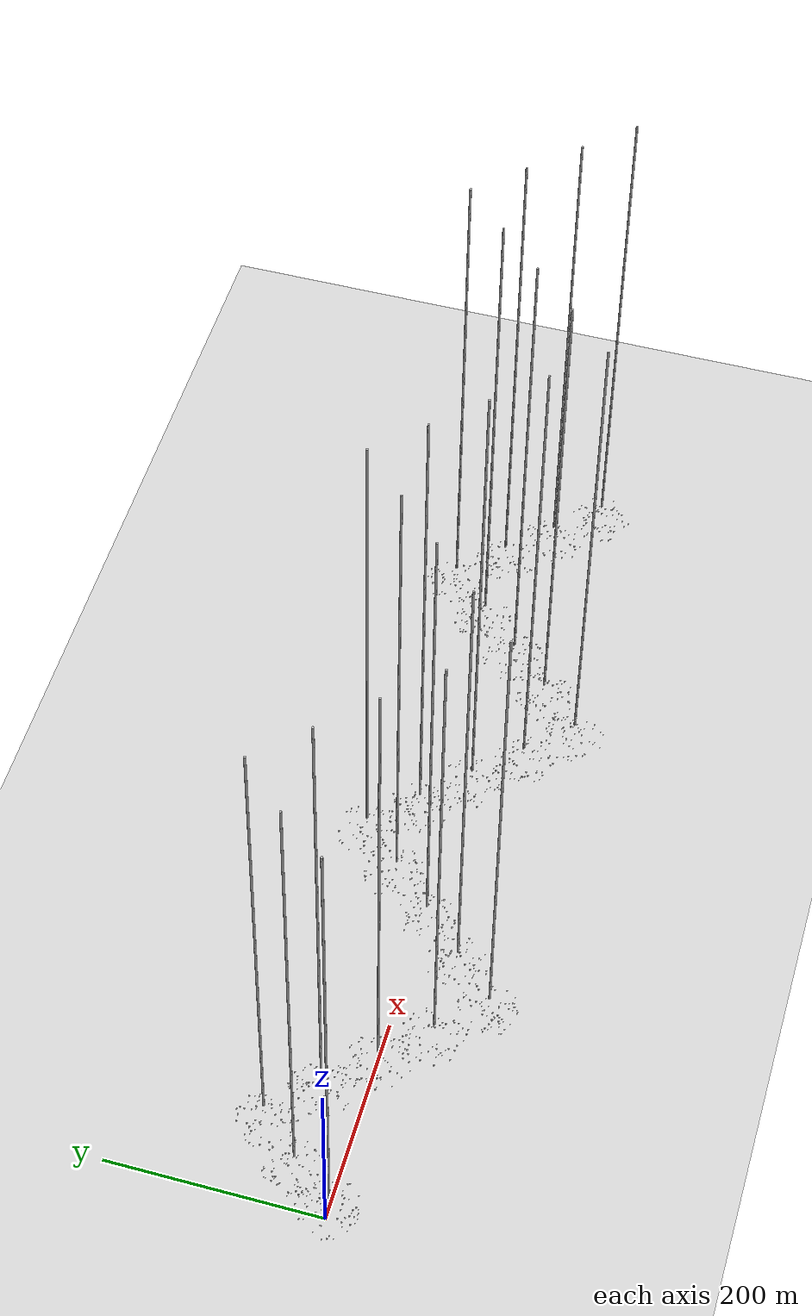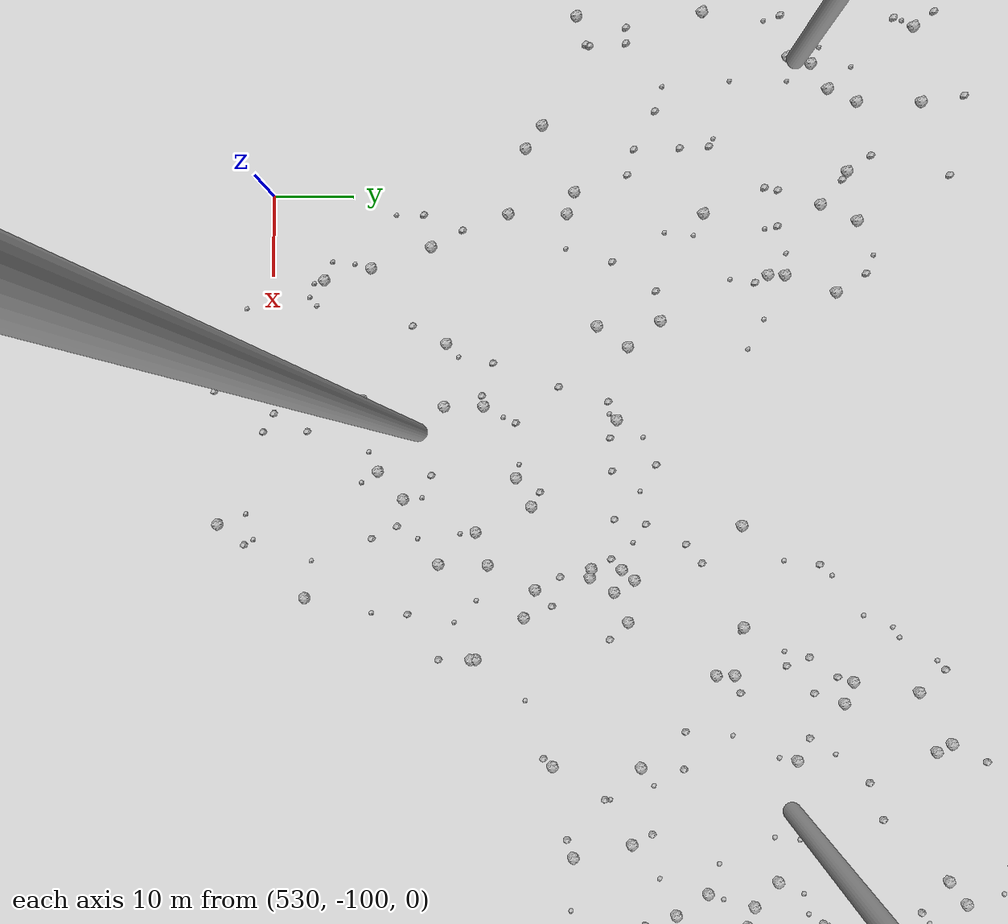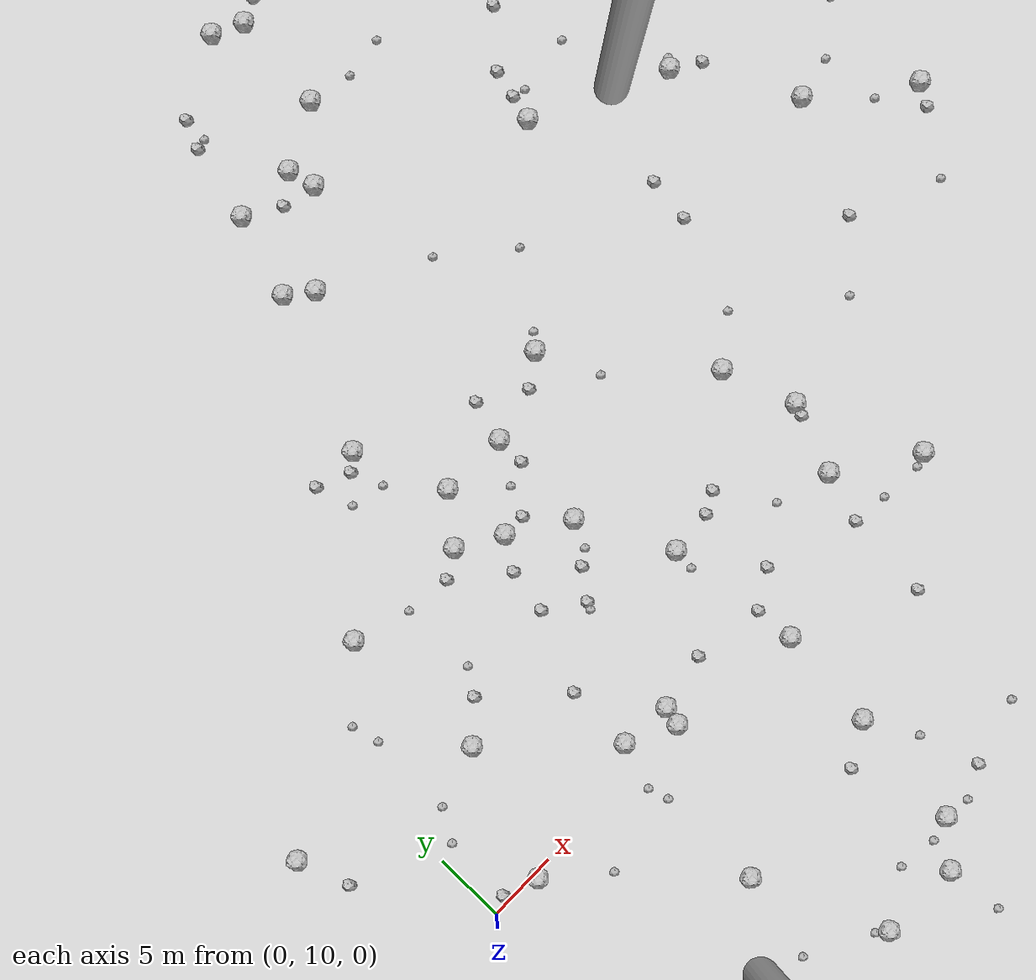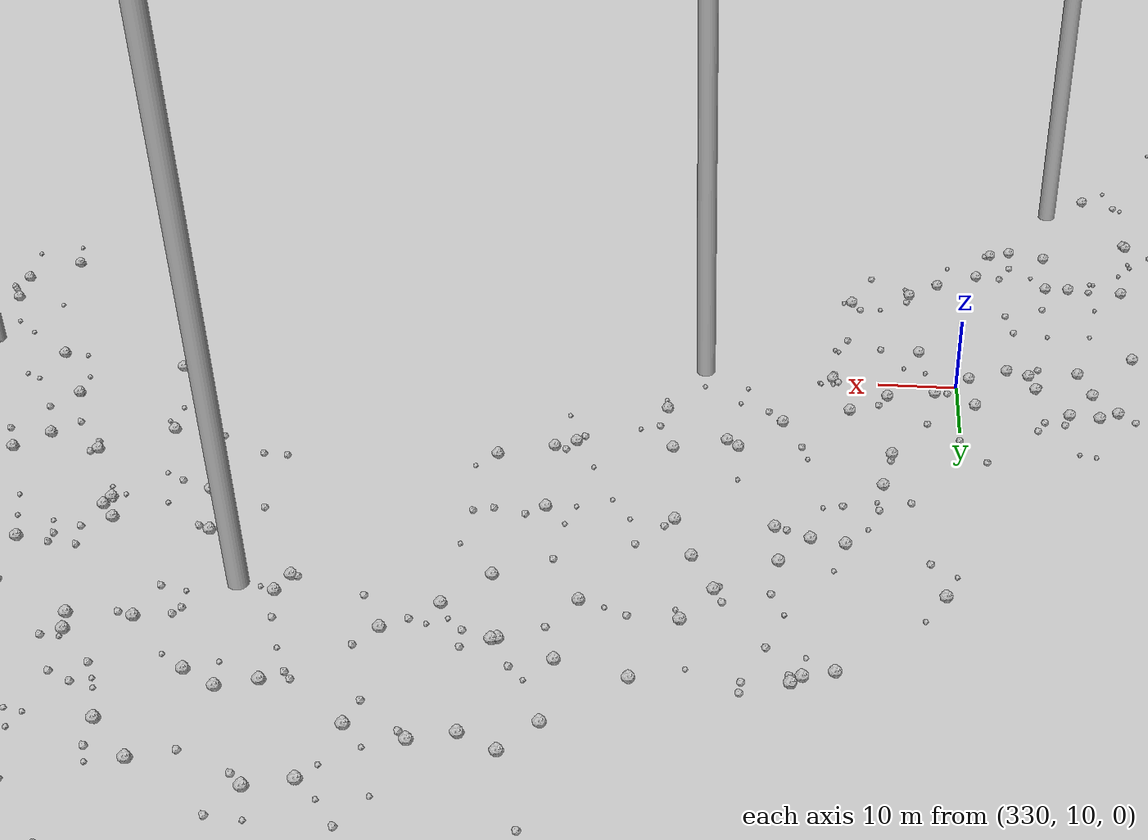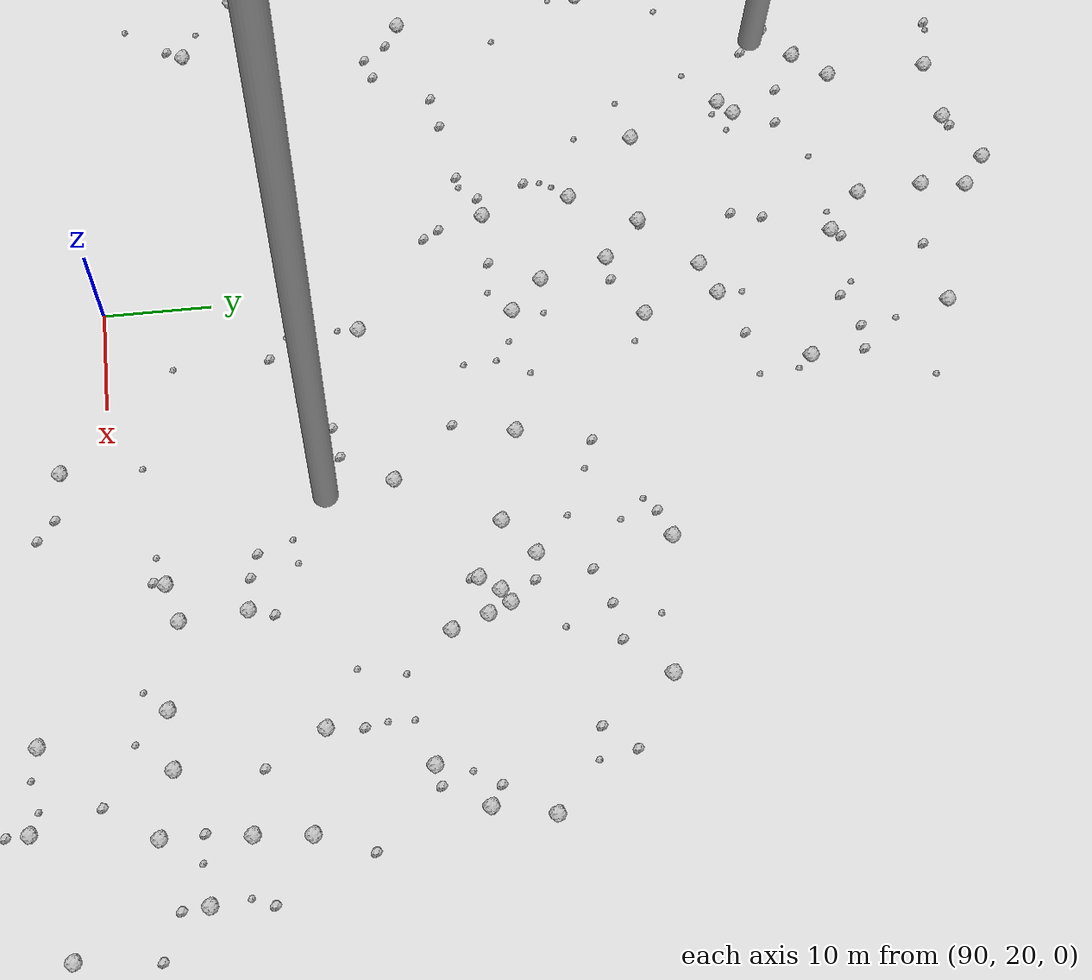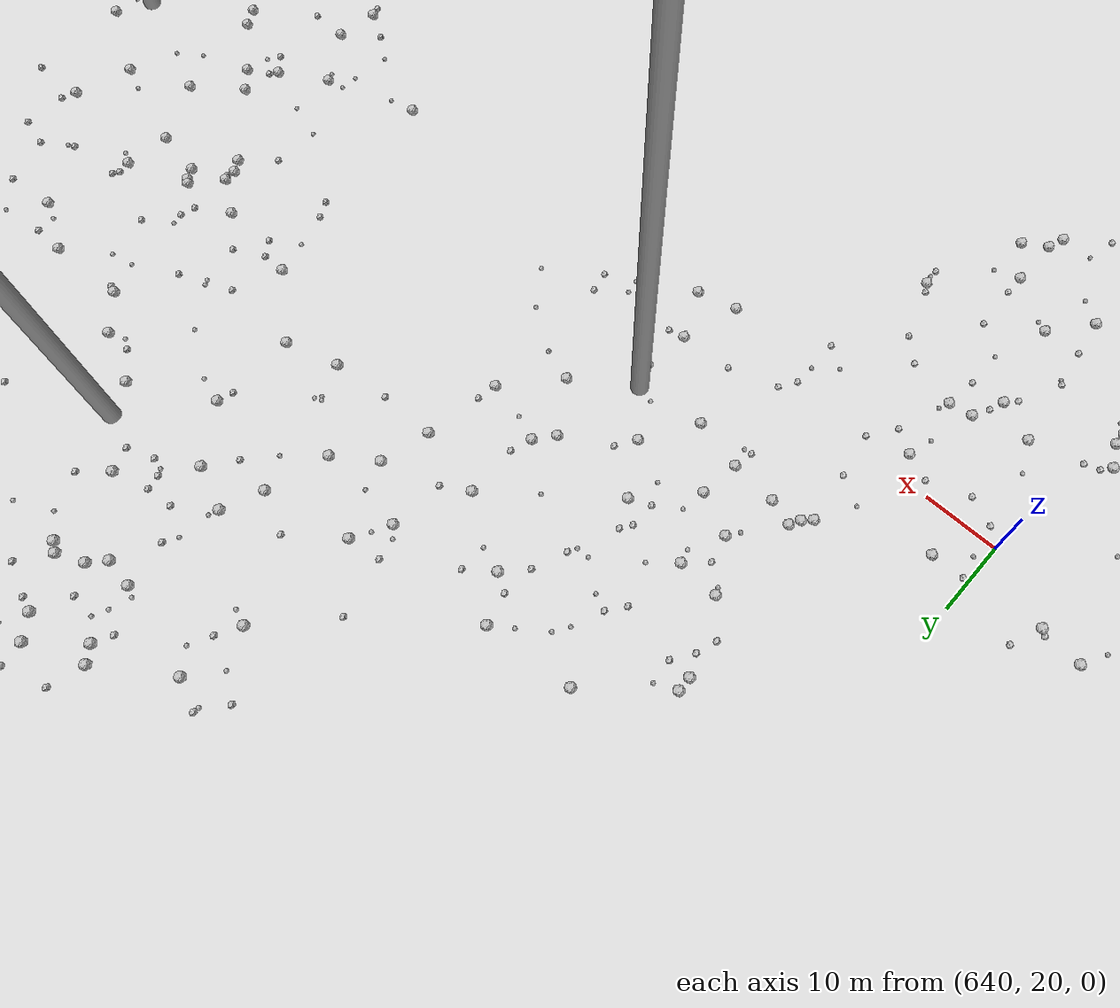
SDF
<sdf version="1.6">
 <world name="default">
  <include><uri>model://custom_ground</uri></include>
  <include><uri>model://sun</uri></include>
  <spherical_coordinates>
   <surface_model>EARTH_WGS84</surface_model>
   <latitude_deg>38.161479</latitude_deg>
   <longitude_deg>-122.454630</longitude_deg>
   <elevation>488.0</elevation>
   <heading_deg>90</heading_deg>
  </spherical_coordinates>
  <model name="rock1_0_0">
   <include><uri>model://rock1</uri><pose>8.014704926354462 -18.49361364034207 0.5 0 0 0</pose></include>
  </model>
  <model name="rock1_0_1">
   <include><uri>model://rock1</uri><pose>25.573061405672973 -6.980809967983461 0.5 0 0 0</pose></include>
  </model>
  <model name="rock1_0_2">
   <include><uri>model://rock1</uri><pose>37.05892887886623 -8.57857589583287 0.5 0 0 0</pose></include>
  </model>
  <model name="rock1_0_3">
   <include><uri>model://rock1</uri><pose>14.447380397119069 -19.399505642528474 0.5 0 0 0</pose></include>
  </model>
  <model name="rock1_0_4">
   <include><uri>model://rock1</uri><pose>17.507150166787127 10.083130815820375 0.5 0 0 0</pose></include>
  </model>
  <model name="rock1_0_5">
   <include><uri>model://rock1</uri><pose>6.905325119836373 18.913771559148323 0.5 0 0 0</pose></include>
  </model>
  <model name="rock1_0_6">
   <include><uri>model://rock1</uri><pose>23.159705777969215 -9.58704639761536 0.5 0 0 0</pose></include>
  </model>
  <model name="rock1_0_7">
   <include><uri>model://rock1</uri><pose>-19.50006351161806 -1.8972151291231683 0.5 0 0 0</pose></include>
  </model>
  <model name="rock1_0_8">
   <include><uri>model://rock1</uri><pose>17.813895654922767 11.406422860787089 0.5 0 0 0</pose></include>
  </model>
  <model name="rock1_0_9">
   <include><uri>model://rock1</uri><pose>0.5192502456148027 -21.61946003745059 0.5 0 0 0</pose></include>
  </model>
  <model name="rock1_0_10">
   <include><uri>model://rock1</uri><pose>2.745626244234355 -9.46299703782589 0.5 0 0 0</pose></include>
  </model>
  <model name="rock1_0_11">
   <include><uri>model://rock1</uri><pose>18.632980836648805 27.21927604334565 0.5 0 0 0</pose></include>
  </model>
  <model name="rock1_0_12">
   <include><uri>model://rock1</uri><pose>26.38935250381023 1.4144262218475596 0.5 0 0 0</pose></include>
  </model>
  <model name="rock1_0_13">
   <include><uri>model://rock1</uri><pose>28.897749746792393 -20.71360675136828 0.5 0 0 0</pose></include>
  </model>
  <model name="rock1_0_14">
   <include><uri>model://rock1</uri><pose>3.7014788950971607 9.723189109151342 0.5 0 0 0</pose></include>
  </model>
  <model name="rock1_0_15">
   <include><uri>model://rock1</uri><pose>17.43358810798727 -9.358902019188484 0.5 0 0 0</pose></include>
  </model>
  <model name="rock1_0_16">
   <include><uri>model://rock1</uri><pose>-6.60727233602568 22.009721791537636 0.5 0 0 0</pose></include>
  </model>
  <model name="rock1_0_17">
   <include><uri>model://rock1</uri><pose>-17.797919921751703 -6.024557068145057 0.5 0 0 0</pose></include>
  </model>
  <model name="rock1_0_18">
   <include><uri>model://rock1</uri><pose>15.584479629937796 29.050384454229686 0.5 0 0 0</pose></include>
  </model>
  <model name="rock1_0_19">
   <include><uri>model://rock1</uri><pose>25.901384876871496 18.183010731451347 0.5 0 0 0</pose></include>
  </model>
  <model name="rock1_0_20">
   <include><uri>model://rock1</uri><pose>27.01945758188611 8.652305441681001 0.5 0 0 0</pose></include>
  </model>
  <model name="rock1_0_21">
   <include><uri>model://rock1</uri><pose>0.4313742360857482 -13.568947367759126 0.5 0 0 0</pose></include>
  </model>
  <model name="rock1_0_22">
   <include><uri>model://rock1</uri><pose>6.426039027255786 29.51596994248677 0.5 0 0 0</pose></include>
  </model>
  <model name="rock1_0_23">
   <include><uri>model://rock1</uri><pose>13.568272839234723 -0.3965600072551716 0.5 0 0 0</pose></include>
  </model>
  <model name="rock1_0_24">
   <include><uri>model://rock1</uri><pose>11.709690238882342 -9.42730344883794 0.5 0 0 0</pose></include>
  </model>
  <model name="rock1_0_25">
   <include><uri>model://rock1</uri><pose>14.149274765556385 11.738043072748539 0.5 0 0 0</pose></include>
  </model>
  <model name="rock1_0_26">
   <include><uri>model://rock1</uri><pose>17.533495181565385 -21.900562409363282 0.5 0 0 0</pose></include>
  </model>
  <model name="rock2_0_0">
   <include><uri>model://rock2</uri><pose>17.19937635421008 25.050068668480158 0.3 0 0 0</pose></include>
  </model>
  <model name="rock2_0_1">
   <include><uri>model://rock2</uri><pose>-7.120115281056501 2.5367088496326815 0.3 0 0 0</pose></include>
  </model>
  <model name="rock2_0_2">
   <include><uri>model://rock2</uri><pose>-6.165717397587546 -21.011113587989858 0.3 0 0 0</pose></include>
  </model>
  <model name="rock2_0_3">
   <include><uri>model://rock2</uri><pose>13.677902977760269 27.925249224654962 0.3 0 0 0</pose></include>
  </model>
  <model name="rock2_0_4">
   <include><uri>model://rock2</uri><pose>11.37713108671744 -24.966520231783253 0.3 0 0 0</pose></include>
  </model>
  <model name="rock2_0_5">
   <include><uri>model://rock2</uri><pose>7.514766203739217 -25.891973493161423 0.3 0 0 0</pose></include>
  </model>
  <model name="rock2_0_6">
   <include><uri>model://rock2</uri><pose>35.80363520152538 10.823405719210136 0.3 0 0 0</pose></include>
  </model>
  <model name="rock2_0_7">
   <include><uri>model://rock2</uri><pose>12.672210038756987 -25.17892123750584 0.3 0 0 0</pose></include>
  </model>
  <model name="rock2_0_8">
   <include><uri>model://rock2</uri><pose>35.33024511589522 4.657484730109331 0.3 0 0 0</pose></include>
  </model>
  <model name="rock2_0_9">
   <include><uri>model://rock2</uri><pose>9.329796938099058 21.118287279019604 0.3 0 0 0</pose></include>
  </model>
  <model name="rock2_0_10">
   <include><uri>model://rock2</uri><pose>30.572122042076934 19.207183093456244 0.3 0 0 0</pose></include>
  </model>
  <model name="rock2_0_11">
   <include><uri>model://rock2</uri><pose>29.63920740459602 -6.1987073161828405 0.3 0 0 0</pose></include>
  </model>
  <model name="rock2_0_12">
   <include><uri>model://rock2</uri><pose>-16.36614117996037 -11.485509086337501 0.3 0 0 0</pose></include>
  </model>
  <model name="rock2_0_13">
   <include><uri>model://rock2</uri><pose>-5.4004712292958 18.391953693323913 0.3 0 0 0</pose></include>
  </model>
  <model name="rock2_0_14">
   <include><uri>model://rock2</uri><pose>1.2388601760272806 10.568299231014258 0.3 0 0 0</pose></include>
  </model>
  <model name="rock2_0_15">
   <include><uri>model://rock2</uri><pose>-14.56013971208524 -7.027429546025946 0.3 0 0 0</pose></include>
  </model>
  <model name="rock2_0_16">
   <include><uri>model://rock2</uri><pose>38.06900000231073 -10.370579649031658 0.3 0 0 0</pose></include>
  </model>
  <model name="rock2_0_17">
   <include><uri>model://rock2</uri><pose>8.130019056521093 -22.423411336874892 0.3 0 0 0</pose></include>
  </model>
  <model name="rock2_0_18">
   <include><uri>model://rock2</uri><pose>21.7767510680126 12.176109174552074 0.3 0 0 0</pose></include>
  </model>
  <model name="rock2_0_19">
   <include><uri>model://rock2</uri><pose>16.085218949651562 -23.92641997834166 0.3 0 0 0</pose></include>
  </model>
  <model name="rock2_0_20">
   <include><uri>model://rock2</uri><pose>29.356026811969677 12.988418405405483 0.3 0 0 0</pose></include>
  </model>
  <model name="rock2_0_21">
   <include><uri>model://rock2</uri><pose>11.305285018403243 -19.4802886723127 0.3 0 0 0</pose></include>
  </model>
  <model name="rock2_0_22">
   <include><uri>model://rock2</uri><pose>14.205905825606564 16.505232605276717 0.3 0 0 0</pose></include>
  </model>
  <model name="rock2_0_23">
   <include><uri>model://rock2</uri><pose>26.806089125259696 11.40528910510011 0.3 0 0 0</pose></include>
  </model>
  <model name="rock2_0_24">
   <include><uri>model://rock2</uri><pose>23.476633749094233 -0.30030359305104426 0.3 0 0 0</pose></include>
  </model>
  <model name="rock2_0_25">
   <include><uri>model://rock2</uri><pose>20.323890885120882 27.235126272928923 0.3 0 0 0</pose></include>
  </model>
  <model name="rock2_0_26">
   <include><uri>model://rock2</uri><pose>5.959665036185779 -14.626095761158977 0.3 0 0 0</pose></include>
  </model>
  <model name="rock3_0_0">
   <include><uri>model://rock3</uri><pose>8.791100230101932 -22.154486247381776 0.2 0 0 0</pose></include>
  </model>
  <model name="rock3_0_1">
   <include><uri>model://rock3</uri><pose>2.668142415005523 23.60032719774955 0.2 0 0 0</pose></include>
  </model>
  <model name="rock3_0_2">
   <include><uri>model://rock3</uri><pose>-7.056119422033969 3.1629047723635466 0.2 0 0 0</pose></include>
  </model>
  <model name="rock3_0_3">
   <include><uri>model://rock3</uri><pose>-14.620246140299628 7.042097807542277 0.2 0 0 0</pose></include>
  </model>
  <model name="rock3_0_4">
   <include><uri>model://rock3</uri><pose>27.382378661929636 -7.355304517494432 0.2 0 0 0</pose></include>
  </model>
  <model name="rock3_0_5">
   <include><uri>model://rock3</uri><pose>-7.352971242310231 1.866388104033092 0.2 0 0 0</pose></include>
  </model>
  <model name="rock3_0_6">
   <include><uri>model://rock3</uri><pose>13.463097715966214 7.038137976472477 0.2 0 0 0</pose></include>
  </model>
  <model name="rock3_0_7">
   <include><uri>model://rock3</uri><pose>16.67973032281713 -8.922693565727219 0.2 0 0 0</pose></include>
  </model>
  <model name="rock3_0_8">
   <include><uri>model://rock3</uri><pose>5.032646201042404 -24.898793162432614 0.2 0 0 0</pose></include>
  </model>
  <model name="rock3_0_9">
   <include><uri>model://rock3</uri><pose>1.3014752115080697 15.35972880508303 0.2 0 0 0</pose></include>
  </model>
  <model name="rock3_0_10">
   <include><uri>model://rock3</uri><pose>7.480657181084268 6.296440512668546 0.2 0 0 0</pose></include>
  </model>
  <model name="rock3_0_11">
   <include><uri>model://rock3</uri><pose>2.1855023514327527 25.54983475124822 0.2 0 0 0</pose></include>
  </model>
  <model name="rock3_0_12">
   <include><uri>model://rock3</uri><pose>10.379776752702863 28.2378352636753 0.2 0 0 0</pose></include>
  </model>
  <model name="rock3_0_13">
   <include><uri>model://rock3</uri><pose>21.705543321365077 22.676954771316232 0.2 0 0 0</pose></include>
  </model>
  <model name="rock3_0_14">
   <include><uri>model://rock3</uri><pose>3.205026969718908 -25.016260413691178 0.2 0 0 0</pose></include>
  </model>
  <model name="rock3_0_15">
   <include><uri>model://rock3</uri><pose>23.816531726732833 -7.5775715743579966 0.2 0 0 0</pose></include>
  </model>
  <model name="rock3_0_16">
   <include><uri>model://rock3</uri><pose>-3.3244477387634888 -15.196098522809436 0.2 0 0 0</pose></include>
  </model>
  <model name="rock3_0_17">
   <include><uri>model://rock3</uri><pose>5.175513812477657 -15.841214476488476 0.2 0 0 0</pose></include>
  </model>
  <model name="rock3_0_18">
   <include><uri>model://rock3</uri><pose>10.47943930859287 22.814414748669364 0.2 0 0 0</pose></include>
  </model>
  <model name="rock3_0_19">
   <include><uri>model://rock3</uri><pose>21.054541639743412 -7.195365635868967 0.2 0 0 0</pose></include>
  </model>
  <model name="rock3_0_20">
   <include><uri>model://rock3</uri><pose>34.32045785072387 -4.960676566193349 0.2 0 0 0</pose></include>
  </model>
  <model name="rock3_0_21">
   <include><uri>model://rock3</uri><pose>-4.393898516725237 -17.51198933155534 0.2 0 0 0</pose></include>
  </model>
  <model name="rock3_0_22">
   <include><uri>model://rock3</uri><pose>13.036815018729264 8.461272479390068 0.2 0 0 0</pose></include>
  </model>
  <model name="rock3_0_23">
   <include><uri>model://rock3</uri><pose>12.181836396395596 -6.535203650115918 0.2 0 0 0</pose></include>
  </model>
  <model name="rock3_0_24">
   <include><uri>model://rock3</uri><pose>23.535263157599204 -13.702619473073355 0.2 0 0 0</pose></include>
  </model>
  <model name="rock3_0_25">
   <include><uri>model://rock3</uri><pose>2.57321137880513 17.50954814858453 0.2 0 0 0</pose></include>
  </model>
  <model name="rock3_0_26">
   <include><uri>model://rock3</uri><pose>28.280515592593886 -2.1662832001877703 0.2 0 0 0</pose></include>
  </model>
  <model name="rock1_1_0">
   <include><uri>model://rock1</uri><pose>29.441665862755 65.91773973192386 0.5 0 0 0</pose></include>
  </model>
  <model name="rock1_1_1">
   <include><uri>model://rock1</uri><pose>38.81895910576447 19.274151701600317 0.5 0 0 0</pose></include>
  </model>
  <model name="rock1_1_2">
   <include><uri>model://rock1</uri><pose>26.776797111346994 53.34210779051029 0.5 0 0 0</pose></include>
  </model>
  <model name="rock1_1_3">
   <include><uri>model://rock1</uri><pose>53.09007582454541 63.87624437924256 0.5 0 0 0</pose></include>
  </model>
  <model name="rock1_1_4">
   <include><uri>model://rock1</uri><pose>37.01565557194717 24.444924166747413 0.5 0 0 0</pose></include>
  </model>
  <model name="rock1_1_5">
   <include><uri>model://rock1</uri><pose>51.339965207839455 48.686395108314095 0.5 0 0 0</pose></include>
  </model>
  <model name="rock1_1_6">
   <include><uri>model://rock1</uri><pose>15.51696388367213 38.55860390205946 0.5 0 0 0</pose></include>
  </model>
  <model name="rock1_1_7">
   <include><uri>model://rock1</uri><pose>42.41715512465029 10.76104230057805 0.5 0 0 0</pose></include>
  </model>
  <model name="rock1_1_8">
   <include><uri>model://rock1</uri><pose>48.46837151509187 53.55989873890649 0.5 0 0 0</pose></include>
  </model>
  <model name="rock1_1_9">
   <include><uri>model://rock1</uri><pose>40.359600756928764 46.040714234981245 0.5 0 0 0</pose></include>
  </model>
  <model name="rock1_1_10">
   <include><uri>model://rock1</uri><pose>26.296183089422467 55.317438544234335 0.5 0 0 0</pose></include>
  </model>
  <model name="rock1_1_11">
   <include><uri>model://rock1</uri><pose>23.001516426857677 31.972652623308665 0.5 0 0 0</pose></include>
  </model>
  <model name="rock1_1_12">
   <include><uri>model://rock1</uri><pose>21.637528184849927 48.118419559110734 0.5 0 0 0</pose></include>
  </model>
  <model name="rock1_1_13">
   <include><uri>model://rock1</uri><pose>61.11648169189103 28.466695288030355 0.5 0 0 0</pose></include>
  </model>
  <model name="rock1_1_14">
   <include><uri>model://rock1</uri><pose>22.637223731712776 24.612063749598548 0.5 0 0 0</pose></include>
  </model>
  <model name="rock1_1_15">
   <include><uri>model://rock1</uri><pose>30.84136303279706 57.68003520008838 0.5 0 0 0</pose></include>
  </model>
  <model name="rock1_1_16">
   <include><uri>model://rock1</uri><pose>21.76147402497957 55.3716181026532 0.5 0 0 0</pose></include>
  </model>
  <model name="rock1_1_17">
   <include><uri>model://rock1</uri><pose>18.169538106196754 32.13263716118551 0.5 0 0 0</pose></include>
  </model>
  <model name="rock1_1_18">
   <include><uri>model://rock1</uri><pose>50.276505371861745 65.96411549905439 0.5 0 0 0</pose></include>
  </model>
  <model name="rock1_1_19">
   <include><uri>model://rock1</uri><pose>19.850915802166966 49.51036639559924 0.5 0 0 0</pose></include>
  </model>
  <model name="rock1_1_20">
   <include><uri>model://rock1</uri><pose>49.737706067492496 41.51149101615855 0.5 0 0 0</pose></include>
  </model>
  <model name="rock1_1_21">
   <include><uri>model://rock1</uri><pose>29.079271899372102 34.47891762026606 0.5 0 0 0</pose></include>
  </model>
  <model name="rock1_1_22">
   <include><uri>model://rock1</uri><pose>59.30055630813426 50.21199599624508 0.5 0 0 0</pose></include>
  </model>
  <model name="rock1_1_23">
   <include><uri>model://rock1</uri><pose>54.629110521511336 33.56751436283191 0.5 0 0 0</pose></include>
  </model>
  <model name="rock1_1_24">
   <include><uri>model://rock1</uri><pose>50.826145043143384 51.54081457478351 0.5 0 0 0</pose></include>
  </model>
  <model name="rock1_1_25">
   <include><uri>model://rock1</uri><pose>31.582208163890453 64.87771859632505 0.5 0 0 0</pose></include>
  </model>
  <model name="rock1_1_26">
   <include><uri>model://rock1</uri><pose>36.93022885709901 14.405727004979958 0.5 0 0 0</pose></include>
  </model>
  <model name="rock2_1_0">
   <include><uri>model://rock2</uri><pose>14.358695004981906 37.68098940392093 0.3 0 0 0</pose></include>
  </model>
  <model name="rock2_1_1">
   <include><uri>model://rock2</uri><pose>63.15983557980182 46.63013771294479 0.3 0 0 0</pose></include>
  </model>
  <model name="rock2_1_2">
   <include><uri>model://rock2</uri><pose>38.5085104300136 18.413735748210623 0.3 0 0 0</pose></include>
  </model>
  <model name="rock2_1_3">
   <include><uri>model://rock2</uri><pose>40.803339305126684 47.93227349947454 0.3 0 0 0</pose></include>
  </model>
  <model name="rock2_1_4">
   <include><uri>model://rock2</uri><pose>33.24764360947677 65.78233802226796 0.3 0 0 0</pose></include>
  </model>
  <model name="rock2_1_5">
   <include><uri>model://rock2</uri><pose>23.728881350850926 34.93905999594395 0.3 0 0 0</pose></include>
  </model>
  <model name="rock2_1_6">
   <include><uri>model://rock2</uri><pose>24.269237707626175 53.886288228847896 0.3 0 0 0</pose></include>
  </model>
  <model name="rock2_1_7">
   <include><uri>model://rock2</uri><pose>23.88504975788141 62.942290002325095 0.3 0 0 0</pose></include>
  </model>
  <model name="rock2_1_8">
   <include><uri>model://rock2</uri><pose>41.30976745850893 49.94795052006622 0.3 0 0 0</pose></include>
  </model>
  <model name="rock2_1_9">
   <include><uri>model://rock2</uri><pose>42.81544119885167 33.5676131693544 0.3 0 0 0</pose></include>
  </model>
  <model name="rock2_1_10">
   <include><uri>model://rock2</uri><pose>61.33454638422206 37.12463757612781 0.3 0 0 0</pose></include>
  </model>
  <model name="rock2_1_11">
   <include><uri>model://rock2</uri><pose>51.67648374237163 40.23533881259365 0.3 0 0 0</pose></include>
  </model>
  <model name="rock2_1_12">
   <include><uri>model://rock2</uri><pose>29.07818308177283 18.425816405737777 0.3 0 0 0</pose></include>
  </model>
  <model name="rock2_1_13">
   <include><uri>model://rock2</uri><pose>44.4829940478662 53.39948303239795 0.3 0 0 0</pose></include>
  </model>
  <model name="rock2_1_14">
   <include><uri>model://rock2</uri><pose>16.63869545723989 21.92136170432429 0.3 0 0 0</pose></include>
  </model>
  <model name="rock2_1_15">
   <include><uri>model://rock2</uri><pose>22.996163740294293 60.943813741210576 0.3 0 0 0</pose></include>
  </model>
  <model name="rock2_1_16">
   <include><uri>model://rock2</uri><pose>12.006456644757826 38.65606324512933 0.3 0 0 0</pose></include>
  </model>
  <model name="rock2_1_17">
   <include><uri>model://rock2</uri><pose>20.685831822303154 22.006182921162036 0.3 0 0 0</pose></include>
  </model>
  <model name="rock2_1_18">
   <include><uri>model://rock2</uri><pose>61.608398231476045 48.85115012541733 0.3 0 0 0</pose></include>
  </model>
  <model name="rock2_1_19">
   <include><uri>model://rock2</uri><pose>19.225739636825068 20.084343995615342 0.3 0 0 0</pose></include>
  </model>
  <model name="rock2_1_20">
   <include><uri>model://rock2</uri><pose>65.34847542935213 47.28956388245529 0.3 0 0 0</pose></include>
  </model>
  <model name="rock2_1_21">
   <include><uri>model://rock2</uri><pose>50.872865723081304 25.536946784776067 0.3 0 0 0</pose></include>
  </model>
  <model name="rock2_1_22">
   <include><uri>model://rock2</uri><pose>43.236146872480546 36.785630448572135 0.3 0 0 0</pose></include>
  </model>
  <model name="rock2_1_23">
   <include><uri>model://rock2</uri><pose>60.202638176644555 26.923650987816586 0.3 0 0 0</pose></include>
  </model>
  <model name="rock2_1_24">
   <include><uri>model://rock2</uri><pose>67.35311048197356 36.626914728288526 0.3 0 0 0</pose></include>
  </model>
  <model name="rock2_1_25">
   <include><uri>model://rock2</uri><pose>22.94093339903248 29.88265198159005 0.3 0 0 0</pose></include>
  </model>
  <model name="rock2_1_26">
   <include><uri>model://rock2</uri><pose>26.899980529938865 32.9711276780089 0.3 0 0 0</pose></include>
  </model>
  <model name="rock3_1_0">
   <include><uri>model://rock3</uri><pose>40.23552884370466 26.91169028122762 0.2 0 0 0</pose></include>
  </model>
  <model name="rock3_1_1">
   <include><uri>model://rock3</uri><pose>18.960517704419665 19.531017610005556 0.2 0 0 0</pose></include>
  </model>
  <model name="rock3_1_2">
   <include><uri>model://rock3</uri><pose>41.70301056597182 60.607785497564336 0.2 0 0 0</pose></include>
  </model>
  <model name="rock3_1_3">
   <include><uri>model://rock3</uri><pose>33.49150389309483 40.200708320079116 0.2 0 0 0</pose></include>
  </model>
  <model name="rock3_1_4">
   <include><uri>model://rock3</uri><pose>28.87076994204928 44.03232392940686 0.2 0 0 0</pose></include>
  </model>
  <model name="rock3_1_5">
   <include><uri>model://rock3</uri><pose>29.94566335672118 35.480078836135874 0.2 0 0 0</pose></include>
  </model>
  <model name="rock3_1_6">
   <include><uri>model://rock3</uri><pose>61.98508428791948 59.55944225849306 0.2 0 0 0</pose></include>
  </model>
  <model name="rock3_1_7">
   <include><uri>model://rock3</uri><pose>46.02557965899857 48.269685088262314 0.2 0 0 0</pose></include>
  </model>
  <model name="rock3_1_8">
   <include><uri>model://rock3</uri><pose>32.99106273983093 15.482707221209244 0.2 0 0 0</pose></include>
  </model>
  <model name="rock3_1_9">
   <include><uri>model://rock3</uri><pose>21.241514666004235 29.215028744156523 0.2 0 0 0</pose></include>
  </model>
  <model name="rock3_1_10">
   <include><uri>model://rock3</uri><pose>58.13216098209897 29.881139618960802 0.2 0 0 0</pose></include>
  </model>
  <model name="rock3_1_11">
   <include><uri>model://rock3</uri><pose>37.08621530860201 57.47528768154238 0.2 0 0 0</pose></include>
  </model>
  <model name="rock3_1_12">
   <include><uri>model://rock3</uri><pose>12.808122526097637 35.970291834360616 0.2 0 0 0</pose></include>
  </model>
  <model name="rock3_1_13">
   <include><uri>model://rock3</uri><pose>48.95493297786942 44.35936907006174 0.2 0 0 0</pose></include>
  </model>
  <model name="rock3_1_14">
   <include><uri>model://rock3</uri><pose>23.762535942333816 61.07398112990523 0.2 0 0 0</pose></include>
  </model>
  <model name="rock3_1_15">
   <include><uri>model://rock3</uri><pose>57.79640017471129 34.22484146043078 0.2 0 0 0</pose></include>
  </model>
  <model name="rock3_1_16">
   <include><uri>model://rock3</uri><pose>30.988921721991044 30.0914596936899 0.2 0 0 0</pose></include>
  </model>
  <model name="rock3_1_17">
   <include><uri>model://rock3</uri><pose>25.730738285226394 16.573952693433434 0.2 0 0 0</pose></include>
  </model>
  <model name="rock3_1_18">
   <include><uri>model://rock3</uri><pose>50.25749356141104 42.12192349547563 0.2 0 0 0</pose></include>
  </model>
  <model name="rock3_1_19">
   <include><uri>model://rock3</uri><pose>15.228726175552374 35.45543684833552 0.2 0 0 0</pose></include>
  </model>
  <model name="rock3_1_20">
   <include><uri>model://rock3</uri><pose>38.35213976692591 10.505163129541932 0.2 0 0 0</pose></include>
  </model>
  <model name="rock3_1_21">
   <include><uri>model://rock3</uri><pose>40.0667115733322 59.538091162684964 0.2 0 0 0</pose></include>
  </model>
  <model name="rock3_1_22">
   <include><uri>model://rock3</uri><pose>46.816567428992215 21.65827932357581 0.2 0 0 0</pose></include>
  </model>
  <model name="rock3_1_23">
   <include><uri>model://rock3</uri><pose>41.411140890093634 10.30762085440969 0.2 0 0 0</pose></include>
  </model>
  <model name="rock3_1_24">
   <include><uri>model://rock3</uri><pose>33.99197750179056 57.03768371038222 0.2 0 0 0</pose></include>
  </model>
  <model name="rock3_1_25">
   <include><uri>model://rock3</uri><pose>57.1619074097638 22.75743857890852 0.2 0 0 0</pose></include>
  </model>
  <model name="rock3_1_26">
   <include><uri>model://rock3</uri><pose>41.71950124696369 47.671165404954166 0.2 0 0 0</pose></include>
  </model>
  <model name="rock1_2_0">
   <include><uri>model://rock1</uri><pose>63.4974343772334 86.63135502534352 0.5 0 0 0</pose></include>
  </model>
  <model name="rock1_2_1">
   <include><uri>model://rock1</uri><pose>90.40798931634257 61.156282965527 0.5 0 0 0</pose></include>
  </model>
  <model name="rock1_2_2">
   <include><uri>model://rock1</uri><pose>90.19533795250476 76.3251236366221 0.5 0 0 0</pose></include>
  </model>
  <model name="rock1_2_3">
   <include><uri>model://rock1</uri><pose>75.24483026362705 71.85782999911869 0.5 0 0 0</pose></include>
  </model>
  <model name="rock1_2_4">
   <include><uri>model://rock1</uri><pose>57.44683288814598 68.58481040092227 0.5 0 0 0</pose></include>
  </model>
  <model name="rock1_2_5">
   <include><uri>model://rock1</uri><pose>96.41195059105182 99.02895715392035 0.5 0 0 0</pose></include>
  </model>
  <model name="rock1_2_6">
   <include><uri>model://rock1</uri><pose>81.4762052168345 64.92705938853463 0.5 0 0 0</pose></include>
  </model>
  <model name="rock1_2_7">
   <include><uri>model://rock1</uri><pose>80.83175945395095 105.71135369061355 0.5 0 0 0</pose></include>
  </model>
  <model name="rock1_2_8">
   <include><uri>model://rock1</uri><pose>51.926275758790176 84.81951233667135 0.5 0 0 0</pose></include>
  </model>
  <model name="rock1_2_9">
   <include><uri>model://rock1</uri><pose>88.6613589527226 67.623975814845 0.5 0 0 0</pose></include>
  </model>
  <model name="rock1_2_10">
   <include><uri>model://rock1</uri><pose>73.30423662495865 82.34437844274188 0.5 0 0 0</pose></include>
  </model>
  <model name="rock1_2_11">
   <include><uri>model://rock1</uri><pose>52.580197651179795 75.29866591688923 0.5 0 0 0</pose></include>
  </model>
  <model name="rock1_2_12">
   <include><uri>model://rock1</uri><pose>93.50754433376616 77.59735301506743 0.5 0 0 0</pose></include>
  </model>
  <model name="rock1_2_13">
   <include><uri>model://rock1</uri><pose>95.08402276698888 70.42527412105076 0.5 0 0 0</pose></include>
  </model>
  <model name="rock1_2_14">
   <include><uri>model://rock1</uri><pose>69.39046358617666 102.31798143316101 0.5 0 0 0</pose></include>
  </model>
  <model name="rock1_2_15">
   <include><uri>model://rock1</uri><pose>83.91062021065886 103.39368628646324 0.5 0 0 0</pose></include>
  </model>
  <model name="rock1_2_16">
   <include><uri>model://rock1</uri><pose>82.78002056149424 56.39619137809552 0.5 0 0 0</pose></include>
  </model>
  <model name="rock1_2_17">
   <include><uri>model://rock1</uri><pose>84.7660615098734 71.23286800402119 0.5 0 0 0</pose></include>
  </model>
  <model name="rock1_2_18">
   <include><uri>model://rock1</uri><pose>66.98092341465386 89.33574450645969 0.5 0 0 0</pose></include>
  </model>
  <model name="rock1_2_19">
   <include><uri>model://rock1</uri><pose>71.84070023148546 81.00107791996896 0.5 0 0 0</pose></include>
  </model>
  <model name="rock1_2_20">
   <include><uri>model://rock1</uri><pose>69.66002463815326 92.51425617829152 0.5 0 0 0</pose></include>
  </model>
  <model name="rock1_2_21">
   <include><uri>model://rock1</uri><pose>93.54936103431982 58.0808104112933 0.5 0 0 0</pose></include>
  </model>
  <model name="rock1_2_22">
   <include><uri>model://rock1</uri><pose>83.40311308891916 99.13463081466062 0.5 0 0 0</pose></include>
  </model>
  <model name="rock1_2_23">
   <include><uri>model://rock1</uri><pose>83.7657839767911 92.84889707532923 0.5 0 0 0</pose></include>
  </model>
  <model name="rock1_2_24">
   <include><uri>model://rock1</uri><pose>87.71538411702754 89.4592362942515 0.5 0 0 0</pose></include>
  </model>
  <model name="rock1_2_25">
   <include><uri>model://rock1</uri><pose>75.77897951327591 102.83964569401112 0.5 0 0 0</pose></include>
  </model>
  <model name="rock1_2_26">
   <include><uri>model://rock1</uri><pose>101.03333860700378 85.18127010964865 0.5 0 0 0</pose></include>
  </model>
  <model name="rock2_2_0">
   <include><uri>model://rock2</uri><pose>83.88403004705373 52.0885174110775 0.3 0 0 0</pose></include>
  </model>
  <model name="rock2_2_1">
   <include><uri>model://rock2</uri><pose>53.473278948859345 88.40954324788457 0.3 0 0 0</pose></include>
  </model>
  <model name="rock2_2_2">
   <include><uri>model://rock2</uri><pose>71.88085534832702 53.357151867936274 0.3 0 0 0</pose></include>
  </model>
  <model name="rock2_2_3">
   <include><uri>model://rock2</uri><pose>68.54078506561191 52.764082754984436 0.3 0 0 0</pose></include>
  </model>
  <model name="rock2_2_4">
   <include><uri>model://rock2</uri><pose>78.066855920469 54.36340503953144 0.3 0 0 0</pose></include>
  </model>
  <model name="rock2_2_5">
   <include><uri>model://rock2</uri><pose>88.40356358376668 90.39527307635191 0.3 0 0 0</pose></include>
  </model>
  <model name="rock2_2_6">
   <include><uri>model://rock2</uri><pose>84.76258602530592 50.59038056598945 0.3 0 0 0</pose></include>
  </model>
  <model name="rock2_2_7">
   <include><uri>model://rock2</uri><pose>66.30226363258903 89.71744262410832 0.3 0 0 0</pose></include>
  </model>
  <model name="rock2_2_8">
   <include><uri>model://rock2</uri><pose>65.99336210715354 84.29810548264875 0.3 0 0 0</pose></include>
  </model>
  <model name="rock2_2_9">
   <include><uri>model://rock2</uri><pose>100.75593291017208 90.31588771874235 0.3 0 0 0</pose></include>
  </model>
  <model name="rock2_2_10">
   <include><uri>model://rock2</uri><pose>85.5068663884205 83.24757624055577 0.3 0 0 0</pose></include>
  </model>
  <model name="rock2_2_11">
   <include><uri>model://rock2</uri><pose>98.26472871466677 90.45035309789603 0.3 0 0 0</pose></include>
  </model>
  <model name="rock2_2_12">
   <include><uri>model://rock2</uri><pose>76.80170917356776 103.4195494848048 0.3 0 0 0</pose></include>
  </model>
  <model name="rock2_2_13">
   <include><uri>model://rock2</uri><pose>85.18824345257988 71.41596513406446 0.3 0 0 0</pose></include>
  </model>
  <model name="rock2_2_14">
   <include><uri>model://rock2</uri><pose>50.245108826843655 80.55704639799904 0.3 0 0 0</pose></include>
  </model>
  <model name="rock2_2_15">
   <include><uri>model://rock2</uri><pose>79.3944823402071 60.779963765555436 0.3 0 0 0</pose></include>
  </model>
  <model name="rock2_2_16">
   <include><uri>model://rock2</uri><pose>80.67169995067624 56.17829875216471 0.3 0 0 0</pose></include>
  </model>
  <model name="rock2_2_17">
   <include><uri>model://rock2</uri><pose>74.72510955942593 86.38168966464798 0.3 0 0 0</pose></include>
  </model>
  <model name="rock2_2_18">
   <include><uri>model://rock2</uri><pose>64.10621698139599 103.42778128464917 0.3 0 0 0</pose></include>
  </model>
  <model name="rock2_2_19">
   <include><uri>model://rock2</uri><pose>90.03022521956615 98.03877332837672 0.3 0 0 0</pose></include>
  </model>
  <model name="rock2_2_20">
   <include><uri>model://rock2</uri><pose>94.86629582508988 89.10079091122306 0.3 0 0 0</pose></include>
  </model>
  <model name="rock2_2_21">
   <include><uri>model://rock2</uri><pose>58.76506471233404 91.26271480673923 0.3 0 0 0</pose></include>
  </model>
  <model name="rock2_2_22">
   <include><uri>model://rock2</uri><pose>97.9655650207875 79.54626363089639 0.3 0 0 0</pose></include>
  </model>
  <model name="rock2_2_23">
   <include><uri>model://rock2</uri><pose>84.79618709898212 80.27357916917879 0.3 0 0 0</pose></include>
  </model>
  <model name="rock2_2_24">
   <include><uri>model://rock2</uri><pose>88.0560853175063 56.454563088055494 0.3 0 0 0</pose></include>
  </model>
  <model name="rock2_2_25">
   <include><uri>model://rock2</uri><pose>90.97881468673832 67.8004804750207 0.3 0 0 0</pose></include>
  </model>
  <model name="rock2_2_26">
   <include><uri>model://rock2</uri><pose>70.86159972758738 87.03163771246277 0.3 0 0 0</pose></include>
  </model>
  <model name="rock3_2_0">
   <include><uri>model://rock3</uri><pose>79.98593821053717 63.44970159196619 0.2 0 0 0</pose></include>
  </model>
  <model name="rock3_2_1">
   <include><uri>model://rock3</uri><pose>93.42872786464014 79.97958881649879 0.2 0 0 0</pose></include>
  </model>
  <model name="rock3_2_2">
   <include><uri>model://rock3</uri><pose>68.08499507607733 78.0326172547223 0.2 0 0 0</pose></include>
  </model>
  <model name="rock3_2_3">
   <include><uri>model://rock3</uri><pose>102.34772125221457 80.1851915193085 0.2 0 0 0</pose></include>
  </model>
  <model name="rock3_2_4">
   <include><uri>model://rock3</uri><pose>64.90450492291332 103.44634791051868 0.2 0 0 0</pose></include>
  </model>
  <model name="rock3_2_5">
   <include><uri>model://rock3</uri><pose>102.09953169159054 83.89896043620556 0.2 0 0 0</pose></include>
  </model>
  <model name="rock3_2_6">
   <include><uri>model://rock3</uri><pose>73.02551662001426 80.35317100295039 0.2 0 0 0</pose></include>
  </model>
  <model name="rock3_2_7">
   <include><uri>model://rock3</uri><pose>85.44408372445199 89.57352690161413 0.2 0 0 0</pose></include>
  </model>
  <model name="rock3_2_8">
   <include><uri>model://rock3</uri><pose>79.38953861555906 62.35544573882911 0.2 0 0 0</pose></include>
  </model>
  <model name="rock3_2_9">
   <include><uri>model://rock3</uri><pose>74.6253132358408 66.32549079071093 0.2 0 0 0</pose></include>
  </model>
  <model name="rock3_2_10">
   <include><uri>model://rock3</uri><pose>97.73957472763206 69.16767071264968 0.2 0 0 0</pose></include>
  </model>
  <model name="rock3_2_11">
   <include><uri>model://rock3</uri><pose>60.22444973577842 86.74968904376209 0.2 0 0 0</pose></include>
  </model>
  <model name="rock3_2_12">
   <include><uri>model://rock3</uri><pose>55.63507688378679 67.98311258479418 0.2 0 0 0</pose></include>
  </model>
  <model name="rock3_2_13">
   <include><uri>model://rock3</uri><pose>91.19277308319244 56.026999546449645 0.2 0 0 0</pose></include>
  </model>
  <model name="rock3_2_14">
   <include><uri>model://rock3</uri><pose>70.78455564678512 70.94529934264355 0.2 0 0 0</pose></include>
  </model>
  <model name="rock3_2_15">
   <include><uri>model://rock3</uri><pose>93.8821081460581 61.04647453585265 0.2 0 0 0</pose></include>
  </model>
  <model name="rock3_2_16">
   <include><uri>model://rock3</uri><pose>54.51045701447579 64.71418431303731 0.2 0 0 0</pose></include>
  </model>
  <model name="rock3_2_17">
   <include><uri>model://rock3</uri><pose>58.94005857948658 91.38345824318714 0.2 0 0 0</pose></include>
  </model>
  <model name="rock3_2_18">
   <include><uri>model://rock3</uri><pose>79.11972539191972 54.498214577002386 0.2 0 0 0</pose></include>
  </model>
  <model name="rock3_2_19">
   <include><uri>model://rock3</uri><pose>75.02412214535747 81.45220700829327 0.2 0 0 0</pose></include>
  </model>
  <model name="rock3_2_20">
   <include><uri>model://rock3</uri><pose>93.39546348963486 90.40725230297375 0.2 0 0 0</pose></include>
  </model>
  <model name="rock3_2_21">
   <include><uri>model://rock3</uri><pose>78.92830055604047 88.96979726476444 0.2 0 0 0</pose></include>
  </model>
  <model name="rock3_2_22">
   <include><uri>model://rock3</uri><pose>59.84039940497503 76.39951877502713 0.2 0 0 0</pose></include>
  </model>
  <model name="rock3_2_23">
   <include><uri>model://rock3</uri><pose>97.67781725776149 93.86098952851188 0.2 0 0 0</pose></include>
  </model>
  <model name="rock3_2_24">
   <include><uri>model://rock3</uri><pose>103.95052750073991 96.39373974678928 0.2 0 0 0</pose></include>
  </model>
  <model name="rock3_2_25">
   <include><uri>model://rock3</uri><pose>96.63716109609099 57.46487840724145 0.2 0 0 0</pose></include>
  </model>
  <model name="rock3_2_26">
   <include><uri>model://rock3</uri><pose>57.41070130268584 65.84165458552395 0.2 0 0 0</pose></include>
  </model>
  <model name="rock1_3_0">
   <include><uri>model://rock1</uri><pose>106.08114586829535 56.98464480089486 0.5 0 0 0</pose></include>
  </model>
  <model name="rock1_3_1">
   <include><uri>model://rock1</uri><pose>120.08949113692748 52.127745503989175 0.5 0 0 0</pose></include>
  </model>
  <model name="rock1_3_2">
   <include><uri>model://rock1</uri><pose>141.54329516882814 36.18956900196942 0.5 0 0 0</pose></include>
  </model>
  <model name="rock1_3_3">
   <include><uri>model://rock1</uri><pose>118.25935647507565 57.47100907526623 0.5 0 0 0</pose></include>
  </model>
  <model name="rock1_3_4">
   <include><uri>model://rock1</uri><pose>136.62732046096895 46.74989484204949 0.5 0 0 0</pose></include>
  </model>
  <model name="rock1_3_5">
   <include><uri>model://rock1</uri><pose>140.6382603467866 23.507059535470717 0.5 0 0 0</pose></include>
  </model>
  <model name="rock1_3_6">
   <include><uri>model://rock1</uri><pose>140.63218602514792 51.04135564100128 0.5 0 0 0</pose></include>
  </model>
  <model name="rock1_3_7">
   <include><uri>model://rock1</uri><pose>117.81360918338302 69.65377478689672 0.5 0 0 0</pose></include>
  </model>
  <model name="rock1_3_8">
   <include><uri>model://rock1</uri><pose>129.5852511224153 24.60099035888417 0.5 0 0 0</pose></include>
  </model>
  <model name="rock1_3_9">
   <include><uri>model://rock1</uri><pose>118.03559642803219 24.787018281230587 0.5 0 0 0</pose></include>
  </model>
  <model name="rock1_3_10">
   <include><uri>model://rock1</uri><pose>109.92025528404707 45.56413784745951 0.5 0 0 0</pose></include>
  </model>
  <model name="rock1_3_11">
   <include><uri>model://rock1</uri><pose>114.8521456427297 54.72725570598123 0.5 0 0 0</pose></include>
  </model>
  <model name="rock1_3_12">
   <include><uri>model://rock1</uri><pose>132.50892237205977 37.84875782788389 0.5 0 0 0</pose></include>
  </model>
  <model name="rock1_3_13">
   <include><uri>model://rock1</uri><pose>106.3483413946154 15.709147228121537 0.5 0 0 0</pose></include>
  </model>
  <model name="rock1_3_14">
   <include><uri>model://rock1</uri><pose>121.42829823886984 53.94584394563163 0.5 0 0 0</pose></include>
  </model>
  <model name="rock1_3_15">
   <include><uri>model://rock1</uri><pose>131.7638167353889 13.536811305982798 0.5 0 0 0</pose></include>
  </model>
  <model name="rock1_3_16">
   <include><uri>model://rock1</uri><pose>123.55086175267428 52.65920997960525 0.5 0 0 0</pose></include>
  </model>
  <model name="rock1_3_17">
   <include><uri>model://rock1</uri><pose>122.68847681526934 54.68826261077284 0.5 0 0 0</pose></include>
  </model>
  <model name="rock1_3_18">
   <include><uri>model://rock1</uri><pose>134.8644080573909 24.875629532051548 0.5 0 0 0</pose></include>
  </model>
  <model name="rock1_3_19">
   <include><uri>model://rock1</uri><pose>121.15498974744223 31.875399663001474 0.5 0 0 0</pose></include>
  </model>
  <model name="rock1_3_20">
   <include><uri>model://rock1</uri><pose>141.0940453947907 31.192518144390444 0.5 0 0 0</pose></include>
  </model>
  <model name="rock1_3_21">
   <include><uri>model://rock1</uri><pose>124.72524499695675 49.31255822236611 0.5 0 0 0</pose></include>
  </model>
  <model name="rock1_3_22">
   <include><uri>model://rock1</uri><pose>130.55188356751927 67.85250227013528 0.5 0 0 0</pose></include>
  </model>
  <model name="rock1_3_23">
   <include><uri>model://rock1</uri><pose>121.60415277694887 25.798868459565952 0.5 0 0 0</pose></include>
  </model>
  <model name="rock1_3_24">
   <include><uri>model://rock1</uri><pose>94.14668857883791 43.55484505371996 0.5 0 0 0</pose></include>
  </model>
  <model name="rock1_3_25">
   <include><uri>model://rock1</uri><pose>146.6036270225566 27.431266872611822 0.5 0 0 0</pose></include>
  </model>
  <model name="rock1_3_26">
   <include><uri>model://rock1</uri><pose>141.81512836366153 56.45885841758823 0.5 0 0 0</pose></include>
  </model>
  <model name="rock2_3_0">
   <include><uri>model://rock2</uri><pose>140.50152808596442 27.280332271832044 0.3 0 0 0</pose></include>
  </model>
  <model name="rock2_3_1">
   <include><uri>model://rock2</uri><pose>117.67251926748456 23.730159154327183 0.3 0 0 0</pose></include>
  </model>
  <model name="rock2_3_2">
   <include><uri>model://rock2</uri><pose>112.69210629448 13.62958314686531 0.3 0 0 0</pose></include>
  </model>
  <model name="rock2_3_3">
   <include><uri>model://rock2</uri><pose>123.57332951504586 63.56584764001885 0.3 0 0 0</pose></include>
  </model>
  <model name="rock2_3_4">
   <include><uri>model://rock2</uri><pose>136.8555049297366 63.931066089332 0.3 0 0 0</pose></include>
  </model>
  <model name="rock2_3_5">
   <include><uri>model://rock2</uri><pose>107.05842317437178 40.93753370665872 0.3 0 0 0</pose></include>
  </model>
  <model name="rock2_3_6">
   <include><uri>model://rock2</uri><pose>120.71983370157363 57.12065585336965 0.3 0 0 0</pose></include>
  </model>
  <model name="rock2_3_7">
   <include><uri>model://rock2</uri><pose>107.6121741037299 63.82626685043425 0.3 0 0 0</pose></include>
  </model>
  <model name="rock2_3_8">
   <include><uri>model://rock2</uri><pose>120.20980946925978 62.26120874513931 0.3 0 0 0</pose></include>
  </model>
  <model name="rock2_3_9">
   <include><uri>model://rock2</uri><pose>115.84945060502315 32.97742434437176 0.3 0 0 0</pose></include>
  </model>
  <model name="rock2_3_10">
   <include><uri>model://rock2</uri><pose>132.72096455897685 41.15336036733877 0.3 0 0 0</pose></include>
  </model>
  <model name="rock2_3_11">
   <include><uri>model://rock2</uri><pose>110.80493256966278 15.221005367665622 0.3 0 0 0</pose></include>
  </model>
  <model name="rock2_3_12">
   <include><uri>model://rock2</uri><pose>118.06918740397447 32.23980935375656 0.3 0 0 0</pose></include>
  </model>
  <model name="rock2_3_13">
   <include><uri>model://rock2</uri><pose>135.4535286063096 32.54033719650539 0.3 0 0 0</pose></include>
  </model>
  <model name="rock2_3_14">
   <include><uri>model://rock2</uri><pose>138.4412867458906 47.14241944178924 0.3 0 0 0</pose></include>
  </model>
  <model name="rock2_3_15">
   <include><uri>model://rock2</uri><pose>127.00656572143885 64.00132251843795 0.3 0 0 0</pose></include>
  </model>
  <model name="rock2_3_16">
   <include><uri>model://rock2</uri><pose>143.4496166787877 41.25516212554649 0.3 0 0 0</pose></include>
  </model>
  <model name="rock2_3_17">
   <include><uri>model://rock2</uri><pose>147.01444563046726 32.7401886343679 0.3 0 0 0</pose></include>
  </model>
  <model name="rock2_3_18">
   <include><uri>model://rock2</uri><pose>120.01883302172837 51.5230405124144 0.3 0 0 0</pose></include>
  </model>
  <model name="rock2_3_19">
   <include><uri>model://rock2</uri><pose>138.8010709329686 52.175783473144755 0.3 0 0 0</pose></include>
  </model>
  <model name="rock2_3_20">
   <include><uri>model://rock2</uri><pose>121.72233702521203 34.184765211103255 0.3 0 0 0</pose></include>
  </model>
  <model name="rock2_3_21">
   <include><uri>model://rock2</uri><pose>115.17821061754655 68.71491346754902 0.3 0 0 0</pose></include>
  </model>
  <model name="rock2_3_22">
   <include><uri>model://rock2</uri><pose>96.37056142863322 35.176888104271974 0.3 0 0 0</pose></include>
  </model>
  <model name="rock2_3_23">
   <include><uri>model://rock2</uri><pose>104.85875482935592 51.32308972628762 0.3 0 0 0</pose></include>
  </model>
  <model name="rock2_3_24">
   <include><uri>model://rock2</uri><pose>104.08718519791223 40.44785610220406 0.3 0 0 0</pose></include>
  </model>
  <model name="rock2_3_25">
   <include><uri>model://rock2</uri><pose>99.55800097166917 39.022255958886745 0.3 0 0 0</pose></include>
  </model>
  <model name="rock2_3_26">
   <include><uri>model://rock2</uri><pose>134.5662160875068 61.15477449357898 0.3 0 0 0</pose></include>
  </model>
  <model name="rock3_3_0">
   <include><uri>model://rock3</uri><pose>124.86710024368689 67.66319763063026 0.2 0 0 0</pose></include>
  </model>
  <model name="rock3_3_1">
   <include><uri>model://rock3</uri><pose>146.21774021234313 30.779763618879553 0.2 0 0 0</pose></include>
  </model>
  <model name="rock3_3_2">
   <include><uri>model://rock3</uri><pose>98.53161407375373 56.073365033488095 0.2 0 0 0</pose></include>
  </model>
  <model name="rock3_3_3">
   <include><uri>model://rock3</uri><pose>132.25539190028002 21.711631319400713 0.2 0 0 0</pose></include>
  </model>
  <model name="rock3_3_4">
   <include><uri>model://rock3</uri><pose>100.11080240492748 59.08313305177704 0.2 0 0 0</pose></include>
  </model>
  <model name="rock3_3_5">
   <include><uri>model://rock3</uri><pose>127.37537984483063 40.86756688550864 0.2 0 0 0</pose></include>
  </model>
  <model name="rock3_3_6">
   <include><uri>model://rock3</uri><pose>128.24158031273092 45.063710506994916 0.2 0 0 0</pose></include>
  </model>
  <model name="rock3_3_7">
   <include><uri>model://rock3</uri><pose>98.67070462204934 52.99685012888392 0.2 0 0 0</pose></include>
  </model>
  <model name="rock3_3_8">
   <include><uri>model://rock3</uri><pose>114.79427006019492 60.666936656689906 0.2 0 0 0</pose></include>
  </model>
  <model name="rock3_3_9">
   <include><uri>model://rock3</uri><pose>125.31322009182878 59.21944321577863 0.2 0 0 0</pose></include>
  </model>
  <model name="rock3_3_10">
   <include><uri>model://rock3</uri><pose>142.9395952980526 26.96300777322915 0.2 0 0 0</pose></include>
  </model>
  <model name="rock3_3_11">
   <include><uri>model://rock3</uri><pose>132.34823352252732 43.10228798661753 0.2 0 0 0</pose></include>
  </model>
  <model name="rock3_3_12">
   <include><uri>model://rock3</uri><pose>93.8946004233637 41.62302963532039 0.2 0 0 0</pose></include>
  </model>
  <model name="rock3_3_13">
   <include><uri>model://rock3</uri><pose>114.72491338390464 36.15108863858363 0.2 0 0 0</pose></include>
  </model>
  <model name="rock3_3_14">
   <include><uri>model://rock3</uri><pose>106.42777826101381 23.091151167961684 0.2 0 0 0</pose></include>
  </model>
  <model name="rock3_3_15">
   <include><uri>model://rock3</uri><pose>94.1164218459817 36.84380136050096 0.2 0 0 0</pose></include>
  </model>
  <model name="rock3_3_16">
   <include><uri>model://rock3</uri><pose>96.53184397279918 26.207140854161402 0.2 0 0 0</pose></include>
  </model>
  <model name="rock3_3_17">
   <include><uri>model://rock3</uri><pose>117.02337818551653 36.48087384260562 0.2 0 0 0</pose></include>
  </model>
  <model name="rock3_3_18">
   <include><uri>model://rock3</uri><pose>110.32710715585291 62.789058951762485 0.2 0 0 0</pose></include>
  </model>
  <model name="rock3_3_19">
   <include><uri>model://rock3</uri><pose>113.8226853010884 67.61101139708026 0.2 0 0 0</pose></include>
  </model>
  <model name="rock3_3_20">
   <include><uri>model://rock3</uri><pose>115.27282034418432 24.02490739062619 0.2 0 0 0</pose></include>
  </model>
  <model name="rock3_3_21">
   <include><uri>model://rock3</uri><pose>137.44745640492602 60.53014408607507 0.2 0 0 0</pose></include>
  </model>
  <model name="rock3_3_22">
   <include><uri>model://rock3</uri><pose>127.68722771463169 22.514808826945128 0.2 0 0 0</pose></include>
  </model>
  <model name="rock3_3_23">
   <include><uri>model://rock3</uri><pose>121.86734324156157 25.91716788147997 0.2 0 0 0</pose></include>
  </model>
  <model name="rock3_3_24">
   <include><uri>model://rock3</uri><pose>115.67196257364358 65.34219845112369 0.2 0 0 0</pose></include>
  </model>
  <model name="rock3_3_25">
   <include><uri>model://rock3</uri><pose>137.36427261848934 49.867241065407015 0.2 0 0 0</pose></include>
  </model>
  <model name="rock3_3_26">
   <include><uri>model://rock3</uri><pose>132.42673375610116 45.40828191653947 0.2 0 0 0</pose></include>
  </model>
  <model name="rock1_4_0">
   <include><uri>model://rock1</uri><pose>153.30335948423857 14.162834335595825 0.5 0 0 0</pose></include>
  </model>
  <model name="rock1_4_1">
   <include><uri>model://rock1</uri><pose>151.1207939822953 7.605343438965605 0.5 0 0 0</pose></include>
  </model>
  <model name="rock1_4_2">
   <include><uri>model://rock1</uri><pose>187.0663564700468 -6.7901466509966255 0.5 0 0 0</pose></include>
  </model>
  <model name="rock1_4_3">
   <include><uri>model://rock1</uri><pose>150.02295003202994 16.30681273754135 0.5 0 0 0</pose></include>
  </model>
  <model name="rock1_4_4">
   <include><uri>model://rock1</uri><pose>176.10741299126153 22.421885555027693 0.5 0 0 0</pose></include>
  </model>
  <model name="rock1_4_5">
   <include><uri>model://rock1</uri><pose>154.9075857140033 -18.960876956163702 0.5 0 0 0</pose></include>
  </model>
  <model name="rock1_4_6">
   <include><uri>model://rock1</uri><pose>178.76076504566367 -7.465241369905147 0.5 0 0 0</pose></include>
  </model>
  <model name="rock1_4_7">
   <include><uri>model://rock1</uri><pose>170.35830178497827 -19.96823037947403 0.5 0 0 0</pose></include>
  </model>
  <model name="rock1_4_8">
   <include><uri>model://rock1</uri><pose>154.23770574106695 -12.415892159800407 0.5 0 0 0</pose></include>
  </model>
  <model name="rock1_4_9">
   <include><uri>model://rock1</uri><pose>187.67624632632976 -11.484652529537811 0.5 0 0 0</pose></include>
  </model>
  <model name="rock1_4_10">
   <include><uri>model://rock1</uri><pose>175.1393472211874 -18.553396482405915 0.5 0 0 0</pose></include>
  </model>
  <model name="rock1_4_11">
   <include><uri>model://rock1</uri><pose>160.05813782167778 22.561545297652287 0.5 0 0 0</pose></include>
  </model>
  <model name="rock1_4_12">
   <include><uri>model://rock1</uri><pose>134.17439616019257 0.4878571459117822 0.5 0 0 0</pose></include>
  </model>
  <model name="rock1_4_13">
   <include><uri>model://rock1</uri><pose>144.43786293164666 -3.441899365853672 0.5 0 0 0</pose></include>
  </model>
  <model name="rock1_4_14">
   <include><uri>model://rock1</uri><pose>186.23004303360247 5.399910073454883 0.5 0 0 0</pose></include>
  </model>
  <model name="rock1_4_15">
   <include><uri>model://rock1</uri><pose>179.09917808090688 11.45621887438567 0.5 0 0 0</pose></include>
  </model>
  <model name="rock1_4_16">
   <include><uri>model://rock1</uri><pose>166.65164654005804 2.1354772547123133 0.5 0 0 0</pose></include>
  </model>
  <model name="rock1_4_17">
   <include><uri>model://rock1</uri><pose>133.1647967497233 -5.289201163441646 0.5 0 0 0</pose></include>
  </model>
  <model name="rock1_4_18">
   <include><uri>model://rock1</uri><pose>149.06756395671925 -0.04407052959160751 0.5 0 0 0</pose></include>
  </model>
  <model name="rock1_4_19">
   <include><uri>model://rock1</uri><pose>147.2394287506385 -2.5920812685383545 0.5 0 0 0</pose></include>
  </model>
  <model name="rock1_4_20">
   <include><uri>model://rock1</uri><pose>140.86681619309186 9.514659735555085 0.5 0 0 0</pose></include>
  </model>
  <model name="rock1_4_21">
   <include><uri>model://rock1</uri><pose>168.19234885891223 -26.145275460519432 0.5 0 0 0</pose></include>
  </model>
  <model name="rock1_4_22">
   <include><uri>model://rock1</uri><pose>139.2518163733567 12.83463184238012 0.5 0 0 0</pose></include>
  </model>
  <model name="rock1_4_23">
   <include><uri>model://rock1</uri><pose>151.52301153951115 -23.86835210064094 0.5 0 0 0</pose></include>
  </model>
  <model name="rock1_4_24">
   <include><uri>model://rock1</uri><pose>162.0087572351144 21.555651014451485 0.5 0 0 0</pose></include>
  </model>
  <model name="rock1_4_25">
   <include><uri>model://rock1</uri><pose>145.91386095612518 -6.372707219386143 0.5 0 0 0</pose></include>
  </model>
  <model name="rock1_4_26">
   <include><uri>model://rock1</uri><pose>168.28862573564675 28.465654532941386 0.5 0 0 0</pose></include>
  </model>
  <model name="rock2_4_0">
   <include><uri>model://rock2</uri><pose>141.34301662363956 5.372986053458845 0.3 0 0 0</pose></include>
  </model>
  <model name="rock2_4_1">
   <include><uri>model://rock2</uri><pose>187.1722393148974 11.463516423402318 0.3 0 0 0</pose></include>
  </model>
  <model name="rock2_4_2">
   <include><uri>model://rock2</uri><pose>137.48106109227686 18.896895220576283 0.3 0 0 0</pose></include>
  </model>
  <model name="rock2_4_3">
   <include><uri>model://rock2</uri><pose>153.27052734621105 -14.424162104865134 0.3 0 0 0</pose></include>
  </model>
  <model name="rock2_4_4">
   <include><uri>model://rock2</uri><pose>163.12169978655373 -8.043772846394994 0.3 0 0 0</pose></include>
  </model>
  <model name="rock2_4_5">
   <include><uri>model://rock2</uri><pose>159.91750503886033 -29.277741173255222 0.3 0 0 0</pose></include>
  </model>
  <model name="rock2_4_6">
   <include><uri>model://rock2</uri><pose>139.399902719527 4.330420798021898 0.3 0 0 0</pose></include>
  </model>
  <model name="rock2_4_7">
   <include><uri>model://rock2</uri><pose>180.2998393001502 20.277399939922134 0.3 0 0 0</pose></include>
  </model>
  <model name="rock2_4_8">
   <include><uri>model://rock2</uri><pose>139.25143605775756 10.8442199009557 0.3 0 0 0</pose></include>
  </model>
  <model name="rock2_4_9">
   <include><uri>model://rock2</uri><pose>176.19596117503067 -0.71792822225542 0.3 0 0 0</pose></include>
  </model>
  <model name="rock2_4_10">
   <include><uri>model://rock2</uri><pose>165.06498321519547 16.59719266061004 0.3 0 0 0</pose></include>
  </model>
  <model name="rock2_4_11">
   <include><uri>model://rock2</uri><pose>172.4454638153122 -1.1450428105024386 0.3 0 0 0</pose></include>
  </model>
  <model name="rock2_4_12">
   <include><uri>model://rock2</uri><pose>166.44841078629582 -1.8565388291693132 0.3 0 0 0</pose></include>
  </model>
  <model name="rock2_4_13">
   <include><uri>model://rock2</uri><pose>167.13585224839323 12.072621447124284 0.3 0 0 0</pose></include>
  </model>
  <model name="rock2_4_14">
   <include><uri>model://rock2</uri><pose>150.68714459613471 23.49295709671874 0.3 0 0 0</pose></include>
  </model>
  <model name="rock2_4_15">
   <include><uri>model://rock2</uri><pose>163.24945188841596 1.8016833490581803 0.3 0 0 0</pose></include>
  </model>
  <model name="rock2_4_16">
   <include><uri>model://rock2</uri><pose>177.68091717941135 0.7335904917004008 0.3 0 0 0</pose></include>
  </model>
  <model name="rock2_4_17">
   <include><uri>model://rock2</uri><pose>140.44444262801508 9.863099164595198 0.3 0 0 0</pose></include>
  </model>
  <model name="rock2_4_18">
   <include><uri>model://rock2</uri><pose>180.81199029232522 21.290166584114864 0.3 0 0 0</pose></include>
  </model>
  <model name="rock2_4_19">
   <include><uri>model://rock2</uri><pose>186.47798974277083 8.444096757311904 0.3 0 0 0</pose></include>
  </model>
  <model name="rock2_4_20">
   <include><uri>model://rock2</uri><pose>146.72827177286823 25.11656430604144 0.3 0 0 0</pose></include>
  </model>
  <model name="rock2_4_21">
   <include><uri>model://rock2</uri><pose>163.92341737887222 -5.62169137224538 0.3 0 0 0</pose></include>
  </model>
  <model name="rock2_4_22">
   <include><uri>model://rock2</uri><pose>157.5330364505114 16.353231460574996 0.3 0 0 0</pose></include>
  </model>
  <model name="rock2_4_23">
   <include><uri>model://rock2</uri><pose>154.57215487691025 17.12566852488368 0.3 0 0 0</pose></include>
  </model>
  <model name="rock2_4_24">
   <include><uri>model://rock2</uri><pose>171.08271665430908 -0.46289342073677275 0.3 0 0 0</pose></include>
  </model>
  <model name="rock2_4_25">
   <include><uri>model://rock2</uri><pose>169.28312897641084 18.556499190795762 0.3 0 0 0</pose></include>
  </model>
  <model name="rock2_4_26">
   <include><uri>model://rock2</uri><pose>175.4235095024223 -14.741152890141908 0.3 0 0 0</pose></include>
  </model>
  <model name="rock3_4_0">
   <include><uri>model://rock3</uri><pose>180.25315081425404 4.4325243533087075 0.2 0 0 0</pose></include>
  </model>
  <model name="rock3_4_1">
   <include><uri>model://rock3</uri><pose>144.08838832949527 -7.111734387824164 0.2 0 0 0</pose></include>
  </model>
  <model name="rock3_4_2">
   <include><uri>model://rock3</uri><pose>168.97148869599562 -11.537491093995623 0.2 0 0 0</pose></include>
  </model>
  <model name="rock3_4_3">
   <include><uri>model://rock3</uri><pose>180.39485002070597 -7.833845975900708 0.2 0 0 0</pose></include>
  </model>
  <model name="rock3_4_4">
   <include><uri>model://rock3</uri><pose>137.28191851872202 13.531009668226218 0.2 0 0 0</pose></include>
  </model>
  <model name="rock3_4_5">
   <include><uri>model://rock3</uri><pose>159.1884264246847 6.414775938868814 0.2 0 0 0</pose></include>
  </model>
  <model name="rock3_4_6">
   <include><uri>model://rock3</uri><pose>186.12627070045886 -5.771401465228692 0.2 0 0 0</pose></include>
  </model>
  <model name="rock3_4_7">
   <include><uri>model://rock3</uri><pose>166.3330861913883 -3.3237940441405485 0.2 0 0 0</pose></include>
  </model>
  <model name="rock3_4_8">
   <include><uri>model://rock3</uri><pose>183.40856160357012 10.749210986725416 0.2 0 0 0</pose></include>
  </model>
  <model name="rock3_4_9">
   <include><uri>model://rock3</uri><pose>147.54038839993837 3.261818867700633 0.2 0 0 0</pose></include>
  </model>
  <model name="rock3_4_10">
   <include><uri>model://rock3</uri><pose>170.66969914166626 27.83232316808713 0.2 0 0 0</pose></include>
  </model>
  <model name="rock3_4_11">
   <include><uri>model://rock3</uri><pose>180.9542055746191 20.04922955134665 0.2 0 0 0</pose></include>
  </model>
  <model name="rock3_4_12">
   <include><uri>model://rock3</uri><pose>181.3049368936219 -13.808284137820017 0.2 0 0 0</pose></include>
  </model>
  <model name="rock3_4_13">
   <include><uri>model://rock3</uri><pose>159.70052284963654 -12.174512875324982 0.2 0 0 0</pose></include>
  </model>
  <model name="rock3_4_14">
   <include><uri>model://rock3</uri><pose>140.5182077676395 -18.29680568961725 0.2 0 0 0</pose></include>
  </model>
  <model name="rock3_4_15">
   <include><uri>model://rock3</uri><pose>175.69264381609085 18.870937043122346 0.2 0 0 0</pose></include>
  </model>
  <model name="rock3_4_16">
   <include><uri>model://rock3</uri><pose>184.9896211500395 -5.049457418810274 0.2 0 0 0</pose></include>
  </model>
  <model name="rock3_4_17">
   <include><uri>model://rock3</uri><pose>177.57502724932766 -16.167131232960617 0.2 0 0 0</pose></include>
  </model>
  <model name="rock3_4_18">
   <include><uri>model://rock3</uri><pose>159.6155351749199 17.888038120818493 0.2 0 0 0</pose></include>
  </model>
  <model name="rock3_4_19">
   <include><uri>model://rock3</uri><pose>179.4134356817733 4.3272501590392665 0.2 0 0 0</pose></include>
  </model>
  <model name="rock3_4_20">
   <include><uri>model://rock3</uri><pose>134.52737513987967 12.92309589653373 0.2 0 0 0</pose></include>
  </model>
  <model name="rock3_4_21">
   <include><uri>model://rock3</uri><pose>135.9234886422167 -5.748283533748566 0.2 0 0 0</pose></include>
  </model>
  <model name="rock3_4_22">
   <include><uri>model://rock3</uri><pose>174.3985362594895 5.034072740418843 0.2 0 0 0</pose></include>
  </model>
  <model name="rock3_4_23">
   <include><uri>model://rock3</uri><pose>162.01194899486538 24.63533248551152 0.2 0 0 0</pose></include>
  </model>
  <model name="rock3_4_24">
   <include><uri>model://rock3</uri><pose>189.7610802508765 1.2925671764801479 0.2 0 0 0</pose></include>
  </model>
  <model name="rock3_4_25">
   <include><uri>model://rock3</uri><pose>182.04887696585712 -10.837093107033002 0.2 0 0 0</pose></include>
  </model>
  <model name="rock3_4_26">
   <include><uri>model://rock3</uri><pose>174.47994914242875 19.49107157761214 0.2 0 0 0</pose></include>
  </model>
  <model name="rock1_5_0">
   <include><uri>model://rock1</uri><pose>185.01835779229827 -20.850366323032496 0.5 0 0 0</pose></include>
  </model>
  <model name="rock1_5_1">
   <include><uri>model://rock1</uri><pose>179.87090313421683 -19.0140434092606 0.5 0 0 0</pose></include>
  </model>
  <model name="rock1_5_2">
   <include><uri>model://rock1</uri><pose>209.16922010453396 -38.468425079430546 0.5 0 0 0</pose></include>
  </model>
  <model name="rock1_5_3">
   <include><uri>model://rock1</uri><pose>190.9785430457059 -61.7348089337206 0.5 0 0 0</pose></include>
  </model>
  <model name="rock1_5_4">
   <include><uri>model://rock1</uri><pose>205.45751580804233 -10.615630249432876 0.5 0 0 0</pose></include>
  </model>
  <model name="rock1_5_5">
   <include><uri>model://rock1</uri><pose>209.12686150044823 -32.658994940639346 0.5 0 0 0</pose></include>
  </model>
  <model name="rock1_5_6">
   <include><uri>model://rock1</uri><pose>211.64477271250036 -15.095906294899159 0.5 0 0 0</pose></include>
  </model>
  <model name="rock1_5_7">
   <include><uri>model://rock1</uri><pose>180.0291953603099 -20.95192544544065 0.5 0 0 0</pose></include>
  </model>
  <model name="rock1_5_8">
   <include><uri>model://rock1</uri><pose>183.13205617444717 -39.44828371381726 0.5 0 0 0</pose></include>
  </model>
  <model name="rock1_5_9">
   <include><uri>model://rock1</uri><pose>210.0533427763127 -67.62302307790326 0.5 0 0 0</pose></include>
  </model>
  <model name="rock1_5_10">
   <include><uri>model://rock1</uri><pose>223.58211423606076 -26.728820261379305 0.5 0 0 0</pose></include>
  </model>
  <model name="rock1_5_11">
   <include><uri>model://rock1</uri><pose>192.3296550221785 -13.305702137406591 0.5 0 0 0</pose></include>
  </model>
  <model name="rock1_5_12">
   <include><uri>model://rock1</uri><pose>220.58908571176747 -52.93607067431961 0.5 0 0 0</pose></include>
  </model>
  <model name="rock1_5_13">
   <include><uri>model://rock1</uri><pose>171.0564604339598 -47.79233008892613 0.5 0 0 0</pose></include>
  </model>
  <model name="rock1_5_14">
   <include><uri>model://rock1</uri><pose>180.43884568444304 -60.17447438158835 0.5 0 0 0</pose></include>
  </model>
  <model name="rock1_5_15">
   <include><uri>model://rock1</uri><pose>215.45450590687568 -46.87013630971529 0.5 0 0 0</pose></include>
  </model>
  <model name="rock1_5_16">
   <include><uri>model://rock1</uri><pose>194.3097219915776 -16.08003094013373 0.5 0 0 0</pose></include>
  </model>
  <model name="rock1_5_17">
   <include><uri>model://rock1</uri><pose>215.81884740026737 -43.580544141511474 0.5 0 0 0</pose></include>
  </model>
  <model name="rock1_5_18">
   <include><uri>model://rock1</uri><pose>186.65401089563414 -15.45910052614736 0.5 0 0 0</pose></include>
  </model>
  <model name="rock1_5_19">
   <include><uri>model://rock1</uri><pose>172.8524847476367 -35.046206970160746 0.5 0 0 0</pose></include>
  </model>
  <model name="rock1_5_20">
   <include><uri>model://rock1</uri><pose>188.11689018898718 -45.94109434938317 0.5 0 0 0</pose></include>
  </model>
  <model name="rock1_5_21">
   <include><uri>model://rock1</uri><pose>187.91755001922954 -30.41424020297633 0.5 0 0 0</pose></include>
  </model>
  <model name="rock1_5_22">
   <include><uri>model://rock1</uri><pose>215.16522285540503 -62.41029577459468 0.5 0 0 0</pose></include>
  </model>
  <model name="rock1_5_23">
   <include><uri>model://rock1</uri><pose>209.90746616220702 -32.87002947234515 0.5 0 0 0</pose></include>
  </model>
  <model name="rock1_5_24">
   <include><uri>model://rock1</uri><pose>191.0940395930936 -56.06314971801719 0.5 0 0 0</pose></include>
  </model>
  <model name="rock1_5_25">
   <include><uri>model://rock1</uri><pose>196.2077356496996 -62.303994132999605 0.5 0 0 0</pose></include>
  </model>
  <model name="rock1_5_26">
   <include><uri>model://rock1</uri><pose>176.0975528907425 -23.139846691005012 0.5 0 0 0</pose></include>
  </model>
  <model name="rock2_5_0">
   <include><uri>model://rock2</uri><pose>185.06516214162218 -50.83233880330646 0.3 0 0 0</pose></include>
  </model>
  <model name="rock2_5_1">
   <include><uri>model://rock2</uri><pose>205.60094428869996 -29.213123514536015 0.3 0 0 0</pose></include>
  </model>
  <model name="rock2_5_2">
   <include><uri>model://rock2</uri><pose>196.55239185398455 -19.169280193919562 0.3 0 0 0</pose></include>
  </model>
  <model name="rock2_5_3">
   <include><uri>model://rock2</uri><pose>179.70186626044813 -47.90941965205744 0.3 0 0 0</pose></include>
  </model>
  <model name="rock2_5_4">
   <include><uri>model://rock2</uri><pose>214.6969517960828 -21.97145069494441 0.3 0 0 0</pose></include>
  </model>
  <model name="rock2_5_5">
   <include><uri>model://rock2</uri><pose>188.96404262026724 -53.784533196347724 0.3 0 0 0</pose></include>
  </model>
  <model name="rock2_5_6">
   <include><uri>model://rock2</uri><pose>218.9936247819109 -53.91149661556305 0.3 0 0 0</pose></include>
  </model>
  <model name="rock2_5_7">
   <include><uri>model://rock2</uri><pose>217.73796587248157 -16.383216872039235 0.3 0 0 0</pose></include>
  </model>
  <model name="rock2_5_8">
   <include><uri>model://rock2</uri><pose>182.8059176195004 -52.04084860639275 0.3 0 0 0</pose></include>
  </model>
  <model name="rock2_5_9">
   <include><uri>model://rock2</uri><pose>203.85605147463303 -19.400760083581048 0.3 0 0 0</pose></include>
  </model>
  <model name="rock2_5_10">
   <include><uri>model://rock2</uri><pose>182.76565795699548 -49.370953491835024 0.3 0 0 0</pose></include>
  </model>
  <model name="rock2_5_11">
   <include><uri>model://rock2</uri><pose>185.51060751263685 -50.104813932834446 0.3 0 0 0</pose></include>
  </model>
  <model name="rock2_5_12">
   <include><uri>model://rock2</uri><pose>206.96262813266966 -53.76870299762086 0.3 0 0 0</pose></include>
  </model>
  <model name="rock2_5_13">
   <include><uri>model://rock2</uri><pose>174.5965756431469 -30.9284336140348 0.3 0 0 0</pose></include>
  </model>
  <model name="rock2_5_14">
   <include><uri>model://rock2</uri><pose>210.7114343723808 -45.739205784650466 0.3 0 0 0</pose></include>
  </model>
  <model name="rock2_5_15">
   <include><uri>model://rock2</uri><pose>202.5840042398082 -66.36098378615358 0.3 0 0 0</pose></include>
  </model>
  <model name="rock2_5_16">
   <include><uri>model://rock2</uri><pose>175.20560253701638 -30.710872531729805 0.3 0 0 0</pose></include>
  </model>
  <model name="rock2_5_17">
   <include><uri>model://rock2</uri><pose>208.05347963215172 -59.25038103673534 0.3 0 0 0</pose></include>
  </model>
  <model name="rock2_5_18">
   <include><uri>model://rock2</uri><pose>208.78089535276746 -35.39976192006097 0.3 0 0 0</pose></include>
  </model>
  <model name="rock2_5_19">
   <include><uri>model://rock2</uri><pose>212.54080253560664 -42.18895684577839 0.3 0 0 0</pose></include>
  </model>
  <model name="rock2_5_20">
   <include><uri>model://rock2</uri><pose>218.9662526101615 -57.898764922978614 0.3 0 0 0</pose></include>
  </model>
  <model name="rock2_5_21">
   <include><uri>model://rock2</uri><pose>203.73942312594212 -51.67391081218532 0.3 0 0 0</pose></include>
  </model>
  <model name="rock2_5_22">
   <include><uri>model://rock2</uri><pose>210.80213178548996 -59.569297250765885 0.3 0 0 0</pose></include>
  </model>
  <model name="rock2_5_23">
   <include><uri>model://rock2</uri><pose>209.8017686203337 -36.71650665632343 0.3 0 0 0</pose></include>
  </model>
  <model name="rock2_5_24">
   <include><uri>model://rock2</uri><pose>195.05168050360754 -28.43453355591486 0.3 0 0 0</pose></include>
  </model>
  <model name="rock2_5_25">
   <include><uri>model://rock2</uri><pose>192.73037231176852 -45.0848198342058 0.3 0 0 0</pose></include>
  </model>
  <model name="rock2_5_26">
   <include><uri>model://rock2</uri><pose>219.67905315809688 -52.18572630692957 0.3 0 0 0</pose></include>
  </model>
  <model name="rock3_5_0">
   <include><uri>model://rock3</uri><pose>201.81124488320341 -34.87434968533463 0.2 0 0 0</pose></include>
  </model>
  <model name="rock3_5_1">
   <include><uri>model://rock3</uri><pose>171.0443504817614 -39.39056503601618 0.2 0 0 0</pose></include>
  </model>
  <model name="rock3_5_2">
   <include><uri>model://rock3</uri><pose>205.24544405858776 -20.797964474988873 0.2 0 0 0</pose></include>
  </model>
  <model name="rock3_5_3">
   <include><uri>model://rock3</uri><pose>195.42962029787353 -25.15941722533394 0.2 0 0 0</pose></include>
  </model>
  <model name="rock3_5_4">
   <include><uri>model://rock3</uri><pose>170.83331938239675 -39.99941504182158 0.2 0 0 0</pose></include>
  </model>
  <model name="rock3_5_5">
   <include><uri>model://rock3</uri><pose>177.8047792606671 -57.762466177272394 0.2 0 0 0</pose></include>
  </model>
  <model name="rock3_5_6">
   <include><uri>model://rock3</uri><pose>205.20166438718948 -53.933522245101926 0.2 0 0 0</pose></include>
  </model>
  <model name="rock3_5_7">
   <include><uri>model://rock3</uri><pose>223.86388186106356 -31.601275375516913 0.2 0 0 0</pose></include>
  </model>
  <model name="rock3_5_8">
   <include><uri>model://rock3</uri><pose>202.32673328247697 -20.000994141756465 0.2 0 0 0</pose></include>
  </model>
  <model name="rock3_5_9">
   <include><uri>model://rock3</uri><pose>174.35116666641125 -45.99367485244528 0.2 0 0 0</pose></include>
  </model>
  <model name="rock3_5_10">
   <include><uri>model://rock3</uri><pose>200.37781714473823 -16.4552352113952 0.2 0 0 0</pose></include>
  </model>
  <model name="rock3_5_11">
   <include><uri>model://rock3</uri><pose>176.85310258583098 -28.166447228129122 0.2 0 0 0</pose></include>
  </model>
  <model name="rock3_5_12">
   <include><uri>model://rock3</uri><pose>220.92665543882313 -40.59587978119198 0.2 0 0 0</pose></include>
  </model>
  <model name="rock3_5_13">
   <include><uri>model://rock3</uri><pose>196.80858909698614 -11.840401119494608 0.2 0 0 0</pose></include>
  </model>
  <model name="rock3_5_14">
   <include><uri>model://rock3</uri><pose>192.29577070978408 -19.669546144132575 0.2 0 0 0</pose></include>
  </model>
  <model name="rock3_5_15">
   <include><uri>model://rock3</uri><pose>173.55520321621194 -46.75590516490573 0.2 0 0 0</pose></include>
  </model>
  <model name="rock3_5_16">
   <include><uri>model://rock3</uri><pose>181.8247140166264 -31.573412727353187 0.2 0 0 0</pose></include>
  </model>
  <model name="rock3_5_17">
   <include><uri>model://rock3</uri><pose>173.49425973348502 -30.686979905947155 0.2 0 0 0</pose></include>
  </model>
  <model name="rock3_5_18">
   <include><uri>model://rock3</uri><pose>186.3702825801041 -39.91169664103276 0.2 0 0 0</pose></include>
  </model>
  <model name="rock3_5_19">
   <include><uri>model://rock3</uri><pose>208.6854658605254 -53.55655665784715 0.2 0 0 0</pose></include>
  </model>
  <model name="rock3_5_20">
   <include><uri>model://rock3</uri><pose>219.20982727358685 -49.985596881893116 0.2 0 0 0</pose></include>
  </model>
  <model name="rock3_5_21">
   <include><uri>model://rock3</uri><pose>219.31011448849716 -39.039148759714045 0.2 0 0 0</pose></include>
  </model>
  <model name="rock3_5_22">
   <include><uri>model://rock3</uri><pose>185.05010584382774 -59.08249362361049 0.2 0 0 0</pose></include>
  </model>
  <model name="rock3_5_23">
   <include><uri>model://rock3</uri><pose>226.4220169228155 -26.053973860777674 0.2 0 0 0</pose></include>
  </model>
  <model name="rock3_5_24">
   <include><uri>model://rock3</uri><pose>189.07595967162092 -41.56466324304728 0.2 0 0 0</pose></include>
  </model>
  <model name="rock3_5_25">
   <include><uri>model://rock3</uri><pose>180.73533076656182 -34.08219536829562 0.2 0 0 0</pose></include>
  </model>
  <model name="rock3_5_26">
   <include><uri>model://rock3</uri><pose>203.2708883453879 -12.06170157281008 0.2 0 0 0</pose></include>
  </model>
  <model name="rock1_6_0">
   <include><uri>model://rock1</uri><pose>247.07926250341637 -54.88736109730444 0.5 0 0 0</pose></include>
  </model>
  <model name="rock1_6_1">
   <include><uri>model://rock1</uri><pose>245.41399063778718 -66.71885848188501 0.5 0 0 0</pose></include>
  </model>
  <model name="rock1_6_2">
   <include><uri>model://rock1</uri><pose>219.00076483636704 -96.49916681439234 0.5 0 0 0</pose></include>
  </model>
  <model name="rock1_6_3">
   <include><uri>model://rock1</uri><pose>225.70338824921427 -83.79451667914074 0.5 0 0 0</pose></include>
  </model>
  <model name="rock1_6_4">
   <include><uri>model://rock1</uri><pose>240.09446547171098 -63.64888308357196 0.5 0 0 0</pose></include>
  </model>
  <model name="rock1_6_5">
   <include><uri>model://rock1</uri><pose>233.95835855171808 -93.7866838204329 0.5 0 0 0</pose></include>
  </model>
  <model name="rock1_6_6">
   <include><uri>model://rock1</uri><pose>231.091434442964 -91.32302654106229 0.5 0 0 0</pose></include>
  </model>
  <model name="rock1_6_7">
   <include><uri>model://rock1</uri><pose>258.55552994020434 -65.78929886071589 0.5 0 0 0</pose></include>
  </model>
  <model name="rock1_6_8">
   <include><uri>model://rock1</uri><pose>229.07755940223637 -92.85222080310994 0.5 0 0 0</pose></include>
  </model>
  <model name="rock1_6_9">
   <include><uri>model://rock1</uri><pose>262.0954979302857 -79.73395567598868 0.5 0 0 0</pose></include>
  </model>
  <model name="rock1_6_10">
   <include><uri>model://rock1</uri><pose>237.93048294531098 -84.1456124648235 0.5 0 0 0</pose></include>
  </model>
  <model name="rock1_6_11">
   <include><uri>model://rock1</uri><pose>250.63269435367312 -92.45618406058333 0.5 0 0 0</pose></include>
  </model>
  <model name="rock1_6_12">
   <include><uri>model://rock1</uri><pose>249.33962629721503 -100.80267669895163 0.5 0 0 0</pose></include>
  </model>
  <model name="rock1_6_13">
   <include><uri>model://rock1</uri><pose>243.08935735570915 -105.20174582659983 0.5 0 0 0</pose></include>
  </model>
  <model name="rock1_6_14">
   <include><uri>model://rock1</uri><pose>265.0632372989919 -76.63658213084194 0.5 0 0 0</pose></include>
  </model>
  <model name="rock1_6_15">
   <include><uri>model://rock1</uri><pose>245.6623668605465 -60.828538673550945 0.5 0 0 0</pose></include>
  </model>
  <model name="rock1_6_16">
   <include><uri>model://rock1</uri><pose>230.58992366496713 -85.48870253284551 0.5 0 0 0</pose></include>
  </model>
  <model name="rock1_6_17">
   <include><uri>model://rock1</uri><pose>236.84474414904952 -89.15341953144872 0.5 0 0 0</pose></include>
  </model>
  <model name="rock1_6_18">
   <include><uri>model://rock1</uri><pose>220.6756138536512 -81.30666028185234 0.5 0 0 0</pose></include>
  </model>
  <model name="rock1_6_19">
   <include><uri>model://rock1</uri><pose>233.18964245949843 -87.08619007974612 0.5 0 0 0</pose></include>
  </model>
  <model name="rock1_6_20">
   <include><uri>model://rock1</uri><pose>252.51253684617677 -98.71807454428705 0.5 0 0 0</pose></include>
  </model>
  <model name="rock1_6_21">
   <include><uri>model://rock1</uri><pose>242.515772174145 -51.07831600011109 0.5 0 0 0</pose></include>
  </model>
  <model name="rock1_6_22">
   <include><uri>model://rock1</uri><pose>241.30222229612977 -51.35895612396305 0.5 0 0 0</pose></include>
  </model>
  <model name="rock1_6_23">
   <include><uri>model://rock1</uri><pose>234.14969924590912 -75.46113763278203 0.5 0 0 0</pose></include>
  </model>
  <model name="rock1_6_24">
   <include><uri>model://rock1</uri><pose>238.77922131913778 -76.09159752552947 0.5 0 0 0</pose></include>
  </model>
  <model name="rock1_6_25">
   <include><uri>model://rock1</uri><pose>231.0429176706821 -84.89389145265368 0.5 0 0 0</pose></include>
  </model>
  <model name="rock1_6_26">
   <include><uri>model://rock1</uri><pose>215.0950574273483 -67.37459044113936 0.5 0 0 0</pose></include>
  </model>
  <model name="rock2_6_0">
   <include><uri>model://rock2</uri><pose>231.7639831828473 -95.29812564227167 0.3 0 0 0</pose></include>
  </model>
  <model name="rock2_6_1">
   <include><uri>model://rock2</uri><pose>251.53748526222316 -95.59504128925406 0.3 0 0 0</pose></include>
  </model>
  <model name="rock2_6_2">
   <include><uri>model://rock2</uri><pose>230.7912726504793 -101.79378200698933 0.3 0 0 0</pose></include>
  </model>
  <model name="rock2_6_3">
   <include><uri>model://rock2</uri><pose>245.0836430145726 -105.25201907950235 0.3 0 0 0</pose></include>
  </model>
  <model name="rock2_6_4">
   <include><uri>model://rock2</uri><pose>218.28944479140833 -95.16451723551054 0.3 0 0 0</pose></include>
  </model>
  <model name="rock2_6_5">
   <include><uri>model://rock2</uri><pose>224.36065161281715 -98.39855039113357 0.3 0 0 0</pose></include>
  </model>
  <model name="rock2_6_6">
   <include><uri>model://rock2</uri><pose>219.03441124091137 -79.20432510256968 0.3 0 0 0</pose></include>
  </model>
  <model name="rock2_6_7">
   <include><uri>model://rock2</uri><pose>246.73960288278334 -71.39144695069297 0.3 0 0 0</pose></include>
  </model>
  <model name="rock2_6_8">
   <include><uri>model://rock2</uri><pose>246.42294850101152 -87.35544086264629 0.3 0 0 0</pose></include>
  </model>
  <model name="rock2_6_9">
   <include><uri>model://rock2</uri><pose>245.2254042445337 -100.4420284103817 0.3 0 0 0</pose></include>
  </model>
  <model name="rock2_6_10">
   <include><uri>model://rock2</uri><pose>216.6795981655251 -80.46124408209056 0.3 0 0 0</pose></include>
  </model>
  <model name="rock2_6_11">
   <include><uri>model://rock2</uri><pose>259.0622319772231 -99.29995242630137 0.3 0 0 0</pose></include>
  </model>
  <model name="rock2_6_12">
   <include><uri>model://rock2</uri><pose>251.32066324548026 -74.43605742102135 0.3 0 0 0</pose></include>
  </model>
  <model name="rock2_6_13">
   <include><uri>model://rock2</uri><pose>246.74846569948335 -104.23281595354658 0.3 0 0 0</pose></include>
  </model>
  <model name="rock2_6_14">
   <include><uri>model://rock2</uri><pose>249.94707823426543 -101.96421175995384 0.3 0 0 0</pose></include>
  </model>
  <model name="rock2_6_15">
   <include><uri>model://rock2</uri><pose>264.05754232843026 -75.73369107887228 0.3 0 0 0</pose></include>
  </model>
  <model name="rock2_6_16">
   <include><uri>model://rock2</uri><pose>225.36540189152055 -93.30297230827345 0.3 0 0 0</pose></include>
  </model>
  <model name="rock2_6_17">
   <include><uri>model://rock2</uri><pose>223.32378857792457 -86.62265690629141 0.3 0 0 0</pose></include>
  </model>
  <model name="rock2_6_18">
   <include><uri>model://rock2</uri><pose>246.27626918090877 -96.86894881933 0.3 0 0 0</pose></include>
  </model>
  <model name="rock2_6_19">
   <include><uri>model://rock2</uri><pose>234.99309972155547 -91.01528226371184 0.3 0 0 0</pose></include>
  </model>
  <model name="rock2_6_20">
   <include><uri>model://rock2</uri><pose>242.5165565368415 -73.04624984790483 0.3 0 0 0</pose></include>
  </model>
  <model name="rock2_6_21">
   <include><uri>model://rock2</uri><pose>239.97639562910328 -96.04774473054866 0.3 0 0 0</pose></include>
  </model>
  <model name="rock2_6_22">
   <include><uri>model://rock2</uri><pose>224.03621773473273 -68.20901561393347 0.3 0 0 0</pose></include>
  </model>
  <model name="rock2_6_23">
   <include><uri>model://rock2</uri><pose>264.241216008122 -90.48912045391985 0.3 0 0 0</pose></include>
  </model>
  <model name="rock2_6_24">
   <include><uri>model://rock2</uri><pose>245.15192014563786 -88.05277073165226 0.3 0 0 0</pose></include>
  </model>
  <model name="rock2_6_25">
   <include><uri>model://rock2</uri><pose>233.75256136518308 -79.91778111819278 0.3 0 0 0</pose></include>
  </model>
  <model name="rock2_6_26">
   <include><uri>model://rock2</uri><pose>235.26288886615325 -52.83034375505531 0.3 0 0 0</pose></include>
  </model>
  <model name="rock3_6_0">
   <include><uri>model://rock3</uri><pose>211.20947602593085 -73.60093916488222 0.2 0 0 0</pose></include>
  </model>
  <model name="rock3_6_1">
   <include><uri>model://rock3</uri><pose>252.04089068384715 -92.24134403534552 0.2 0 0 0</pose></include>
  </model>
  <model name="rock3_6_2">
   <include><uri>model://rock3</uri><pose>220.12516434732706 -84.20660975630707 0.2 0 0 0</pose></include>
  </model>
  <model name="rock3_6_3">
   <include><uri>model://rock3</uri><pose>226.32268295850756 -87.81098190418246 0.2 0 0 0</pose></include>
  </model>
  <model name="rock3_6_4">
   <include><uri>model://rock3</uri><pose>237.01993853958757 -52.231846258638996 0.2 0 0 0</pose></include>
  </model>
  <model name="rock3_6_5">
   <include><uri>model://rock3</uri><pose>257.4914693774173 -59.146638916289525 0.2 0 0 0</pose></include>
  </model>
  <model name="rock3_6_6">
   <include><uri>model://rock3</uri><pose>252.76299531690393 -100.46829406858626 0.2 0 0 0</pose></include>
  </model>
  <model name="rock3_6_7">
   <include><uri>model://rock3</uri><pose>244.121007382396 -78.81272684984019 0.2 0 0 0</pose></include>
  </model>
  <model name="rock3_6_8">
   <include><uri>model://rock3</uri><pose>249.37499292597602 -56.43496874727574 0.2 0 0 0</pose></include>
  </model>
  <model name="rock3_6_9">
   <include><uri>model://rock3</uri><pose>232.00412945988415 -63.03817194118804 0.2 0 0 0</pose></include>
  </model>
  <model name="rock3_6_10">
   <include><uri>model://rock3</uri><pose>263.6135127445269 -61.59370135145908 0.2 0 0 0</pose></include>
  </model>
  <model name="rock3_6_11">
   <include><uri>model://rock3</uri><pose>261.5840917201157 -79.93362726085003 0.2 0 0 0</pose></include>
  </model>
  <model name="rock3_6_12">
   <include><uri>model://rock3</uri><pose>259.23261725020006 -90.38956270003418 0.2 0 0 0</pose></include>
  </model>
  <model name="rock3_6_13">
   <include><uri>model://rock3</uri><pose>240.78045588826438 -73.33956996298352 0.2 0 0 0</pose></include>
  </model>
  <model name="rock3_6_14">
   <include><uri>model://rock3</uri><pose>234.57328752630588 -86.010680511554 0.2 0 0 0</pose></include>
  </model>
  <model name="rock3_6_15">
   <include><uri>model://rock3</uri><pose>224.28886080166342 -98.81935950557045 0.2 0 0 0</pose></include>
  </model>
  <model name="rock3_6_16">
   <include><uri>model://rock3</uri><pose>238.7698555543109 -98.35592536831085 0.2 0 0 0</pose></include>
  </model>
  <model name="rock3_6_17">
   <include><uri>model://rock3</uri><pose>249.97976574834627 -69.21438457280061 0.2 0 0 0</pose></include>
  </model>
  <model name="rock3_6_18">
   <include><uri>model://rock3</uri><pose>253.9860571745669 -102.75652835398904 0.2 0 0 0</pose></include>
  </model>
  <model name="rock3_6_19">
   <include><uri>model://rock3</uri><pose>247.30582328312727 -97.30172485486192 0.2 0 0 0</pose></include>
  </model>
  <model name="rock3_6_20">
   <include><uri>model://rock3</uri><pose>244.31233616154935 -70.32010880168062 0.2 0 0 0</pose></include>
  </model>
  <model name="rock3_6_21">
   <include><uri>model://rock3</uri><pose>235.1811504313908 -89.30720045440727 0.2 0 0 0</pose></include>
  </model>
  <model name="rock3_6_22">
   <include><uri>model://rock3</uri><pose>221.3408060064957 -67.15971616500337 0.2 0 0 0</pose></include>
  </model>
  <model name="rock3_6_23">
   <include><uri>model://rock3</uri><pose>251.42274663949274 -53.561872471314 0.2 0 0 0</pose></include>
  </model>
  <model name="rock3_6_24">
   <include><uri>model://rock3</uri><pose>233.50021942504367 -55.02484851359025 0.2 0 0 0</pose></include>
  </model>
  <model name="rock3_6_25">
   <include><uri>model://rock3</uri><pose>250.40510177124395 -88.38481560721152 0.2 0 0 0</pose></include>
  </model>
  <model name="rock3_6_26">
   <include><uri>model://rock3</uri><pose>238.07486631446784 -74.93247786730423 0.2 0 0 0</pose></include>
  </model>
  <model name="rock1_7_0">
   <include><uri>model://rock1</uri><pose>273.34822642450956 -28.732584258768284 0.5 0 0 0</pose></include>
  </model>
  <model name="rock1_7_1">
   <include><uri>model://rock1</uri><pose>304.39360993702655 -29.86733277742166 0.5 0 0 0</pose></include>
  </model>
  <model name="rock1_7_2">
   <include><uri>model://rock1</uri><pose>304.1505114582346 -29.447434646275184 0.5 0 0 0</pose></include>
  </model>
  <model name="rock1_7_3">
   <include><uri>model://rock1</uri><pose>278.04635456167495 -24.882935205237978 0.5 0 0 0</pose></include>
  </model>
  <model name="rock1_7_4">
   <include><uri>model://rock1</uri><pose>290.7674941514351 -24.18149310909081 0.5 0 0 0</pose></include>
  </model>
  <model name="rock1_7_5">
   <include><uri>model://rock1</uri><pose>261.42290414182474 -63.266687973473516 0.5 0 0 0</pose></include>
  </model>
  <model name="rock1_7_6">
   <include><uri>model://rock1</uri><pose>290.9039107735403 -31.433920421898065 0.5 0 0 0</pose></include>
  </model>
  <model name="rock1_7_7">
   <include><uri>model://rock1</uri><pose>280.6105211229499 -46.88717662125524 0.5 0 0 0</pose></include>
  </model>
  <model name="rock1_7_8">
   <include><uri>model://rock1</uri><pose>282.407511730675 -55.000410885348266 0.5 0 0 0</pose></include>
  </model>
  <model name="rock1_7_9">
   <include><uri>model://rock1</uri><pose>290.2962749576595 -57.680842862476005 0.5 0 0 0</pose></include>
  </model>
  <model name="rock1_7_10">
   <include><uri>model://rock1</uri><pose>286.04287185840013 -12.47652809607942 0.5 0 0 0</pose></include>
  </model>
  <model name="rock1_7_11">
   <include><uri>model://rock1</uri><pose>280.4863264684688 -21.911693182222862 0.5 0 0 0</pose></include>
  </model>
  <model name="rock1_7_12">
   <include><uri>model://rock1</uri><pose>285.8822331972576 -27.918416262174766 0.5 0 0 0</pose></include>
  </model>
  <model name="rock1_7_13">
   <include><uri>model://rock1</uri><pose>285.557304281837 -30.030535576748818 0.5 0 0 0</pose></include>
  </model>
  <model name="rock1_7_14">
   <include><uri>model://rock1</uri><pose>263.02314168450755 -42.124602171852295 0.5 0 0 0</pose></include>
  </model>
  <model name="rock1_7_15">
   <include><uri>model://rock1</uri><pose>291.82079936457905 -38.93746325459635 0.5 0 0 0</pose></include>
  </model>
  <model name="rock1_7_16">
   <include><uri>model://rock1</uri><pose>276.548517398031 -52.72376886386121 0.5 0 0 0</pose></include>
  </model>
  <model name="rock1_7_17">
   <include><uri>model://rock1</uri><pose>276.152587043661 -67.89553572177665 0.5 0 0 0</pose></include>
  </model>
  <model name="rock1_7_18">
   <include><uri>model://rock1</uri><pose>298.88291826438 -37.448053793275996 0.5 0 0 0</pose></include>
  </model>
  <model name="rock1_7_19">
   <include><uri>model://rock1</uri><pose>308.9765323409638 -43.64912167835319 0.5 0 0 0</pose></include>
  </model>
  <model name="rock1_7_20">
   <include><uri>model://rock1</uri><pose>288.4252323394533 -31.050797274306667 0.5 0 0 0</pose></include>
  </model>
  <model name="rock1_7_21">
   <include><uri>model://rock1</uri><pose>293.169368457132 -17.298037514058883 0.5 0 0 0</pose></include>
  </model>
  <model name="rock1_7_22">
   <include><uri>model://rock1</uri><pose>276.87419659987484 -27.969053229096886 0.5 0 0 0</pose></include>
  </model>
  <model name="rock1_7_23">
   <include><uri>model://rock1</uri><pose>288.4621996862921 -40.78276871120736 0.5 0 0 0</pose></include>
  </model>
  <model name="rock1_7_24">
   <include><uri>model://rock1</uri><pose>262.4201326030492 -55.88326043005388 0.5 0 0 0</pose></include>
  </model>
  <model name="rock1_7_25">
   <include><uri>model://rock1</uri><pose>289.85983653202356 -22.135679091063167 0.5 0 0 0</pose></include>
  </model>
  <model name="rock1_7_26">
   <include><uri>model://rock1</uri><pose>277.76425747219355 -60.705642228304725 0.5 0 0 0</pose></include>
  </model>
  <model name="rock2_7_0">
   <include><uri>model://rock2</uri><pose>279.37883826493663 -67.44096754765324 0.3 0 0 0</pose></include>
  </model>
  <model name="rock2_7_1">
   <include><uri>model://rock2</uri><pose>286.84051031436957 -37.56351562273485 0.3 0 0 0</pose></include>
  </model>
  <model name="rock2_7_2">
   <include><uri>model://rock2</uri><pose>282.41643840897956 -54.1763649250093 0.3 0 0 0</pose></include>
  </model>
  <model name="rock2_7_3">
   <include><uri>model://rock2</uri><pose>265.1906557791845 -31.93227468178557 0.3 0 0 0</pose></include>
  </model>
  <model name="rock2_7_4">
   <include><uri>model://rock2</uri><pose>292.43527264981486 -31.445559116282674 0.3 0 0 0</pose></include>
  </model>
  <model name="rock2_7_5">
   <include><uri>model://rock2</uri><pose>289.2873583796306 -22.352329807725205 0.3 0 0 0</pose></include>
  </model>
  <model name="rock2_7_6">
   <include><uri>model://rock2</uri><pose>265.692775429458 -36.381997305455606 0.3 0 0 0</pose></include>
  </model>
  <model name="rock2_7_7">
   <include><uri>model://rock2</uri><pose>276.6834830679248 -58.12418326225021 0.3 0 0 0</pose></include>
  </model>
  <model name="rock2_7_8">
   <include><uri>model://rock2</uri><pose>289.8136409406363 -59.51523550443846 0.3 0 0 0</pose></include>
  </model>
  <model name="rock2_7_9">
   <include><uri>model://rock2</uri><pose>256.17996060834827 -33.468360228270484 0.3 0 0 0</pose></include>
  </model>
  <model name="rock2_7_10">
   <include><uri>model://rock2</uri><pose>280.51121529395823 -25.349175819630986 0.3 0 0 0</pose></include>
  </model>
  <model name="rock2_7_11">
   <include><uri>model://rock2</uri><pose>283.18291688468963 -50.47343750854968 0.3 0 0 0</pose></include>
  </model>
  <model name="rock2_7_12">
   <include><uri>model://rock2</uri><pose>281.0393040386515 -24.31400713477386 0.3 0 0 0</pose></include>
  </model>
  <model name="rock2_7_13">
   <include><uri>model://rock2</uri><pose>269.05149039423765 -56.764047613576125 0.3 0 0 0</pose></include>
  </model>
  <model name="rock2_7_14">
   <include><uri>model://rock2</uri><pose>263.7115121914973 -36.69762031752548 0.3 0 0 0</pose></include>
  </model>
  <model name="rock2_7_15">
   <include><uri>model://rock2</uri><pose>259.180845659968 -47.1247305021521 0.3 0 0 0</pose></include>
  </model>
  <model name="rock2_7_16">
   <include><uri>model://rock2</uri><pose>289.1544081680721 -30.39622352575463 0.3 0 0 0</pose></include>
  </model>
  <model name="rock2_7_17">
   <include><uri>model://rock2</uri><pose>269.5420805497927 -26.38725205738516 0.3 0 0 0</pose></include>
  </model>
  <model name="rock2_7_18">
   <include><uri>model://rock2</uri><pose>279.4887281654623 -55.98759058900302 0.3 0 0 0</pose></include>
  </model>
  <model name="rock2_7_19">
   <include><uri>model://rock2</uri><pose>289.29528045936183 -51.98344859200108 0.3 0 0 0</pose></include>
  </model>
  <model name="rock2_7_20">
   <include><uri>model://rock2</uri><pose>272.5883514232374 -57.465429879408546 0.3 0 0 0</pose></include>
  </model>
  <model name="rock2_7_21">
   <include><uri>model://rock2</uri><pose>263.5582819681308 -16.96648268649642 0.3 0 0 0</pose></include>
  </model>
  <model name="rock2_7_22">
   <include><uri>model://rock2</uri><pose>293.7342089793593 -44.48459294506518 0.3 0 0 0</pose></include>
  </model>
  <model name="rock2_7_23">
   <include><uri>model://rock2</uri><pose>279.21005492026376 -21.077220983216193 0.3 0 0 0</pose></include>
  </model>
  <model name="rock2_7_24">
   <include><uri>model://rock2</uri><pose>304.45737775799574 -42.13079229717637 0.3 0 0 0</pose></include>
  </model>
  <model name="rock2_7_25">
   <include><uri>model://rock2</uri><pose>273.71113908364737 -36.6945419337413 0.3 0 0 0</pose></include>
  </model>
  <model name="rock2_7_26">
   <include><uri>model://rock2</uri><pose>276.2460630915962 -38.56137915585968 0.3 0 0 0</pose></include>
  </model>
  <model name="rock3_7_0">
   <include><uri>model://rock3</uri><pose>269.09781946729123 -50.42950226123898 0.2 0 0 0</pose></include>
  </model>
  <model name="rock3_7_1">
   <include><uri>model://rock3</uri><pose>279.52308505575417 -48.71429429868541 0.2 0 0 0</pose></include>
  </model>
  <model name="rock3_7_2">
   <include><uri>model://rock3</uri><pose>271.11188211573705 -25.549690733009655 0.2 0 0 0</pose></include>
  </model>
  <model name="rock3_7_3">
   <include><uri>model://rock3</uri><pose>268.3580360654304 -40.27338639457157 0.2 0 0 0</pose></include>
  </model>
  <model name="rock3_7_4">
   <include><uri>model://rock3</uri><pose>296.75899453416656 -61.54613013594123 0.2 0 0 0</pose></include>
  </model>
  <model name="rock3_7_5">
   <include><uri>model://rock3</uri><pose>260.4550025101444 -27.19425466663241 0.2 0 0 0</pose></include>
  </model>
  <model name="rock3_7_6">
   <include><uri>model://rock3</uri><pose>291.6027956166874 -58.40921300754545 0.2 0 0 0</pose></include>
  </model>
  <model name="rock3_7_7">
   <include><uri>model://rock3</uri><pose>264.72177779925715 -24.61012165096342 0.2 0 0 0</pose></include>
  </model>
  <model name="rock3_7_8">
   <include><uri>model://rock3</uri><pose>264.0887170864382 -15.370596589326105 0.2 0 0 0</pose></include>
  </model>
  <model name="rock3_7_9">
   <include><uri>model://rock3</uri><pose>271.10420493164787 -57.095412120228815 0.2 0 0 0</pose></include>
  </model>
  <model name="rock3_7_10">
   <include><uri>model://rock3</uri><pose>259.5668835502884 -27.550644887560864 0.2 0 0 0</pose></include>
  </model>
  <model name="rock3_7_11">
   <include><uri>model://rock3</uri><pose>294.9524074320182 -37.5483952160963 0.2 0 0 0</pose></include>
  </model>
  <model name="rock3_7_12">
   <include><uri>model://rock3</uri><pose>290.2057844838685 -38.75062874775825 0.2 0 0 0</pose></include>
  </model>
  <model name="rock3_7_13">
   <include><uri>model://rock3</uri><pose>305.4003581994839 -47.195647444018945 0.2 0 0 0</pose></include>
  </model>
  <model name="rock3_7_14">
   <include><uri>model://rock3</uri><pose>278.16965253265613 -25.515039065524178 0.2 0 0 0</pose></include>
  </model>
  <model name="rock3_7_15">
   <include><uri>model://rock3</uri><pose>304.0933787449293 -23.788201534565168 0.2 0 0 0</pose></include>
  </model>
  <model name="rock3_7_16">
   <include><uri>model://rock3</uri><pose>288.3708065868272 -25.164780375933496 0.2 0 0 0</pose></include>
  </model>
  <model name="rock3_7_17">
   <include><uri>model://rock3</uri><pose>264.3408802191814 -47.34627892421293 0.2 0 0 0</pose></include>
  </model>
  <model name="rock3_7_18">
   <include><uri>model://rock3</uri><pose>301.06134795376965 -26.92283839265481 0.2 0 0 0</pose></include>
  </model>
  <model name="rock3_7_19">
   <include><uri>model://rock3</uri><pose>283.6616725249609 -26.90291498342245 0.2 0 0 0</pose></include>
  </model>
  <model name="rock3_7_20">
   <include><uri>model://rock3</uri><pose>296.1878036816929 -61.481138871582914 0.2 0 0 0</pose></include>
  </model>
  <model name="rock3_7_21">
   <include><uri>model://rock3</uri><pose>259.5778357232347 -28.41995523177411 0.2 0 0 0</pose></include>
  </model>
  <model name="rock3_7_22">
   <include><uri>model://rock3</uri><pose>303.43194185586884 -41.57002139846412 0.2 0 0 0</pose></include>
  </model>
  <model name="rock3_7_23">
   <include><uri>model://rock3</uri><pose>297.10736348698174 -44.73909750882562 0.2 0 0 0</pose></include>
  </model>
  <model name="rock3_7_24">
   <include><uri>model://rock3</uri><pose>255.7732435079764 -35.56425067512278 0.2 0 0 0</pose></include>
  </model>
  <model name="rock3_7_25">
   <include><uri>model://rock3</uri><pose>273.5426452280272 -44.705194286035166 0.2 0 0 0</pose></include>
  </model>
  <model name="rock3_7_26">
   <include><uri>model://rock3</uri><pose>289.30663036845897 -39.50163860411156 0.2 0 0 0</pose></include>
  </model>
  <model name="rock1_8_0">
   <include><uri>model://rock1</uri><pose>298.3140894917857 -13.853104150790166 0.5 0 0 0</pose></include>
  </model>
  <model name="rock1_8_1">
   <include><uri>model://rock1</uri><pose>321.16308070564804 -26.368852176710263 0.5 0 0 0</pose></include>
  </model>
  <model name="rock1_8_2">
   <include><uri>model://rock1</uri><pose>316.69117274999167 -16.283363856435113 0.5 0 0 0</pose></include>
  </model>
  <model name="rock1_8_3">
   <include><uri>model://rock1</uri><pose>312.5702913107325 16.00599032770161 0.5 0 0 0</pose></include>
  </model>
  <model name="rock1_8_4">
   <include><uri>model://rock1</uri><pose>310.15367754461784 14.758151025906685 0.5 0 0 0</pose></include>
  </model>
  <model name="rock1_8_5">
   <include><uri>model://rock1</uri><pose>316.32940304230544 -25.062356256945613 0.5 0 0 0</pose></include>
  </model>
  <model name="rock1_8_6">
   <include><uri>model://rock1</uri><pose>320.7207014736178 6.861835313324171 0.5 0 0 0</pose></include>
  </model>
  <model name="rock1_8_7">
   <include><uri>model://rock1</uri><pose>335.73874959868334 -12.921606658196414 0.5 0 0 0</pose></include>
  </model>
  <model name="rock1_8_8">
   <include><uri>model://rock1</uri><pose>306.3240940630866 -15.791143394667913 0.5 0 0 0</pose></include>
  </model>
  <model name="rock1_8_9">
   <include><uri>model://rock1</uri><pose>326.220677915485 -18.963109375708886 0.5 0 0 0</pose></include>
  </model>
  <model name="rock1_8_10">
   <include><uri>model://rock1</uri><pose>332.89903037547947 11.871998228131595 0.5 0 0 0</pose></include>
  </model>
  <model name="rock1_8_11">
   <include><uri>model://rock1</uri><pose>323.9238404152869 -25.41595750153627 0.5 0 0 0</pose></include>
  </model>
  <model name="rock1_8_12">
   <include><uri>model://rock1</uri><pose>334.7261466925016 2.1444118477360163 0.5 0 0 0</pose></include>
  </model>
  <model name="rock1_8_13">
   <include><uri>model://rock1</uri><pose>316.25711525766013 15.638281845146203 0.5 0 0 0</pose></include>
  </model>
  <model name="rock1_8_14">
   <include><uri>model://rock1</uri><pose>328.42244958039043 8.108464897669577 0.5 0 0 0</pose></include>
  </model>
  <model name="rock1_8_15">
   <include><uri>model://rock1</uri><pose>331.7881263288285 -16.01925963415284 0.5 0 0 0</pose></include>
  </model>
  <model name="rock1_8_16">
   <include><uri>model://rock1</uri><pose>314.34920894073673 5.894937785777678 0.5 0 0 0</pose></include>
  </model>
  <model name="rock1_8_17">
   <include><uri>model://rock1</uri><pose>313.5837613104918 -16.27358024921124 0.5 0 0 0</pose></include>
  </model>
  <model name="rock1_8_18">
   <include><uri>model://rock1</uri><pose>343.65326370787193 -10.218954601589271 0.5 0 0 0</pose></include>
  </model>
  <model name="rock1_8_19">
   <include><uri>model://rock1</uri><pose>312.93912104224904 10.795893129044785 0.5 0 0 0</pose></include>
  </model>
  <model name="rock1_8_20">
   <include><uri>model://rock1</uri><pose>301.4038996068992 15.957173509336904 0.5 0 0 0</pose></include>
  </model>
  <model name="rock1_8_21">
   <include><uri>model://rock1</uri><pose>327.9214117570857 14.299240589065846 0.5 0 0 0</pose></include>
  </model>
  <model name="rock1_8_22">
   <include><uri>model://rock1</uri><pose>323.46699515489416 5.841254982011797 0.5 0 0 0</pose></include>
  </model>
  <model name="rock1_8_23">
   <include><uri>model://rock1</uri><pose>345.899939306003 9.509185522569148 0.5 0 0 0</pose></include>
  </model>
  <model name="rock1_8_24">
   <include><uri>model://rock1</uri><pose>320.0555722698005 9.952426456235933 0.5 0 0 0</pose></include>
  </model>
  <model name="rock1_8_25">
   <include><uri>model://rock1</uri><pose>306.8843036819859 1.7140217854492406 0.5 0 0 0</pose></include>
  </model>
  <model name="rock1_8_26">
   <include><uri>model://rock1</uri><pose>338.9343401009248 13.135039512423383 0.5 0 0 0</pose></include>
  </model>
  <model name="rock2_8_0">
   <include><uri>model://rock2</uri><pose>342.4325505919135 -8.49905944499276 0.3 0 0 0</pose></include>
  </model>
  <model name="rock2_8_1">
   <include><uri>model://rock2</uri><pose>327.01498728318717 26.61346829520079 0.3 0 0 0</pose></include>
  </model>
  <model name="rock2_8_2">
   <include><uri>model://rock2</uri><pose>345.1793166169976 10.186520996203711 0.3 0 0 0</pose></include>
  </model>
  <model name="rock2_8_3">
   <include><uri>model://rock2</uri><pose>303.7640158164876 4.709776236996426 0.3 0 0 0</pose></include>
  </model>
  <model name="rock2_8_4">
   <include><uri>model://rock2</uri><pose>322.71985594630803 -8.425110725303789 0.3 0 0 0</pose></include>
  </model>
  <model name="rock2_8_5">
   <include><uri>model://rock2</uri><pose>317.51264195219494 -10.605233822158926 0.3 0 0 0</pose></include>
  </model>
  <model name="rock2_8_6">
   <include><uri>model://rock2</uri><pose>339.6829353566816 1.7729675975967645 0.3 0 0 0</pose></include>
  </model>
  <model name="rock2_8_7">
   <include><uri>model://rock2</uri><pose>339.9869835688024 15.187027992129117 0.3 0 0 0</pose></include>
  </model>
  <model name="rock2_8_8">
   <include><uri>model://rock2</uri><pose>330.14180474903566 22.252265421446687 0.3 0 0 0</pose></include>
  </model>
  <model name="rock2_8_9">
   <include><uri>model://rock2</uri><pose>299.9597141392916 0.9094917992238862 0.3 0 0 0</pose></include>
  </model>
  <model name="rock2_8_10">
   <include><uri>model://rock2</uri><pose>324.528664429254 -25.331920046446648 0.3 0 0 0</pose></include>
  </model>
  <model name="rock2_8_11">
   <include><uri>model://rock2</uri><pose>345.7195978806547 8.397664387043676 0.3 0 0 0</pose></include>
  </model>
  <model name="rock2_8_12">
   <include><uri>model://rock2</uri><pose>321.36135612974715 -21.976219974548993 0.3 0 0 0</pose></include>
  </model>
  <model name="rock2_8_13">
   <include><uri>model://rock2</uri><pose>316.95048974730526 17.72854376135073 0.3 0 0 0</pose></include>
  </model>
  <model name="rock2_8_14">
   <include><uri>model://rock2</uri><pose>336.09241040300003 -11.093358775983624 0.3 0 0 0</pose></include>
  </model>
  <model name="rock2_8_15">
   <include><uri>model://rock2</uri><pose>340.9392969683562 -17.15974762992744 0.3 0 0 0</pose></include>
  </model>
  <model name="rock2_8_16">
   <include><uri>model://rock2</uri><pose>308.12751826813115 16.47605815334436 0.3 0 0 0</pose></include>
  </model>
  <model name="rock2_8_17">
   <include><uri>model://rock2</uri><pose>344.0994831591665 -0.20907497439282352 0.3 0 0 0</pose></include>
  </model>
  <model name="rock2_8_18">
   <include><uri>model://rock2</uri><pose>331.27861388834003 11.714518325072383 0.3 0 0 0</pose></include>
  </model>
  <model name="rock2_8_19">
   <include><uri>model://rock2</uri><pose>319.35862599509795 5.152547214161466 0.3 0 0 0</pose></include>
  </model>
  <model name="rock2_8_20">
   <include><uri>model://rock2</uri><pose>320.39809983412346 19.313389462175138 0.3 0 0 0</pose></include>
  </model>
  <model name="rock2_8_21">
   <include><uri>model://rock2</uri><pose>322.92204727374985 -18.787173428828414 0.3 0 0 0</pose></include>
  </model>
  <model name="rock2_8_22">
   <include><uri>model://rock2</uri><pose>333.991338027265 18.893740458116945 0.3 0 0 0</pose></include>
  </model>
  <model name="rock2_8_23">
   <include><uri>model://rock2</uri><pose>310.7213991542654 -15.984446402815259 0.3 0 0 0</pose></include>
  </model>
  <model name="rock2_8_24">
   <include><uri>model://rock2</uri><pose>321.87497331101525 -4.08881149512883 0.3 0 0 0</pose></include>
  </model>
  <model name="rock2_8_25">
   <include><uri>model://rock2</uri><pose>319.39821784287324 17.358540489746893 0.3 0 0 0</pose></include>
  </model>
  <model name="rock2_8_26">
   <include><uri>model://rock2</uri><pose>301.0261873270635 -22.274562879303637 0.3 0 0 0</pose></include>
  </model>
  <model name="rock3_8_0">
   <include><uri>model://rock3</uri><pose>347.31626780563613 10.54566810496803 0.2 0 0 0</pose></include>
  </model>
  <model name="rock3_8_1">
   <include><uri>model://rock3</uri><pose>302.85371901801534 -9.15699233826749 0.2 0 0 0</pose></include>
  </model>
  <model name="rock3_8_2">
   <include><uri>model://rock3</uri><pose>309.7967894936416 -18.432967829613744 0.2 0 0 0</pose></include>
  </model>
  <model name="rock3_8_3">
   <include><uri>model://rock3</uri><pose>315.69613708933167 23.9139128227971 0.2 0 0 0</pose></include>
  </model>
  <model name="rock3_8_4">
   <include><uri>model://rock3</uri><pose>336.66984752961696 6.009557071066489 0.2 0 0 0</pose></include>
  </model>
  <model name="rock3_8_5">
   <include><uri>model://rock3</uri><pose>344.69884050377743 -10.340650078526956 0.2 0 0 0</pose></include>
  </model>
  <model name="rock3_8_6">
   <include><uri>model://rock3</uri><pose>317.3658781612379 -3.5696059912875633 0.2 0 0 0</pose></include>
  </model>
  <model name="rock3_8_7">
   <include><uri>model://rock3</uri><pose>319.3212739767767 9.003971707115227 0.2 0 0 0</pose></include>
  </model>
  <model name="rock3_8_8">
   <include><uri>model://rock3</uri><pose>345.18197201437755 2.560708179511458 0.2 0 0 0</pose></include>
  </model>
  <model name="rock3_8_9">
   <include><uri>model://rock3</uri><pose>333.90054853390274 6.934623465058124 0.2 0 0 0</pose></include>
  </model>
  <model name="rock3_8_10">
   <include><uri>model://rock3</uri><pose>330.06742071623887 -21.393277198579884 0.2 0 0 0</pose></include>
  </model>
  <model name="rock3_8_11">
   <include><uri>model://rock3</uri><pose>336.1913993428328 -14.811243367372375 0.2 0 0 0</pose></include>
  </model>
  <model name="rock3_8_12">
   <include><uri>model://rock3</uri><pose>305.93691342094945 -21.2153952939763 0.2 0 0 0</pose></include>
  </model>
  <model name="rock3_8_13">
   <include><uri>model://rock3</uri><pose>343.7333949386521 16.9968580449398 0.2 0 0 0</pose></include>
  </model>
  <model name="rock3_8_14">
   <include><uri>model://rock3</uri><pose>347.4966828262035 10.33725691452917 0.2 0 0 0</pose></include>
  </model>
  <model name="rock3_8_15">
   <include><uri>model://rock3</uri><pose>345.682771247996 2.2057733909127464 0.2 0 0 0</pose></include>
  </model>
  <model name="rock3_8_16">
   <include><uri>model://rock3</uri><pose>293.199144034326 1.1836060265262383 0.2 0 0 0</pose></include>
  </model>
  <model name="rock3_8_17">
   <include><uri>model://rock3</uri><pose>313.7518970726144 24.324098943392187 0.2 0 0 0</pose></include>
  </model>
  <model name="rock3_8_18">
   <include><uri>model://rock3</uri><pose>304.2368470334168 -24.800038486666452 0.2 0 0 0</pose></include>
  </model>
  <model name="rock3_8_19">
   <include><uri>model://rock3</uri><pose>310.2708084956288 -18.468674665885462 0.2 0 0 0</pose></include>
  </model>
  <model name="rock3_8_20">
   <include><uri>model://rock3</uri><pose>336.1516250835175 10.079771212866056 0.2 0 0 0</pose></include>
  </model>
  <model name="rock3_8_21">
   <include><uri>model://rock3</uri><pose>310.3113222862104 -11.1880638158569 0.2 0 0 0</pose></include>
  </model>
  <model name="rock3_8_22">
   <include><uri>model://rock3</uri><pose>300.4617384517484 8.744533268314107 0.2 0 0 0</pose></include>
  </model>
  <model name="rock3_8_23">
   <include><uri>model://rock3</uri><pose>339.67000908594486 -8.9180766014086 0.2 0 0 0</pose></include>
  </model>
  <model name="rock3_8_24">
   <include><uri>model://rock3</uri><pose>318.42583743646986 -19.592483059818377 0.2 0 0 0</pose></include>
  </model>
  <model name="rock3_8_25">
   <include><uri>model://rock3</uri><pose>345.7799804957194 10.533907331635106 0.2 0 0 0</pose></include>
  </model>
  <model name="rock3_8_26">
   <include><uri>model://rock3</uri><pose>311.7242734965764 -3.964536379736323 0.2 0 0 0</pose></include>
  </model>
  <model name="rock1_9_0">
   <include><uri>model://rock1</uri><pose>365.72749896152715 68.20735237083301 0.5 0 0 0</pose></include>
  </model>
  <model name="rock1_9_1">
   <include><uri>model://rock1</uri><pose>351.26034871720856 47.84491523821501 0.5 0 0 0</pose></include>
  </model>
  <model name="rock1_9_2">
   <include><uri>model://rock1</uri><pose>351.9255120444492 20.074387386655445 0.5 0 0 0</pose></include>
  </model>
  <model name="rock1_9_3">
   <include><uri>model://rock1</uri><pose>338.4671718756727 25.88596849442662 0.5 0 0 0</pose></include>
  </model>
  <model name="rock1_9_4">
   <include><uri>model://rock1</uri><pose>376.8952901825968 26.403741262163262 0.5 0 0 0</pose></include>
  </model>
  <model name="rock1_9_5">
   <include><uri>model://rock1</uri><pose>386.0279729441833 29.868963698504082 0.5 0 0 0</pose></include>
  </model>
  <model name="rock1_9_6">
   <include><uri>model://rock1</uri><pose>358.08418789922825 53.351309607916285 0.5 0 0 0</pose></include>
  </model>
  <model name="rock1_9_7">
   <include><uri>model://rock1</uri><pose>348.0070449605474 66.53428584089806 0.5 0 0 0</pose></include>
  </model>
  <model name="rock1_9_8">
   <include><uri>model://rock1</uri><pose>382.5952039297141 52.8610018489863 0.5 0 0 0</pose></include>
  </model>
  <model name="rock1_9_9">
   <include><uri>model://rock1</uri><pose>363.4825367971596 41.12482182221891 0.5 0 0 0</pose></include>
  </model>
  <model name="rock1_9_10">
   <include><uri>model://rock1</uri><pose>360.99310581255884 47.731525972087695 0.5 0 0 0</pose></include>
  </model>
  <model name="rock1_9_11">
   <include><uri>model://rock1</uri><pose>365.02605943117527 26.766719603122404 0.5 0 0 0</pose></include>
  </model>
  <model name="rock1_9_12">
   <include><uri>model://rock1</uri><pose>372.5094883909836 56.371569965957576 0.5 0 0 0</pose></include>
  </model>
  <model name="rock1_9_13">
   <include><uri>model://rock1</uri><pose>351.964404535887 41.60427911163889 0.5 0 0 0</pose></include>
  </model>
  <model name="rock1_9_14">
   <include><uri>model://rock1</uri><pose>343.83580862784453 44.09537755609569 0.5 0 0 0</pose></include>
  </model>
  <model name="rock1_9_15">
   <include><uri>model://rock1</uri><pose>343.65699189857474 16.77015912904861 0.5 0 0 0</pose></include>
  </model>
  <model name="rock1_9_16">
   <include><uri>model://rock1</uri><pose>344.630259287236 65.57728610230325 0.5 0 0 0</pose></include>
  </model>
  <model name="rock1_9_17">
   <include><uri>model://rock1</uri><pose>361.3038208599001 58.671806623756694 0.5 0 0 0</pose></include>
  </model>
  <model name="rock1_9_18">
   <include><uri>model://rock1</uri><pose>347.8236862489764 43.39835830581337 0.5 0 0 0</pose></include>
  </model>
  <model name="rock1_9_19">
   <include><uri>model://rock1</uri><pose>339.54905459133323 32.42600889252823 0.5 0 0 0</pose></include>
  </model>
  <model name="rock1_9_20">
   <include><uri>model://rock1</uri><pose>378.63618454026715 39.92642650536201 0.5 0 0 0</pose></include>
  </model>
  <model name="rock1_9_21">
   <include><uri>model://rock1</uri><pose>358.56275074202523 24.648383732275036 0.5 0 0 0</pose></include>
  </model>
  <model name="rock1_9_22">
   <include><uri>model://rock1</uri><pose>332.82532595474567 52.55616077461198 0.5 0 0 0</pose></include>
  </model>
  <model name="rock1_9_23">
   <include><uri>model://rock1</uri><pose>379.40724919421166 27.648799651099218 0.5 0 0 0</pose></include>
  </model>
  <model name="rock1_9_24">
   <include><uri>model://rock1</uri><pose>349.1801484985896 67.61098205338047 0.5 0 0 0</pose></include>
  </model>
  <model name="rock1_9_25">
   <include><uri>model://rock1</uri><pose>366.4578806999952 18.23456551898616 0.5 0 0 0</pose></include>
  </model>
  <model name="rock1_9_26">
   <include><uri>model://rock1</uri><pose>357.1189922481353 25.94113412869858 0.5 0 0 0</pose></include>
  </model>
  <model name="rock2_9_0">
   <include><uri>model://rock2</uri><pose>351.9179562935502 62.305055211516034 0.3 0 0 0</pose></include>
  </model>
  <model name="rock2_9_1">
   <include><uri>model://rock2</uri><pose>351.78823736982025 53.55048425271426 0.3 0 0 0</pose></include>
  </model>
  <model name="rock2_9_2">
   <include><uri>model://rock2</uri><pose>340.00646434848676 37.35955726507458 0.3 0 0 0</pose></include>
  </model>
  <model name="rock2_9_3">
   <include><uri>model://rock2</uri><pose>357.5538513721784 52.7882216483383 0.3 0 0 0</pose></include>
  </model>
  <model name="rock2_9_4">
   <include><uri>model://rock2</uri><pose>364.5114421586899 42.398358497348006 0.3 0 0 0</pose></include>
  </model>
  <model name="rock2_9_5">
   <include><uri>model://rock2</uri><pose>354.20596184750036 67.8139941603151 0.3 0 0 0</pose></include>
  </model>
  <model name="rock2_9_6">
   <include><uri>model://rock2</uri><pose>386.9097754772118 41.30959069237954 0.3 0 0 0</pose></include>
  </model>
  <model name="rock2_9_7">
   <include><uri>model://rock2</uri><pose>349.35898839391916 25.24907919244373 0.3 0 0 0</pose></include>
  </model>
  <model name="rock2_9_8">
   <include><uri>model://rock2</uri><pose>353.71549870400594 17.849854229032186 0.3 0 0 0</pose></include>
  </model>
  <model name="rock2_9_9">
   <include><uri>model://rock2</uri><pose>380.7762878762988 41.45110363288144 0.3 0 0 0</pose></include>
  </model>
  <model name="rock2_9_10">
   <include><uri>model://rock2</uri><pose>344.21291750542264 36.860773345606674 0.3 0 0 0</pose></include>
  </model>
  <model name="rock2_9_11">
   <include><uri>model://rock2</uri><pose>376.29425800614024 49.47410319868011 0.3 0 0 0</pose></include>
  </model>
  <model name="rock2_9_12">
   <include><uri>model://rock2</uri><pose>377.9389515700252 28.123979362151072 0.3 0 0 0</pose></include>
  </model>
  <model name="rock2_9_13">
   <include><uri>model://rock2</uri><pose>351.0350693527484 47.21712441647567 0.3 0 0 0</pose></include>
  </model>
  <model name="rock2_9_14">
   <include><uri>model://rock2</uri><pose>336.25902167832106 35.65694076363584 0.3 0 0 0</pose></include>
  </model>
  <model name="rock2_9_15">
   <include><uri>model://rock2</uri><pose>349.31016085382925 66.4305871384333 0.3 0 0 0</pose></include>
  </model>
  <model name="rock2_9_16">
   <include><uri>model://rock2</uri><pose>367.47661904765073 46.022737839997916 0.3 0 0 0</pose></include>
  </model>
  <model name="rock2_9_17">
   <include><uri>model://rock2</uri><pose>350.5222233036105 41.97797863923213 0.3 0 0 0</pose></include>
  </model>
  <model name="rock2_9_18">
   <include><uri>model://rock2</uri><pose>367.0151997153104 22.14458622251726 0.3 0 0 0</pose></include>
  </model>
  <model name="rock2_9_19">
   <include><uri>model://rock2</uri><pose>384.5708048079013 40.64372899960235 0.3 0 0 0</pose></include>
  </model>
  <model name="rock2_9_20">
   <include><uri>model://rock2</uri><pose>338.5893842749593 27.247282342916325 0.3 0 0 0</pose></include>
  </model>
  <model name="rock2_9_21">
   <include><uri>model://rock2</uri><pose>367.0028567325148 58.41245458115517 0.3 0 0 0</pose></include>
  </model>
  <model name="rock2_9_22">
   <include><uri>model://rock2</uri><pose>357.0126327299622 55.33986747530956 0.3 0 0 0</pose></include>
  </model>
  <model name="rock2_9_23">
   <include><uri>model://rock2</uri><pose>375.96448754360165 25.172121217898233 0.3 0 0 0</pose></include>
  </model>
  <model name="rock2_9_24">
   <include><uri>model://rock2</uri><pose>375.4007743284544 61.00735232683023 0.3 0 0 0</pose></include>
  </model>
  <model name="rock2_9_25">
   <include><uri>model://rock2</uri><pose>354.27928888388317 69.41329911270515 0.3 0 0 0</pose></include>
  </model>
  <model name="rock2_9_26">
   <include><uri>model://rock2</uri><pose>334.33203097970386 46.85856613883516 0.3 0 0 0</pose></include>
  </model>
  <model name="rock3_9_0">
   <include><uri>model://rock3</uri><pose>331.42649771942644 48.7812457952964 0.2 0 0 0</pose></include>
  </model>
  <model name="rock3_9_1">
   <include><uri>model://rock3</uri><pose>371.015080485834 37.74284730344254 0.2 0 0 0</pose></include>
  </model>
  <model name="rock3_9_2">
   <include><uri>model://rock3</uri><pose>361.4112071012568 58.89918519618704 0.2 0 0 0</pose></include>
  </model>
  <model name="rock3_9_3">
   <include><uri>model://rock3</uri><pose>368.5579057624359 41.31582919002805 0.2 0 0 0</pose></include>
  </model>
  <model name="rock3_9_4">
   <include><uri>model://rock3</uri><pose>347.63070735215763 63.4495111667723 0.2 0 0 0</pose></include>
  </model>
  <model name="rock3_9_5">
   <include><uri>model://rock3</uri><pose>350.18051266342087 56.75924213711795 0.2 0 0 0</pose></include>
  </model>
  <model name="rock3_9_6">
   <include><uri>model://rock3</uri><pose>387.16973289592795 47.44345302465226 0.2 0 0 0</pose></include>
  </model>
  <model name="rock3_9_7">
   <include><uri>model://rock3</uri><pose>356.71693739351815 32.49234842097293 0.2 0 0 0</pose></include>
  </model>
  <model name="rock3_9_8">
   <include><uri>model://rock3</uri><pose>378.45145592681666 20.606304461284136 0.2 0 0 0</pose></include>
  </model>
  <model name="rock3_9_9">
   <include><uri>model://rock3</uri><pose>340.20803568283645 35.66582100570001 0.2 0 0 0</pose></include>
  </model>
  <model name="rock3_9_10">
   <include><uri>model://rock3</uri><pose>374.08234298193673 31.41005489999156 0.2 0 0 0</pose></include>
  </model>
  <model name="rock3_9_11">
   <include><uri>model://rock3</uri><pose>388.27408487504005 32.27272146515864 0.2 0 0 0</pose></include>
  </model>
  <model name="rock3_9_12">
   <include><uri>model://rock3</uri><pose>375.9282379050675 42.82778293053153 0.2 0 0 0</pose></include>
  </model>
  <model name="rock3_9_13">
   <include><uri>model://rock3</uri><pose>366.7183250052277 16.11863838323079 0.2 0 0 0</pose></include>
  </model>
  <model name="rock3_9_14">
   <include><uri>model://rock3</uri><pose>346.4694806732005 37.24518531961309 0.2 0 0 0</pose></include>
  </model>
  <model name="rock3_9_15">
   <include><uri>model://rock3</uri><pose>369.3392315220196 22.84482161540323 0.2 0 0 0</pose></include>
  </model>
  <model name="rock3_9_16">
   <include><uri>model://rock3</uri><pose>361.87277881107013 56.85532332555623 0.2 0 0 0</pose></include>
  </model>
  <model name="rock3_9_17">
   <include><uri>model://rock3</uri><pose>335.0722100369269 56.52743880713191 0.2 0 0 0</pose></include>
  </model>
  <model name="rock3_9_18">
   <include><uri>model://rock3</uri><pose>369.5555220627484 57.16193357300996 0.2 0 0 0</pose></include>
  </model>
  <model name="rock3_9_19">
   <include><uri>model://rock3</uri><pose>375.0484932324247 39.40270364987717 0.2 0 0 0</pose></include>
  </model>
  <model name="rock3_9_20">
   <include><uri>model://rock3</uri><pose>357.3266128561028 16.02910303678987 0.2 0 0 0</pose></include>
  </model>
  <model name="rock3_9_21">
   <include><uri>model://rock3</uri><pose>362.13552266870926 12.538801293011716 0.2 0 0 0</pose></include>
  </model>
  <model name="rock3_9_22">
   <include><uri>model://rock3</uri><pose>360.0111723224032 66.20531209437685 0.2 0 0 0</pose></include>
  </model>
  <model name="rock3_9_23">
   <include><uri>model://rock3</uri><pose>345.0247245436799 48.80874921168352 0.2 0 0 0</pose></include>
  </model>
  <model name="rock3_9_24">
   <include><uri>model://rock3</uri><pose>348.53491062529935 27.59424168289098 0.2 0 0 0</pose></include>
  </model>
  <model name="rock3_9_25">
   <include><uri>model://rock3</uri><pose>341.2113644531002 40.977999125980446 0.2 0 0 0</pose></include>
  </model>
  <model name="rock3_9_26">
   <include><uri>model://rock3</uri><pose>356.6207086494646 12.5230696676626 0.2 0 0 0</pose></include>
  </model>
  <model name="rock1_10_0">
   <include><uri>model://rock1</uri><pose>422.7119850186912 95.09209469932269 0.5 0 0 0</pose></include>
  </model>
  <model name="rock1_10_1">
   <include><uri>model://rock1</uri><pose>426.3287141966322 65.68526033051766 0.5 0 0 0</pose></include>
  </model>
  <model name="rock1_10_2">
   <include><uri>model://rock1</uri><pose>373.7576823153957 75.38713945790482 0.5 0 0 0</pose></include>
  </model>
  <model name="rock1_10_3">
   <include><uri>model://rock1</uri><pose>400.69875817335844 86.36162635064908 0.5 0 0 0</pose></include>
  </model>
  <model name="rock1_10_4">
   <include><uri>model://rock1</uri><pose>395.8321414957489 85.03016921542489 0.5 0 0 0</pose></include>
  </model>
  <model name="rock1_10_5">
   <include><uri>model://rock1</uri><pose>380.79085347382374 63.503432178035965 0.5 0 0 0</pose></include>
  </model>
  <model name="rock1_10_6">
   <include><uri>model://rock1</uri><pose>403.317542854027 71.66037268493922 0.5 0 0 0</pose></include>
  </model>
  <model name="rock1_10_7">
   <include><uri>model://rock1</uri><pose>391.15571964225876 104.71307619666673 0.5 0 0 0</pose></include>
  </model>
  <model name="rock1_10_8">
   <include><uri>model://rock1</uri><pose>377.30264518714694 79.67971016981453 0.5 0 0 0</pose></include>
  </model>
  <model name="rock1_10_9">
   <include><uri>model://rock1</uri><pose>419.62986328714084 63.03413958092165 0.5 0 0 0</pose></include>
  </model>
  <model name="rock1_10_10">
   <include><uri>model://rock1</uri><pose>380.17867568964215 63.29025593108598 0.5 0 0 0</pose></include>
  </model>
  <model name="rock1_10_11">
   <include><uri>model://rock1</uri><pose>392.94099573166517 62.61275793366076 0.5 0 0 0</pose></include>
  </model>
  <model name="rock1_10_12">
   <include><uri>model://rock1</uri><pose>405.7793698350382 57.57433518290329 0.5 0 0 0</pose></include>
  </model>
  <model name="rock1_10_13">
   <include><uri>model://rock1</uri><pose>393.1699008487893 77.30377576978725 0.5 0 0 0</pose></include>
  </model>
  <model name="rock1_10_14">
   <include><uri>model://rock1</uri><pose>381.63180739149124 77.5347106938517 0.5 0 0 0</pose></include>
  </model>
  <model name="rock1_10_15">
   <include><uri>model://rock1</uri><pose>413.04788086937435 83.65895569175177 0.5 0 0 0</pose></include>
  </model>
  <model name="rock1_10_16">
   <include><uri>model://rock1</uri><pose>418.12022056365373 78.5622570728482 0.5 0 0 0</pose></include>
  </model>
  <model name="rock1_10_17">
   <include><uri>model://rock1</uri><pose>407.6030905093523 72.96162850354861 0.5 0 0 0</pose></include>
  </model>
  <model name="rock1_10_18">
   <include><uri>model://rock1</uri><pose>415.7860120330183 100.70521574794154 0.5 0 0 0</pose></include>
  </model>
  <model name="rock1_10_19">
   <include><uri>model://rock1</uri><pose>387.26583579659234 58.14207340180236 0.5 0 0 0</pose></include>
  </model>
  <model name="rock1_10_20">
   <include><uri>model://rock1</uri><pose>404.6933969814564 54.756045511363624 0.5 0 0 0</pose></include>
  </model>
  <model name="rock1_10_21">
   <include><uri>model://rock1</uri><pose>373.7465522170924 66.09452739712297 0.5 0 0 0</pose></include>
  </model>
  <model name="rock1_10_22">
   <include><uri>model://rock1</uri><pose>386.42689965974034 78.9096670507576 0.5 0 0 0</pose></include>
  </model>
  <model name="rock1_10_23">
   <include><uri>model://rock1</uri><pose>419.18991635570035 100.71532227669525 0.5 0 0 0</pose></include>
  </model>
  <model name="rock1_10_24">
   <include><uri>model://rock1</uri><pose>411.58264510373976 70.74283985229768 0.5 0 0 0</pose></include>
  </model>
  <model name="rock1_10_25">
   <include><uri>model://rock1</uri><pose>379.0896633954155 97.9546383433642 0.5 0 0 0</pose></include>
  </model>
  <model name="rock1_10_26">
   <include><uri>model://rock1</uri><pose>414.55482391009156 104.32933234720318 0.5 0 0 0</pose></include>
  </model>
  <model name="rock2_10_0">
   <include><uri>model://rock2</uri><pose>373.6354926783601 89.6804123024695 0.3 0 0 0</pose></include>
  </model>
  <model name="rock2_10_1">
   <include><uri>model://rock2</uri><pose>400.1967080863172 71.23483808318602 0.3 0 0 0</pose></include>
  </model>
  <model name="rock2_10_2">
   <include><uri>model://rock2</uri><pose>424.2441587741875 87.26874788579761 0.3 0 0 0</pose></include>
  </model>
  <model name="rock2_10_3">
   <include><uri>model://rock2</uri><pose>395.1418802968406 65.4835371895633 0.3 0 0 0</pose></include>
  </model>
  <model name="rock2_10_4">
   <include><uri>model://rock2</uri><pose>425.3532592127784 72.1131740032372 0.3 0 0 0</pose></include>
  </model>
  <model name="rock2_10_5">
   <include><uri>model://rock2</uri><pose>418.385246089078 57.69052549656239 0.3 0 0 0</pose></include>
  </model>
  <model name="rock2_10_6">
   <include><uri>model://rock2</uri><pose>415.579835555183 62.23068624547092 0.3 0 0 0</pose></include>
  </model>
  <model name="rock2_10_7">
   <include><uri>model://rock2</uri><pose>380.21101143589135 100.8217156422134 0.3 0 0 0</pose></include>
  </model>
  <model name="rock2_10_8">
   <include><uri>model://rock2</uri><pose>390.7160114126466 90.60462029283352 0.3 0 0 0</pose></include>
  </model>
  <model name="rock2_10_9">
   <include><uri>model://rock2</uri><pose>417.6964469188238 82.3257267927734 0.3 0 0 0</pose></include>
  </model>
  <model name="rock2_10_10">
   <include><uri>model://rock2</uri><pose>401.08267307533606 70.19510387769606 0.3 0 0 0</pose></include>
  </model>
  <model name="rock2_10_11">
   <include><uri>model://rock2</uri><pose>383.88313334842326 64.8852562877835 0.3 0 0 0</pose></include>
  </model>
  <model name="rock2_10_12">
   <include><uri>model://rock2</uri><pose>403.8913831381424 54.866855336991634 0.3 0 0 0</pose></include>
  </model>
  <model name="rock2_10_13">
   <include><uri>model://rock2</uri><pose>414.9124405720317 61.14148881064234 0.3 0 0 0</pose></include>
  </model>
  <model name="rock2_10_14">
   <include><uri>model://rock2</uri><pose>387.4859106900325 77.72410217952822 0.3 0 0 0</pose></include>
  </model>
  <model name="rock2_10_15">
   <include><uri>model://rock2</uri><pose>422.56562865201414 73.44914268807506 0.3 0 0 0</pose></include>
  </model>
  <model name="rock2_10_16">
   <include><uri>model://rock2</uri><pose>384.12634733106205 62.23518106275641 0.3 0 0 0</pose></include>
  </model>
  <model name="rock2_10_17">
   <include><uri>model://rock2</uri><pose>392.25913511106586 73.71380402734994 0.3 0 0 0</pose></include>
  </model>
  <model name="rock2_10_18">
   <include><uri>model://rock2</uri><pose>403.123271015002 90.25169661948608 0.3 0 0 0</pose></include>
  </model>
  <model name="rock2_10_19">
   <include><uri>model://rock2</uri><pose>402.2601286541701 84.7667490466956 0.3 0 0 0</pose></include>
  </model>
  <model name="rock2_10_20">
   <include><uri>model://rock2</uri><pose>404.7766383974445 61.90756943846201 0.3 0 0 0</pose></include>
  </model>
  <model name="rock2_10_21">
   <include><uri>model://rock2</uri><pose>390.1595800134391 60.87617263162706 0.3 0 0 0</pose></include>
  </model>
  <model name="rock2_10_22">
   <include><uri>model://rock2</uri><pose>395.83286595093307 57.45346233822343 0.3 0 0 0</pose></include>
  </model>
  <model name="rock2_10_23">
   <include><uri>model://rock2</uri><pose>378.2573085735354 67.45159122138708 0.3 0 0 0</pose></include>
  </model>
  <model name="rock2_10_24">
   <include><uri>model://rock2</uri><pose>417.52619315779475 95.03350524936056 0.3 0 0 0</pose></include>
  </model>
  <model name="rock2_10_25">
   <include><uri>model://rock2</uri><pose>421.74055321650735 70.49662715435848 0.3 0 0 0</pose></include>
  </model>
  <model name="rock2_10_26">
   <include><uri>model://rock2</uri><pose>408.4282292245695 82.12672087087499 0.3 0 0 0</pose></include>
  </model>
  <model name="rock3_10_0">
   <include><uri>model://rock3</uri><pose>394.1773585607305 82.80271465895899 0.2 0 0 0</pose></include>
  </model>
  <model name="rock3_10_1">
   <include><uri>model://rock3</uri><pose>429.6271862174488 84.41237023802884 0.2 0 0 0</pose></include>
  </model>
  <model name="rock3_10_2">
   <include><uri>model://rock3</uri><pose>390.5586131858242 80.12864070065532 0.2 0 0 0</pose></include>
  </model>
  <model name="rock3_10_3">
   <include><uri>model://rock3</uri><pose>419.8356621712136 97.98397244754707 0.2 0 0 0</pose></include>
  </model>
  <model name="rock3_10_4">
   <include><uri>model://rock3</uri><pose>399.31266039239387 90.4525236385779 0.2 0 0 0</pose></include>
  </model>
  <model name="rock3_10_5">
   <include><uri>model://rock3</uri><pose>414.5534798191817 68.5013625495004 0.2 0 0 0</pose></include>
  </model>
  <model name="rock3_10_6">
   <include><uri>model://rock3</uri><pose>403.1093100392701 97.84226635978733 0.2 0 0 0</pose></include>
  </model>
  <model name="rock3_10_7">
   <include><uri>model://rock3</uri><pose>402.87518851828827 66.53024756364108 0.2 0 0 0</pose></include>
  </model>
  <model name="rock3_10_8">
   <include><uri>model://rock3</uri><pose>407.4903814505846 56.79913353710178 0.2 0 0 0</pose></include>
  </model>
  <model name="rock3_10_9">
   <include><uri>model://rock3</uri><pose>393.22577856488414 87.28701104711428 0.2 0 0 0</pose></include>
  </model>
  <model name="rock3_10_10">
   <include><uri>model://rock3</uri><pose>381.7323008234553 100.48375225607566 0.2 0 0 0</pose></include>
  </model>
  <model name="rock3_10_11">
   <include><uri>model://rock3</uri><pose>385.9653469520453 60.37193729507916 0.2 0 0 0</pose></include>
  </model>
  <model name="rock3_10_12">
   <include><uri>model://rock3</uri><pose>415.32818241003645 58.23965641297948 0.2 0 0 0</pose></include>
  </model>
  <model name="rock3_10_13">
   <include><uri>model://rock3</uri><pose>386.3856037948955 96.5595820405812 0.2 0 0 0</pose></include>
  </model>
  <model name="rock3_10_14">
   <include><uri>model://rock3</uri><pose>413.05515374904195 97.39363194486327 0.2 0 0 0</pose></include>
  </model>
  <model name="rock3_10_15">
   <include><uri>model://rock3</uri><pose>419.8366271787241 74.11280696722116 0.2 0 0 0</pose></include>
  </model>
  <model name="rock3_10_16">
   <include><uri>model://rock3</uri><pose>420.4606105477259 72.72044648538905 0.2 0 0 0</pose></include>
  </model>
  <model name="rock3_10_17">
   <include><uri>model://rock3</uri><pose>426.3042758856066 66.6952685844001 0.2 0 0 0</pose></include>
  </model>
  <model name="rock3_10_18">
   <include><uri>model://rock3</uri><pose>426.3995527934468 80.30535627976874 0.2 0 0 0</pose></include>
  </model>
  <model name="rock3_10_19">
   <include><uri>model://rock3</uri><pose>416.87196531610385 84.35337132527636 0.2 0 0 0</pose></include>
  </model>
  <model name="rock3_10_20">
   <include><uri>model://rock3</uri><pose>388.12787540127596 61.40806740515756 0.2 0 0 0</pose></include>
  </model>
  <model name="rock3_10_21">
   <include><uri>model://rock3</uri><pose>425.5245208258446 93.72681245166245 0.2 0 0 0</pose></include>
  </model>
  <model name="rock3_10_22">
   <include><uri>model://rock3</uri><pose>388.23412226629546 86.47425394777872 0.2 0 0 0</pose></include>
  </model>
  <model name="rock3_10_23">
   <include><uri>model://rock3</uri><pose>376.42109297924094 69.23998423812354 0.2 0 0 0</pose></include>
  </model>
  <model name="rock3_10_24">
   <include><uri>model://rock3</uri><pose>425.63219663665734 78.0856742589867 0.2 0 0 0</pose></include>
  </model>
  <model name="rock3_10_25">
   <include><uri>model://rock3</uri><pose>427.7329720802064 77.667152231008 0.2 0 0 0</pose></include>
  </model>
  <model name="rock3_10_26">
   <include><uri>model://rock3</uri><pose>408.22065509845964 69.17328547847193 0.2 0 0 0</pose></include>
  </model>
  <model name="rock1_11_0">
   <include><uri>model://rock1</uri><pose>451.4234117684161 47.717349170766546 0.5 0 0 0</pose></include>
  </model>
  <model name="rock1_11_1">
   <include><uri>model://rock1</uri><pose>429.5571928149312 42.36264334551114 0.5 0 0 0</pose></include>
  </model>
  <model name="rock1_11_2">
   <include><uri>model://rock1</uri><pose>441.35482016208516 53.74311970078731 0.5 0 0 0</pose></include>
  </model>
  <model name="rock1_11_3">
   <include><uri>model://rock1</uri><pose>416.1941223435997 47.53354014197264 0.5 0 0 0</pose></include>
  </model>
  <model name="rock1_11_4">
   <include><uri>model://rock1</uri><pose>418.49838615765077 39.89404970407175 0.5 0 0 0</pose></include>
  </model>
  <model name="rock1_11_5">
   <include><uri>model://rock1</uri><pose>452.13744422872844 24.021686570262176 0.5 0 0 0</pose></include>
  </model>
  <model name="rock1_11_6">
   <include><uri>model://rock1</uri><pose>462.09222490024814 28.312108962452168 0.5 0 0 0</pose></include>
  </model>
  <model name="rock1_11_7">
   <include><uri>model://rock1</uri><pose>465.27992766663033 40.558015182846276 0.5 0 0 0</pose></include>
  </model>
  <model name="rock1_11_8">
   <include><uri>model://rock1</uri><pose>426.76162293367196 28.036986412480076 0.5 0 0 0</pose></include>
  </model>
  <model name="rock1_11_9">
   <include><uri>model://rock1</uri><pose>447.9033279892056 48.995014905595376 0.5 0 0 0</pose></include>
  </model>
  <model name="rock1_11_10">
   <include><uri>model://rock1</uri><pose>430.0174691079687 43.87194614050958 0.5 0 0 0</pose></include>
  </model>
  <model name="rock1_11_11">
   <include><uri>model://rock1</uri><pose>441.61665844400267 20.957313001979287 0.5 0 0 0</pose></include>
  </model>
  <model name="rock1_11_12">
   <include><uri>model://rock1</uri><pose>438.58172926133204 63.937370989288894 0.5 0 0 0</pose></include>
  </model>
  <model name="rock1_11_13">
   <include><uri>model://rock1</uri><pose>449.1648307179114 47.91263114218345 0.5 0 0 0</pose></include>
  </model>
  <model name="rock1_11_14">
   <include><uri>model://rock1</uri><pose>447.0825144108517 11.913773819670684 0.5 0 0 0</pose></include>
  </model>
  <model name="rock1_11_15">
   <include><uri>model://rock1</uri><pose>445.2888958596777 33.345533191128254 0.5 0 0 0</pose></include>
  </model>
  <model name="rock1_11_16">
   <include><uri>model://rock1</uri><pose>436.9599654079022 58.20435015185327 0.5 0 0 0</pose></include>
  </model>
  <model name="rock1_11_17">
   <include><uri>model://rock1</uri><pose>441.76640597010265 30.066305541419748 0.5 0 0 0</pose></include>
  </model>
  <model name="rock1_11_18">
   <include><uri>model://rock1</uri><pose>427.03361043944807 63.08559023006952 0.5 0 0 0</pose></include>
  </model>
  <model name="rock1_11_19">
   <include><uri>model://rock1</uri><pose>430.43323380824614 13.878814720066837 0.5 0 0 0</pose></include>
  </model>
  <model name="rock1_11_20">
   <include><uri>model://rock1</uri><pose>447.0941296550001 67.27075882741724 0.5 0 0 0</pose></include>
  </model>
  <model name="rock1_11_21">
   <include><uri>model://rock1</uri><pose>437.7113517306354 50.55161709114313 0.5 0 0 0</pose></include>
  </model>
  <model name="rock1_11_22">
   <include><uri>model://rock1</uri><pose>454.4827589067505 29.260948640185454 0.5 0 0 0</pose></include>
  </model>
  <model name="rock1_11_23">
   <include><uri>model://rock1</uri><pose>447.1373969022384 67.81246911232154 0.5 0 0 0</pose></include>
  </model>
  <model name="rock1_11_24">
   <include><uri>model://rock1</uri><pose>428.0746318153721 46.17245999363719 0.5 0 0 0</pose></include>
  </model>
  <model name="rock1_11_25">
   <include><uri>model://rock1</uri><pose>458.9987507629942 31.688106988876047 0.5 0 0 0</pose></include>
  </model>
  <model name="rock1_11_26">
   <include><uri>model://rock1</uri><pose>434.71201246817435 32.95894973749181 0.5 0 0 0</pose></include>
  </model>
  <model name="rock2_11_0">
   <include><uri>model://rock2</uri><pose>461.69836772082385 36.82632988414379 0.3 0 0 0</pose></include>
  </model>
  <model name="rock2_11_1">
   <include><uri>model://rock2</uri><pose>447.2137588186033 29.371942419899458 0.3 0 0 0</pose></include>
  </model>
  <model name="rock2_11_2">
   <include><uri>model://rock2</uri><pose>421.4924305815637 62.405845305750255 0.3 0 0 0</pose></include>
  </model>
  <model name="rock2_11_3">
   <include><uri>model://rock2</uri><pose>411.11411023324314 42.800491206715954 0.3 0 0 0</pose></include>
  </model>
  <model name="rock2_11_4">
   <include><uri>model://rock2</uri><pose>430.42969531181126 51.408537389385494 0.3 0 0 0</pose></include>
  </model>
  <model name="rock2_11_5">
   <include><uri>model://rock2</uri><pose>463.1474023992044 54.23178676821691 0.3 0 0 0</pose></include>
  </model>
  <model name="rock2_11_6">
   <include><uri>model://rock2</uri><pose>443.60472656527094 59.83201845615582 0.3 0 0 0</pose></include>
  </model>
  <model name="rock2_11_7">
   <include><uri>model://rock2</uri><pose>433.7461984345546 51.20313738226534 0.3 0 0 0</pose></include>
  </model>
  <model name="rock2_11_8">
   <include><uri>model://rock2</uri><pose>444.20338029493183 24.302229479588654 0.3 0 0 0</pose></include>
  </model>
  <model name="rock2_11_9">
   <include><uri>model://rock2</uri><pose>435.5085082300636 33.448584651008076 0.3 0 0 0</pose></include>
  </model>
  <model name="rock2_11_10">
   <include><uri>model://rock2</uri><pose>431.11470580819787 48.054592263750116 0.3 0 0 0</pose></include>
  </model>
  <model name="rock2_11_11">
   <include><uri>model://rock2</uri><pose>450.61171754519194 37.93176993698454 0.3 0 0 0</pose></include>
  </model>
  <model name="rock2_11_12">
   <include><uri>model://rock2</uri><pose>411.42397678055835 32.19614726138445 0.3 0 0 0</pose></include>
  </model>
  <model name="rock2_11_13">
   <include><uri>model://rock2</uri><pose>430.4598566358456 13.079325416460632 0.3 0 0 0</pose></include>
  </model>
  <model name="rock2_11_14">
   <include><uri>model://rock2</uri><pose>428.4226395382136 66.70372153544598 0.3 0 0 0</pose></include>
  </model>
  <model name="rock2_11_15">
   <include><uri>model://rock2</uri><pose>420.2247999620402 28.84825437173819 0.3 0 0 0</pose></include>
  </model>
  <model name="rock2_11_16">
   <include><uri>model://rock2</uri><pose>454.630252630878 48.55507457048863 0.3 0 0 0</pose></include>
  </model>
  <model name="rock2_11_17">
   <include><uri>model://rock2</uri><pose>422.3037428338509 38.37001745578952 0.3 0 0 0</pose></include>
  </model>
  <model name="rock2_11_18">
   <include><uri>model://rock2</uri><pose>433.73020009186337 49.58221079113652 0.3 0 0 0</pose></include>
  </model>
  <model name="rock2_11_19">
   <include><uri>model://rock2</uri><pose>445.8544652000299 54.721916822981136 0.3 0 0 0</pose></include>
  </model>
  <model name="rock2_11_20">
   <include><uri>model://rock2</uri><pose>439.0393983310728 27.35513801571915 0.3 0 0 0</pose></include>
  </model>
  <model name="rock2_11_21">
   <include><uri>model://rock2</uri><pose>435.1732940740219 31.408676308878448 0.3 0 0 0</pose></include>
  </model>
  <model name="rock2_11_22">
   <include><uri>model://rock2</uri><pose>414.3561663673947 32.081824236047275 0.3 0 0 0</pose></include>
  </model>
  <model name="rock2_11_23">
   <include><uri>model://rock2</uri><pose>442.44268762027934 48.421601745709665 0.3 0 0 0</pose></include>
  </model>
  <model name="rock2_11_24">
   <include><uri>model://rock2</uri><pose>417.6526933992436 46.81188455613299 0.3 0 0 0</pose></include>
  </model>
  <model name="rock2_11_25">
   <include><uri>model://rock2</uri><pose>461.07801013227515 24.98208309450542 0.3 0 0 0</pose></include>
  </model>
  <model name="rock2_11_26">
   <include><uri>model://rock2</uri><pose>459.3384598669161 20.41486754712473 0.3 0 0 0</pose></include>
  </model>
  <model name="rock3_11_0">
   <include><uri>model://rock3</uri><pose>443.98058494549383 11.903111413917781 0.2 0 0 0</pose></include>
  </model>
  <model name="rock3_11_1">
   <include><uri>model://rock3</uri><pose>429.1857044954978 42.75814866204945 0.2 0 0 0</pose></include>
  </model>
  <model name="rock3_11_2">
   <include><uri>model://rock3</uri><pose>427.26563884790676 23.008124485783487 0.2 0 0 0</pose></include>
  </model>
  <model name="rock3_11_3">
   <include><uri>model://rock3</uri><pose>430.2313331615468 40.181826146139244 0.2 0 0 0</pose></include>
  </model>
  <model name="rock3_11_4">
   <include><uri>model://rock3</uri><pose>459.69577737947606 44.06737869701096 0.2 0 0 0</pose></include>
  </model>
  <model name="rock3_11_5">
   <include><uri>model://rock3</uri><pose>427.9999557737087 26.095964040088898 0.2 0 0 0</pose></include>
  </model>
  <model name="rock3_11_6">
   <include><uri>model://rock3</uri><pose>459.88928341547836 48.58062021990992 0.2 0 0 0</pose></include>
  </model>
  <model name="rock3_11_7">
   <include><uri>model://rock3</uri><pose>440.5689707837907 42.623711302129095 0.2 0 0 0</pose></include>
  </model>
  <model name="rock3_11_8">
   <include><uri>model://rock3</uri><pose>424.61541626158146 36.92291652969469 0.2 0 0 0</pose></include>
  </model>
  <model name="rock3_11_9">
   <include><uri>model://rock3</uri><pose>461.4711529005796 27.855656191349038 0.2 0 0 0</pose></include>
  </model>
  <model name="rock3_11_10">
   <include><uri>model://rock3</uri><pose>450.1227092081588 16.853920591691622 0.2 0 0 0</pose></include>
  </model>
  <model name="rock3_11_11">
   <include><uri>model://rock3</uri><pose>448.1792221685324 17.845434406524895 0.2 0 0 0</pose></include>
  </model>
  <model name="rock3_11_12">
   <include><uri>model://rock3</uri><pose>434.65535283058364 47.16285003014933 0.2 0 0 0</pose></include>
  </model>
  <model name="rock3_11_13">
   <include><uri>model://rock3</uri><pose>466.1017041450683 46.80851754922959 0.2 0 0 0</pose></include>
  </model>
  <model name="rock3_11_14">
   <include><uri>model://rock3</uri><pose>456.64771844328016 26.11548090934493 0.2 0 0 0</pose></include>
  </model>
  <model name="rock3_11_15">
   <include><uri>model://rock3</uri><pose>444.3368613755697 42.3768140228333 0.2 0 0 0</pose></include>
  </model>
  <model name="rock3_11_16">
   <include><uri>model://rock3</uri><pose>441.75813684547586 16.996916876643695 0.2 0 0 0</pose></include>
  </model>
  <model name="rock3_11_17">
   <include><uri>model://rock3</uri><pose>441.17342598589244 21.130761406618415 0.2 0 0 0</pose></include>
  </model>
  <model name="rock3_11_18">
   <include><uri>model://rock3</uri><pose>417.7440857320745 37.03693661952314 0.2 0 0 0</pose></include>
  </model>
  <model name="rock3_11_19">
   <include><uri>model://rock3</uri><pose>439.1742352597645 46.54011428179317 0.2 0 0 0</pose></include>
  </model>
  <model name="rock3_11_20">
   <include><uri>model://rock3</uri><pose>422.636819494439 42.69119059770136 0.2 0 0 0</pose></include>
  </model>
  <model name="rock3_11_21">
   <include><uri>model://rock3</uri><pose>448.7583611049131 36.19541370026383 0.2 0 0 0</pose></include>
  </model>
  <model name="rock3_11_22">
   <include><uri>model://rock3</uri><pose>428.1052822664617 41.54431014938534 0.2 0 0 0</pose></include>
  </model>
  <model name="rock3_11_23">
   <include><uri>model://rock3</uri><pose>448.1785782188109 44.88260001163313 0.2 0 0 0</pose></include>
  </model>
  <model name="rock3_11_24">
   <include><uri>model://rock3</uri><pose>464.8570095387008 32.585474172865034 0.2 0 0 0</pose></include>
  </model>
  <model name="rock3_11_25">
   <include><uri>model://rock3</uri><pose>441.0783746275832 64.7400551692682 0.2 0 0 0</pose></include>
  </model>
  <model name="rock3_11_26">
   <include><uri>model://rock3</uri><pose>444.5038011629226 68.72053698295291 0.2 0 0 0</pose></include>
  </model>
  <model name="rock1_12_0">
   <include><uri>model://rock1</uri><pose>478.54720384598704 -22.80599490302812 0.5 0 0 0</pose></include>
  </model>
  <model name="rock1_12_1">
   <include><uri>model://rock1</uri><pose>465.2141419151066 -6.569430019953074 0.5 0 0 0</pose></include>
  </model>
  <model name="rock1_12_2">
   <include><uri>model://rock1</uri><pose>459.1356377905977 -2.0199711695698674 0.5 0 0 0</pose></include>
  </model>
  <model name="rock1_12_3">
   <include><uri>model://rock1</uri><pose>459.85282483220925 -7.513848894637761 0.5 0 0 0</pose></include>
  </model>
  <model name="rock1_12_4">
   <include><uri>model://rock1</uri><pose>480.47625623472254 -29.010595312349487 0.5 0 0 0</pose></include>
  </model>
  <model name="rock1_12_5">
   <include><uri>model://rock1</uri><pose>484.9458416009442 -25.350539005689996 0.5 0 0 0</pose></include>
  </model>
  <model name="rock1_12_6">
   <include><uri>model://rock1</uri><pose>468.4280542387693 26.017659183725975 0.5 0 0 0</pose></include>
  </model>
  <model name="rock1_12_7">
   <include><uri>model://rock1</uri><pose>481.68003205688024 -24.92687270173203 0.5 0 0 0</pose></include>
  </model>
  <model name="rock1_12_8">
   <include><uri>model://rock1</uri><pose>482.8584586874665 15.860233213163696 0.5 0 0 0</pose></include>
  </model>
  <model name="rock1_12_9">
   <include><uri>model://rock1</uri><pose>469.5210963949259 0.9256459002949384 0.5 0 0 0</pose></include>
  </model>
  <model name="rock1_12_10">
   <include><uri>model://rock1</uri><pose>476.8856673394712 -15.774346990461371 0.5 0 0 0</pose></include>
  </model>
  <model name="rock1_12_11">
   <include><uri>model://rock1</uri><pose>501.23171950017286 -18.222408794249425 0.5 0 0 0</pose></include>
  </model>
  <model name="rock1_12_12">
   <include><uri>model://rock1</uri><pose>497.07535796153167 -16.545439373347044 0.5 0 0 0</pose></include>
  </model>
  <model name="rock1_12_13">
   <include><uri>model://rock1</uri><pose>490.5572594903541 -12.481621794013794 0.5 0 0 0</pose></include>
  </model>
  <model name="rock1_12_14">
   <include><uri>model://rock1</uri><pose>468.40397855622257 25.0065088425197 0.5 0 0 0</pose></include>
  </model>
  <model name="rock1_12_15">
   <include><uri>model://rock1</uri><pose>503.7963532724434 5.604431540507136 0.5 0 0 0</pose></include>
  </model>
  <model name="rock1_12_16">
   <include><uri>model://rock1</uri><pose>486.9370533761586 1.3966266836679644 0.5 0 0 0</pose></include>
  </model>
  <model name="rock1_12_17">
   <include><uri>model://rock1</uri><pose>477.635613955886 4.360509458630844 0.5 0 0 0</pose></include>
  </model>
  <model name="rock1_12_18">
   <include><uri>model://rock1</uri><pose>459.22359710370796 6.267435939755053 0.5 0 0 0</pose></include>
  </model>
  <model name="rock1_12_19">
   <include><uri>model://rock1</uri><pose>486.2846880824675 -3.541094296271048 0.5 0 0 0</pose></include>
  </model>
  <model name="rock1_12_20">
   <include><uri>model://rock1</uri><pose>508.4422579020161 -2.301152324720757 0.5 0 0 0</pose></include>
  </model>
  <model name="rock1_12_21">
   <include><uri>model://rock1</uri><pose>454.2963596071234 -12.189744389946547 0.5 0 0 0</pose></include>
  </model>
  <model name="rock1_12_22">
   <include><uri>model://rock1</uri><pose>486.74544720760514 -15.390570245418456 0.5 0 0 0</pose></include>
  </model>
  <model name="rock1_12_23">
   <include><uri>model://rock1</uri><pose>484.8646322982752 -29.190252079924043 0.5 0 0 0</pose></include>
  </model>
  <model name="rock1_12_24">
   <include><uri>model://rock1</uri><pose>496.65683401038166 5.7082624265762405 0.5 0 0 0</pose></include>
  </model>
  <model name="rock1_12_25">
   <include><uri>model://rock1</uri><pose>479.8814282000653 -29.117048598026926 0.5 0 0 0</pose></include>
  </model>
  <model name="rock1_12_26">
   <include><uri>model://rock1</uri><pose>498.31393745749574 17.041544556414742 0.5 0 0 0</pose></include>
  </model>
  <model name="rock2_12_0">
   <include><uri>model://rock2</uri><pose>490.57262579279336 -8.940707502172543 0.3 0 0 0</pose></include>
  </model>
  <model name="rock2_12_1">
   <include><uri>model://rock2</uri><pose>491.36959350538825 -21.022332734780104 0.3 0 0 0</pose></include>
  </model>
  <model name="rock2_12_2">
   <include><uri>model://rock2</uri><pose>473.65663405585605 13.687661933260266 0.3 0 0 0</pose></include>
  </model>
  <model name="rock2_12_3">
   <include><uri>model://rock2</uri><pose>470.3279189393196 18.767382332000324 0.3 0 0 0</pose></include>
  </model>
  <model name="rock2_12_4">
   <include><uri>model://rock2</uri><pose>502.77793301778263 17.134217213852104 0.3 0 0 0</pose></include>
  </model>
  <model name="rock2_12_5">
   <include><uri>model://rock2</uri><pose>474.5817419778108 18.785136787720973 0.3 0 0 0</pose></include>
  </model>
  <model name="rock2_12_6">
   <include><uri>model://rock2</uri><pose>464.8271805698949 2.228324681743139 0.3 0 0 0</pose></include>
  </model>
  <model name="rock2_12_7">
   <include><uri>model://rock2</uri><pose>473.66355713669833 13.900048956050135 0.3 0 0 0</pose></include>
  </model>
  <model name="rock2_12_8">
   <include><uri>model://rock2</uri><pose>473.5479667371443 -15.180002157269337 0.3 0 0 0</pose></include>
  </model>
  <model name="rock2_12_9">
   <include><uri>model://rock2</uri><pose>494.212414380741 19.176559971117477 0.3 0 0 0</pose></include>
  </model>
  <model name="rock2_12_10">
   <include><uri>model://rock2</uri><pose>460.9472633626902 -5.008816150552288 0.3 0 0 0</pose></include>
  </model>
  <model name="rock2_12_11">
   <include><uri>model://rock2</uri><pose>467.7665498761641 19.562220069619826 0.3 0 0 0</pose></include>
  </model>
  <model name="rock2_12_12">
   <include><uri>model://rock2</uri><pose>502.24409305859 -15.72295357446172 0.3 0 0 0</pose></include>
  </model>
  <model name="rock2_12_13">
   <include><uri>model://rock2</uri><pose>460.3817777049347 -4.202129621840438 0.3 0 0 0</pose></include>
  </model>
  <model name="rock2_12_14">
   <include><uri>model://rock2</uri><pose>466.6284987227271 10.278669199643893 0.3 0 0 0</pose></include>
  </model>
  <model name="rock2_12_15">
   <include><uri>model://rock2</uri><pose>479.8813478588246 -18.375736381294956 0.3 0 0 0</pose></include>
  </model>
  <model name="rock2_12_16">
   <include><uri>model://rock2</uri><pose>474.52914808932627 25.45430532262578 0.3 0 0 0</pose></include>
  </model>
  <model name="rock2_12_17">
   <include><uri>model://rock2</uri><pose>464.0428677681697 1.7720183709616109 0.3 0 0 0</pose></include>
  </model>
  <model name="rock2_12_18">
   <include><uri>model://rock2</uri><pose>503.78791026495196 1.223465820436374 0.3 0 0 0</pose></include>
  </model>
  <model name="rock2_12_19">
   <include><uri>model://rock2</uri><pose>494.8175072240082 24.319538545612737 0.3 0 0 0</pose></include>
  </model>
  <model name="rock2_12_20">
   <include><uri>model://rock2</uri><pose>493.51598042490855 25.52212891459841 0.3 0 0 0</pose></include>
  </model>
  <model name="rock2_12_21">
   <include><uri>model://rock2</uri><pose>506.7942994277707 2.228067489662763 0.3 0 0 0</pose></include>
  </model>
  <model name="rock2_12_22">
   <include><uri>model://rock2</uri><pose>458.6862266767016 10.889511578131696 0.3 0 0 0</pose></include>
  </model>
  <model name="rock2_12_23">
   <include><uri>model://rock2</uri><pose>471.9938683284099 13.825231964626433 0.3 0 0 0</pose></include>
  </model>
  <model name="rock2_12_24">
   <include><uri>model://rock2</uri><pose>487.35237371616324 3.4230757478903797 0.3 0 0 0</pose></include>
  </model>
  <model name="rock2_12_25">
   <include><uri>model://rock2</uri><pose>468.48838498389875 20.9553316389759 0.3 0 0 0</pose></include>
  </model>
  <model name="rock2_12_26">
   <include><uri>model://rock2</uri><pose>471.2828732882995 -19.42472101421499 0.3 0 0 0</pose></include>
  </model>
  <model name="rock3_12_0">
   <include><uri>model://rock3</uri><pose>460.9557122038419 1.575742846143612 0.2 0 0 0</pose></include>
  </model>
  <model name="rock3_12_1">
   <include><uri>model://rock3</uri><pose>487.6555904166483 9.478317824236036 0.2 0 0 0</pose></include>
  </model>
  <model name="rock3_12_2">
   <include><uri>model://rock3</uri><pose>453.7983508127503 -12.320104874203672 0.2 0 0 0</pose></include>
  </model>
  <model name="rock3_12_3">
   <include><uri>model://rock3</uri><pose>467.81992568210745 21.523252375717576 0.2 0 0 0</pose></include>
  </model>
  <model name="rock3_12_4">
   <include><uri>model://rock3</uri><pose>477.0537425523973 10.693936132502273 0.2 0 0 0</pose></include>
  </model>
  <model name="rock3_12_5">
   <include><uri>model://rock3</uri><pose>494.2409174365313 -0.16649940409313402 0.2 0 0 0</pose></include>
  </model>
  <model name="rock3_12_6">
   <include><uri>model://rock3</uri><pose>453.40738905443396 6.7181391529739045 0.2 0 0 0</pose></include>
  </model>
  <model name="rock3_12_7">
   <include><uri>model://rock3</uri><pose>483.68485767523646 -4.710718975369296 0.2 0 0 0</pose></include>
  </model>
  <model name="rock3_12_8">
   <include><uri>model://rock3</uri><pose>462.8454209849953 1.2565881963247207 0.2 0 0 0</pose></include>
  </model>
  <model name="rock3_12_9">
   <include><uri>model://rock3</uri><pose>491.04383016492955 -20.82212460115105 0.2 0 0 0</pose></include>
  </model>
  <model name="rock3_12_10">
   <include><uri>model://rock3</uri><pose>495.12002283647655 -0.9510097563982178 0.2 0 0 0</pose></include>
  </model>
  <model name="rock3_12_11">
   <include><uri>model://rock3</uri><pose>452.2502854166863 -0.623218425639628 0.2 0 0 0</pose></include>
  </model>
  <model name="rock3_12_12">
   <include><uri>model://rock3</uri><pose>467.289349593599 -0.7079458476132956 0.2 0 0 0</pose></include>
  </model>
  <model name="rock3_12_13">
   <include><uri>model://rock3</uri><pose>475.5909106684592 -8.642863332295715 0.2 0 0 0</pose></include>
  </model>
  <model name="rock3_12_14">
   <include><uri>model://rock3</uri><pose>474.64906920179317 10.752471540596936 0.2 0 0 0</pose></include>
  </model>
  <model name="rock3_12_15">
   <include><uri>model://rock3</uri><pose>491.38965731057345 -7.7717115443949965 0.2 0 0 0</pose></include>
  </model>
  <model name="rock3_12_16">
   <include><uri>model://rock3</uri><pose>456.4819081105309 4.074482138718977 0.2 0 0 0</pose></include>
  </model>
  <model name="rock3_12_17">
   <include><uri>model://rock3</uri><pose>480.3078503028433 -26.85046791205307 0.2 0 0 0</pose></include>
  </model>
  <model name="rock3_12_18">
   <include><uri>model://rock3</uri><pose>455.7616801167846 -16.927352718851015 0.2 0 0 0</pose></include>
  </model>
  <model name="rock3_12_19">
   <include><uri>model://rock3</uri><pose>483.24631631017644 8.210576622494074 0.2 0 0 0</pose></include>
  </model>
  <model name="rock3_12_20">
   <include><uri>model://rock3</uri><pose>481.48215334238404 -22.531943995403317 0.2 0 0 0</pose></include>
  </model>
  <model name="rock3_12_21">
   <include><uri>model://rock3</uri><pose>461.0521952638685 -14.687654169773658 0.2 0 0 0</pose></include>
  </model>
  <model name="rock3_12_22">
   <include><uri>model://rock3</uri><pose>500.6943866831987 8.113146235086802 0.2 0 0 0</pose></include>
  </model>
  <model name="rock3_12_23">
   <include><uri>model://rock3</uri><pose>463.41310569037705 11.47482688281444 0.2 0 0 0</pose></include>
  </model>
  <model name="rock3_12_24">
   <include><uri>model://rock3</uri><pose>468.13118255506544 -6.866100173293923 0.2 0 0 0</pose></include>
  </model>
  <model name="rock3_12_25">
   <include><uri>model://rock3</uri><pose>455.17034907096433 16.18964294188816 0.2 0 0 0</pose></include>
  </model>
  <model name="rock3_12_26">
   <include><uri>model://rock3</uri><pose>495.23002540948437 -6.1355326097052085 0.2 0 0 0</pose></include>
  </model>
  <model name="rock1_13_0">
   <include><uri>model://rock1</uri><pose>526.574257542022 -28.568195666935665 0.5 0 0 0</pose></include>
  </model>
  <model name="rock1_13_1">
   <include><uri>model://rock1</uri><pose>539.5563596457301 -38.34738802065621 0.5 0 0 0</pose></include>
  </model>
  <model name="rock1_13_2">
   <include><uri>model://rock1</uri><pose>541.6637307248186 -29.834141768360226 0.5 0 0 0</pose></include>
  </model>
  <model name="rock1_13_3">
   <include><uri>model://rock1</uri><pose>493.8378588694201 -26.249385591307494 0.5 0 0 0</pose></include>
  </model>
  <model name="rock1_13_4">
   <include><uri>model://rock1</uri><pose>529.385569808405 -62.538552917224465 0.5 0 0 0</pose></include>
  </model>
  <model name="rock1_13_5">
   <include><uri>model://rock1</uri><pose>539.564895750654 -36.235895187343246 0.5 0 0 0</pose></include>
  </model>
  <model name="rock1_13_6">
   <include><uri>model://rock1</uri><pose>531.9511952778967 -46.4229093489551 0.5 0 0 0</pose></include>
  </model>
  <model name="rock1_13_7">
   <include><uri>model://rock1</uri><pose>498.9062793703039 -21.162555894802935 0.5 0 0 0</pose></include>
  </model>
  <model name="rock1_13_8">
   <include><uri>model://rock1</uri><pose>513.1637212764266 -33.17678928662916 0.5 0 0 0</pose></include>
  </model>
  <model name="rock1_13_9">
   <include><uri>model://rock1</uri><pose>545.3682726012701 -51.71700981786457 0.5 0 0 0</pose></include>
  </model>
  <model name="rock1_13_10">
   <include><uri>model://rock1</uri><pose>517.8658023932157 -19.362181017636566 0.5 0 0 0</pose></include>
  </model>
  <model name="rock1_13_11">
   <include><uri>model://rock1</uri><pose>512.3115590338869 -36.019768971274104 0.5 0 0 0</pose></include>
  </model>
  <model name="rock1_13_12">
   <include><uri>model://rock1</uri><pose>532.114967849822 -63.44330380418627 0.5 0 0 0</pose></include>
  </model>
  <model name="rock1_13_13">
   <include><uri>model://rock1</uri><pose>521.0844132503943 -66.58157642461174 0.5 0 0 0</pose></include>
  </model>
  <model name="rock1_13_14">
   <include><uri>model://rock1</uri><pose>507.42677689223564 -62.39204013645248 0.5 0 0 0</pose></include>
  </model>
  <model name="rock1_13_15">
   <include><uri>model://rock1</uri><pose>532.7309346153463 -27.274977034884927 0.5 0 0 0</pose></include>
  </model>
  <model name="rock1_13_16">
   <include><uri>model://rock1</uri><pose>530.746776324962 -31.853596950513506 0.5 0 0 0</pose></include>
  </model>
  <model name="rock1_13_17">
   <include><uri>model://rock1</uri><pose>503.10420482833933 -49.10844636021928 0.5 0 0 0</pose></include>
  </model>
  <model name="rock1_13_18">
   <include><uri>model://rock1</uri><pose>517.8930354777036 -27.43453002488618 0.5 0 0 0</pose></include>
  </model>
  <model name="rock1_13_19">
   <include><uri>model://rock1</uri><pose>516.2808236436173 -31.040807387781598 0.5 0 0 0</pose></include>
  </model>
  <model name="rock1_13_20">
   <include><uri>model://rock1</uri><pose>500.4486965120994 -18.64688611079798 0.5 0 0 0</pose></include>
  </model>
  <model name="rock1_13_21">
   <include><uri>model://rock1</uri><pose>500.3306705263814 -43.983329171096194 0.5 0 0 0</pose></include>
  </model>
  <model name="rock1_13_22">
   <include><uri>model://rock1</uri><pose>524.0067363577134 -68.62969444245789 0.5 0 0 0</pose></include>
  </model>
  <model name="rock1_13_23">
   <include><uri>model://rock1</uri><pose>506.79887013460984 -46.743675307286 0.5 0 0 0</pose></include>
  </model>
  <model name="rock1_13_24">
   <include><uri>model://rock1</uri><pose>501.31248523797046 -46.74533373467316 0.5 0 0 0</pose></include>
  </model>
  <model name="rock1_13_25">
   <include><uri>model://rock1</uri><pose>508.44653552968964 -20.376545220334506 0.5 0 0 0</pose></include>
  </model>
  <model name="rock1_13_26">
   <include><uri>model://rock1</uri><pose>502.88210642486035 -27.90617546490968 0.5 0 0 0</pose></include>
  </model>
  <model name="rock2_13_0">
   <include><uri>model://rock2</uri><pose>507.02452382689836 -36.93027275656847 0.3 0 0 0</pose></include>
  </model>
  <model name="rock2_13_1">
   <include><uri>model://rock2</uri><pose>503.28947234586735 -23.872421020223996 0.3 0 0 0</pose></include>
  </model>
  <model name="rock2_13_2">
   <include><uri>model://rock2</uri><pose>541.5940725848371 -52.26131652353712 0.3 0 0 0</pose></include>
  </model>
  <model name="rock2_13_3">
   <include><uri>model://rock2</uri><pose>526.8984345367126 -15.65841671066601 0.3 0 0 0</pose></include>
  </model>
  <model name="rock2_13_4">
   <include><uri>model://rock2</uri><pose>516.9428101015209 -13.881433084436928 0.3 0 0 0</pose></include>
  </model>
  <model name="rock2_13_5">
   <include><uri>model://rock2</uri><pose>528.6082100725582 -38.780375233651405 0.3 0 0 0</pose></include>
  </model>
  <model name="rock2_13_6">
   <include><uri>model://rock2</uri><pose>511.05043308235923 -60.70534069484742 0.3 0 0 0</pose></include>
  </model>
  <model name="rock2_13_7">
   <include><uri>model://rock2</uri><pose>528.9099119997193 -37.111697240435646 0.3 0 0 0</pose></include>
  </model>
  <model name="rock2_13_8">
   <include><uri>model://rock2</uri><pose>537.983362824011 -57.72228397583716 0.3 0 0 0</pose></include>
  </model>
  <model name="rock2_13_9">
   <include><uri>model://rock2</uri><pose>507.2729719060081 -22.78048348105223 0.3 0 0 0</pose></include>
  </model>
  <model name="rock2_13_10">
   <include><uri>model://rock2</uri><pose>508.7119085488606 -56.17941011077501 0.3 0 0 0</pose></include>
  </model>
  <model name="rock2_13_11">
   <include><uri>model://rock2</uri><pose>506.45419398999917 -17.723397938613424 0.3 0 0 0</pose></include>
  </model>
  <model name="rock2_13_12">
   <include><uri>model://rock2</uri><pose>539.2450355554691 -26.03847155756803 0.3 0 0 0</pose></include>
  </model>
  <model name="rock2_13_13">
   <include><uri>model://rock2</uri><pose>524.502921970812 -25.51714940627987 0.3 0 0 0</pose></include>
  </model>
  <model name="rock2_13_14">
   <include><uri>model://rock2</uri><pose>502.36012403153603 -33.37088839987928 0.3 0 0 0</pose></include>
  </model>
  <model name="rock2_13_15">
   <include><uri>model://rock2</uri><pose>540.4696668349115 -39.885407160300616 0.3 0 0 0</pose></include>
  </model>
  <model name="rock2_13_16">
   <include><uri>model://rock2</uri><pose>495.68847749532495 -42.207300586600105 0.3 0 0 0</pose></include>
  </model>
  <model name="rock2_13_17">
   <include><uri>model://rock2</uri><pose>533.4086561468389 -37.13560584546373 0.3 0 0 0</pose></include>
  </model>
  <model name="rock2_13_18">
   <include><uri>model://rock2</uri><pose>527.5480125174813 -29.068547428222757 0.3 0 0 0</pose></include>
  </model>
  <model name="rock2_13_19">
   <include><uri>model://rock2</uri><pose>510.84338707038967 -61.178777378663 0.3 0 0 0</pose></include>
  </model>
  <model name="rock2_13_20">
   <include><uri>model://rock2</uri><pose>502.29349902940174 -23.908261031896757 0.3 0 0 0</pose></include>
  </model>
  <model name="rock2_13_21">
   <include><uri>model://rock2</uri><pose>527.1191880238283 -55.902042984518616 0.3 0 0 0</pose></include>
  </model>
  <model name="rock2_13_22">
   <include><uri>model://rock2</uri><pose>523.4941881122184 -45.734344553201545 0.3 0 0 0</pose></include>
  </model>
  <model name="rock2_13_23">
   <include><uri>model://rock2</uri><pose>523.7281871083277 -49.38232976175181 0.3 0 0 0</pose></include>
  </model>
  <model name="rock2_13_24">
   <include><uri>model://rock2</uri><pose>523.9244183955658 -55.103373540274156 0.3 0 0 0</pose></include>
  </model>
  <model name="rock2_13_25">
   <include><uri>model://rock2</uri><pose>510.68521001265225 -56.17063796420138 0.3 0 0 0</pose></include>
  </model>
  <model name="rock2_13_26">
   <include><uri>model://rock2</uri><pose>519.1464879018235 -52.51041977594304 0.3 0 0 0</pose></include>
  </model>
  <model name="rock3_13_0">
   <include><uri>model://rock3</uri><pose>536.7652363826257 -36.03897949574807 0.2 0 0 0</pose></include>
  </model>
  <model name="rock3_13_1">
   <include><uri>model://rock3</uri><pose>534.2865293937388 -51.238850259711896 0.2 0 0 0</pose></include>
  </model>
  <model name="rock3_13_2">
   <include><uri>model://rock3</uri><pose>513.3975636503444 -28.06096319733092 0.2 0 0 0</pose></include>
  </model>
  <model name="rock3_13_3">
   <include><uri>model://rock3</uri><pose>515.2764323718501 -43.24898284821237 0.2 0 0 0</pose></include>
  </model>
  <model name="rock3_13_4">
   <include><uri>model://rock3</uri><pose>507.56288704268053 -21.763576831539197 0.2 0 0 0</pose></include>
  </model>
  <model name="rock3_13_5">
   <include><uri>model://rock3</uri><pose>501.40166478842946 -32.931413778951665 0.2 0 0 0</pose></include>
  </model>
  <model name="rock3_13_6">
   <include><uri>model://rock3</uri><pose>496.02574887733965 -37.944064863437646 0.2 0 0 0</pose></include>
  </model>
  <model name="rock3_13_7">
   <include><uri>model://rock3</uri><pose>500.50815897982227 -44.95148499089791 0.2 0 0 0</pose></include>
  </model>
  <model name="rock3_13_8">
   <include><uri>model://rock3</uri><pose>516.0239249762374 -51.654338787662155 0.2 0 0 0</pose></include>
  </model>
  <model name="rock3_13_9">
   <include><uri>model://rock3</uri><pose>540.0518152247225 -43.024260436141816 0.2 0 0 0</pose></include>
  </model>
  <model name="rock3_13_10">
   <include><uri>model://rock3</uri><pose>501.8479717016926 -60.55591978068871 0.2 0 0 0</pose></include>
  </model>
  <model name="rock3_13_11">
   <include><uri>model://rock3</uri><pose>498.28769672728504 -56.38396103085512 0.2 0 0 0</pose></include>
  </model>
  <model name="rock3_13_12">
   <include><uri>model://rock3</uri><pose>517.9363047834574 -19.44948897637898 0.2 0 0 0</pose></include>
  </model>
  <model name="rock3_13_13">
   <include><uri>model://rock3</uri><pose>534.5946118191158 -47.608857750573115 0.2 0 0 0</pose></include>
  </model>
  <model name="rock3_13_14">
   <include><uri>model://rock3</uri><pose>545.0282502042022 -38.78217305914987 0.2 0 0 0</pose></include>
  </model>
  <model name="rock3_13_15">
   <include><uri>model://rock3</uri><pose>498.7886578154074 -42.952389546675334 0.2 0 0 0</pose></include>
  </model>
  <model name="rock3_13_16">
   <include><uri>model://rock3</uri><pose>499.68721383980926 -51.290113004830374 0.2 0 0 0</pose></include>
  </model>
  <model name="rock3_13_17">
   <include><uri>model://rock3</uri><pose>536.9062182003845 -25.141155747007915 0.2 0 0 0</pose></include>
  </model>
  <model name="rock3_13_18">
   <include><uri>model://rock3</uri><pose>507.7119622953845 -39.039403002516956 0.2 0 0 0</pose></include>
  </model>
  <model name="rock3_13_19">
   <include><uri>model://rock3</uri><pose>533.717818053362 -38.73141150000369 0.2 0 0 0</pose></include>
  </model>
  <model name="rock3_13_20">
   <include><uri>model://rock3</uri><pose>502.77902063545355 -59.072676784867994 0.2 0 0 0</pose></include>
  </model>
  <model name="rock3_13_21">
   <include><uri>model://rock3</uri><pose>548.7555696322638 -40.72510940549671 0.2 0 0 0</pose></include>
  </model>
  <model name="rock3_13_22">
   <include><uri>model://rock3</uri><pose>495.05526010403884 -33.87724599575042 0.2 0 0 0</pose></include>
  </model>
  <model name="rock3_13_23">
   <include><uri>model://rock3</uri><pose>522.5166376299577 -45.22736564761022 0.2 0 0 0</pose></include>
  </model>
  <model name="rock3_13_24">
   <include><uri>model://rock3</uri><pose>510.975672247679 -32.04366262329957 0.2 0 0 0</pose></include>
  </model>
  <model name="rock3_13_25">
   <include><uri>model://rock3</uri><pose>515.2328193996588 -36.08054761502194 0.2 0 0 0</pose></include>
  </model>
  <model name="rock3_13_26">
   <include><uri>model://rock3</uri><pose>497.5838389068818 -44.133283401471175 0.2 0 0 0</pose></include>
  </model>
  <model name="rock1_14_0">
   <include><uri>model://rock1</uri><pose>587.6494783773222 -75.06276655367458 0.5 0 0 0</pose></include>
  </model>
  <model name="rock1_14_1">
   <include><uri>model://rock1</uri><pose>580.0674878406381 -95.75738092434403 0.5 0 0 0</pose></include>
  </model>
  <model name="rock1_14_2">
   <include><uri>model://rock1</uri><pose>565.0279776084388 -69.57719194548977 0.5 0 0 0</pose></include>
  </model>
  <model name="rock1_14_3">
   <include><uri>model://rock1</uri><pose>575.8806376906477 -73.02195563444585 0.5 0 0 0</pose></include>
  </model>
  <model name="rock1_14_4">
   <include><uri>model://rock1</uri><pose>567.7489302610825 -83.58366380771231 0.5 0 0 0</pose></include>
  </model>
  <model name="rock1_14_5">
   <include><uri>model://rock1</uri><pose>577.3547611548745 -60.31561971976171 0.5 0 0 0</pose></include>
  </model>
  <model name="rock1_14_6">
   <include><uri>model://rock1</uri><pose>582.3986248149982 -68.48783213955463 0.5 0 0 0</pose></include>
  </model>
  <model name="rock1_14_7">
   <include><uri>model://rock1</uri><pose>568.5920105162521 -67.6333953531886 0.5 0 0 0</pose></include>
  </model>
  <model name="rock1_14_8">
   <include><uri>model://rock1</uri><pose>557.7324101510225 -57.08334250699129 0.5 0 0 0</pose></include>
  </model>
  <model name="rock1_14_9">
   <include><uri>model://rock1</uri><pose>540.5414011722153 -93.5763159006155 0.5 0 0 0</pose></include>
  </model>
  <model name="rock1_14_10">
   <include><uri>model://rock1</uri><pose>536.3212245620196 -80.30467542509847 0.5 0 0 0</pose></include>
  </model>
  <model name="rock1_14_11">
   <include><uri>model://rock1</uri><pose>571.8064308721238 -74.5509635568828 0.5 0 0 0</pose></include>
  </model>
  <model name="rock1_14_12">
   <include><uri>model://rock1</uri><pose>548.6279259701453 -55.74036500450885 0.5 0 0 0</pose></include>
  </model>
  <model name="rock1_14_13">
   <include><uri>model://rock1</uri><pose>587.5964353781679 -74.453895070991 0.5 0 0 0</pose></include>
  </model>
  <model name="rock1_14_14">
   <include><uri>model://rock1</uri><pose>564.3067297917025 -86.73444733334591 0.5 0 0 0</pose></include>
  </model>
  <model name="rock1_14_15">
   <include><uri>model://rock1</uri><pose>539.0149151593379 -87.75599763650702 0.5 0 0 0</pose></include>
  </model>
  <model name="rock1_14_16">
   <include><uri>model://rock1</uri><pose>576.2626183725537 -60.124114465655595 0.5 0 0 0</pose></include>
  </model>
  <model name="rock1_14_17">
   <include><uri>model://rock1</uri><pose>548.3415616829449 -78.34349029863976 0.5 0 0 0</pose></include>
  </model>
  <model name="rock1_14_18">
   <include><uri>model://rock1</uri><pose>576.3529940592031 -56.338549529221915 0.5 0 0 0</pose></include>
  </model>
  <model name="rock1_14_19">
   <include><uri>model://rock1</uri><pose>556.2046214540214 -78.58117856446596 0.5 0 0 0</pose></include>
  </model>
  <model name="rock1_14_20">
   <include><uri>model://rock1</uri><pose>556.1383212224395 -73.65654942948328 0.5 0 0 0</pose></include>
  </model>
  <model name="rock1_14_21">
   <include><uri>model://rock1</uri><pose>555.4537617033717 -88.77037137201279 0.5 0 0 0</pose></include>
  </model>
  <model name="rock1_14_22">
   <include><uri>model://rock1</uri><pose>578.9259117861583 -67.11064617096783 0.5 0 0 0</pose></include>
  </model>
  <model name="rock1_14_23">
   <include><uri>model://rock1</uri><pose>575.817737412886 -79.14988877943105 0.5 0 0 0</pose></include>
  </model>
  <model name="rock1_14_24">
   <include><uri>model://rock1</uri><pose>570.9909579921999 -106.63306116982996 0.5 0 0 0</pose></include>
  </model>
  <model name="rock1_14_25">
   <include><uri>model://rock1</uri><pose>546.0824758569602 -59.60545599794866 0.5 0 0 0</pose></include>
  </model>
  <model name="rock1_14_26">
   <include><uri>model://rock1</uri><pose>532.1753916679463 -70.71248528422986 0.5 0 0 0</pose></include>
  </model>
  <model name="rock2_14_0">
   <include><uri>model://rock2</uri><pose>546.1381167640351 -82.53358909084429 0.3 0 0 0</pose></include>
  </model>
  <model name="rock2_14_1">
   <include><uri>model://rock2</uri><pose>577.2825889342655 -63.959182347047886 0.3 0 0 0</pose></include>
  </model>
  <model name="rock2_14_2">
   <include><uri>model://rock2</uri><pose>558.1350232621693 -69.61012031118986 0.3 0 0 0</pose></include>
  </model>
  <model name="rock2_14_3">
   <include><uri>model://rock2</uri><pose>563.2584838356977 -52.09683663113052 0.3 0 0 0</pose></include>
  </model>
  <model name="rock2_14_4">
   <include><uri>model://rock2</uri><pose>559.3609841179825 -95.58791081214311 0.3 0 0 0</pose></include>
  </model>
  <model name="rock2_14_5">
   <include><uri>model://rock2</uri><pose>555.4219559731152 -58.106709571341995 0.3 0 0 0</pose></include>
  </model>
  <model name="rock2_14_6">
   <include><uri>model://rock2</uri><pose>553.6218488545591 -64.30545783516038 0.3 0 0 0</pose></include>
  </model>
  <model name="rock2_14_7">
   <include><uri>model://rock2</uri><pose>559.9380431520207 -57.84294830679298 0.3 0 0 0</pose></include>
  </model>
  <model name="rock2_14_8">
   <include><uri>model://rock2</uri><pose>559.4559515455061 -101.08941138629964 0.3 0 0 0</pose></include>
  </model>
  <model name="rock2_14_9">
   <include><uri>model://rock2</uri><pose>587.647656699914 -79.0777204413319 0.3 0 0 0</pose></include>
  </model>
  <model name="rock2_14_10">
   <include><uri>model://rock2</uri><pose>550.7023314618789 -72.4865720414723 0.3 0 0 0</pose></include>
  </model>
  <model name="rock2_14_11">
   <include><uri>model://rock2</uri><pose>557.1498074701746 -99.76795836195537 0.3 0 0 0</pose></include>
  </model>
  <model name="rock2_14_12">
   <include><uri>model://rock2</uri><pose>582.0313995356556 -82.9526265860973 0.3 0 0 0</pose></include>
  </model>
  <model name="rock2_14_13">
   <include><uri>model://rock2</uri><pose>564.7276891380714 -80.0973218338381 0.3 0 0 0</pose></include>
  </model>
  <model name="rock2_14_14">
   <include><uri>model://rock2</uri><pose>580.9109927851372 -64.96780529163618 0.3 0 0 0</pose></include>
  </model>
  <model name="rock2_14_15">
   <include><uri>model://rock2</uri><pose>573.5049578687442 -103.35971264566638 0.3 0 0 0</pose></include>
  </model>
  <model name="rock2_14_16">
   <include><uri>model://rock2</uri><pose>575.0047922920227 -57.64338818759149 0.3 0 0 0</pose></include>
  </model>
  <model name="rock2_14_17">
   <include><uri>model://rock2</uri><pose>570.6420396190565 -53.33280374590897 0.3 0 0 0</pose></include>
  </model>
  <model name="rock2_14_18">
   <include><uri>model://rock2</uri><pose>572.6423571983929 -87.48354419227115 0.3 0 0 0</pose></include>
  </model>
  <model name="rock2_14_19">
   <include><uri>model://rock2</uri><pose>570.0793635203939 -57.26425292841461 0.3 0 0 0</pose></include>
  </model>
  <model name="rock2_14_20">
   <include><uri>model://rock2</uri><pose>534.1530255820035 -76.37746535682109 0.3 0 0 0</pose></include>
  </model>
  <model name="rock2_14_21">
   <include><uri>model://rock2</uri><pose>566.736230953022 -66.54875160690955 0.3 0 0 0</pose></include>
  </model>
  <model name="rock2_14_22">
   <include><uri>model://rock2</uri><pose>564.0639334926924 -57.58266153721792 0.3 0 0 0</pose></include>
  </model>
  <model name="rock2_14_23">
   <include><uri>model://rock2</uri><pose>554.4059448191606 -107.18614796727499 0.3 0 0 0</pose></include>
  </model>
  <model name="rock2_14_24">
   <include><uri>model://rock2</uri><pose>532.2681522825736 -81.22363021314013 0.3 0 0 0</pose></include>
  </model>
  <model name="rock2_14_25">
   <include><uri>model://rock2</uri><pose>554.8006962364353 -73.85385996928122 0.3 0 0 0</pose></include>
  </model>
  <model name="rock2_14_26">
   <include><uri>model://rock2</uri><pose>571.0989050093235 -84.31820048916359 0.3 0 0 0</pose></include>
  </model>
  <model name="rock3_14_0">
   <include><uri>model://rock3</uri><pose>536.383374779219 -63.5443496681596 0.2 0 0 0</pose></include>
  </model>
  <model name="rock3_14_1">
   <include><uri>model://rock3</uri><pose>532.2885623716732 -84.68893461111726 0.2 0 0 0</pose></include>
  </model>
  <model name="rock3_14_2">
   <include><uri>model://rock3</uri><pose>556.951615199278 -57.989963973906754 0.2 0 0 0</pose></include>
  </model>
  <model name="rock3_14_3">
   <include><uri>model://rock3</uri><pose>565.6719763338856 -88.83182555411305 0.2 0 0 0</pose></include>
  </model>
  <model name="rock3_14_4">
   <include><uri>model://rock3</uri><pose>572.8370351512864 -102.28001318288933 0.2 0 0 0</pose></include>
  </model>
  <model name="rock3_14_5">
   <include><uri>model://rock3</uri><pose>569.6619562826529 -103.23693553479066 0.2 0 0 0</pose></include>
  </model>
  <model name="rock3_14_6">
   <include><uri>model://rock3</uri><pose>538.1711707095448 -92.61255694619737 0.2 0 0 0</pose></include>
  </model>
  <model name="rock3_14_7">
   <include><uri>model://rock3</uri><pose>563.3064038617058 -69.20329965409418 0.2 0 0 0</pose></include>
  </model>
  <model name="rock3_14_8">
   <include><uri>model://rock3</uri><pose>580.26092909521 -74.43020018385769 0.2 0 0 0</pose></include>
  </model>
  <model name="rock3_14_9">
   <include><uri>model://rock3</uri><pose>542.6236285015417 -95.4391097209085 0.2 0 0 0</pose></include>
  </model>
  <model name="rock3_14_10">
   <include><uri>model://rock3</uri><pose>572.9344402440967 -54.93307591279413 0.2 0 0 0</pose></include>
  </model>
  <model name="rock3_14_11">
   <include><uri>model://rock3</uri><pose>538.4339720693799 -89.84521206898303 0.2 0 0 0</pose></include>
  </model>
  <model name="rock3_14_12">
   <include><uri>model://rock3</uri><pose>567.5158787639825 -81.25988719149024 0.2 0 0 0</pose></include>
  </model>
  <model name="rock3_14_13">
   <include><uri>model://rock3</uri><pose>575.4205742067909 -95.02114736225076 0.2 0 0 0</pose></include>
  </model>
  <model name="rock3_14_14">
   <include><uri>model://rock3</uri><pose>559.8385934977204 -53.76719179562017 0.2 0 0 0</pose></include>
  </model>
  <model name="rock3_14_15">
   <include><uri>model://rock3</uri><pose>572.5884747600091 -81.7803804474328 0.2 0 0 0</pose></include>
  </model>
  <model name="rock3_14_16">
   <include><uri>model://rock3</uri><pose>571.9652104857585 -76.49483998773653 0.2 0 0 0</pose></include>
  </model>
  <model name="rock3_14_17">
   <include><uri>model://rock3</uri><pose>582.9758768723653 -77.16085891189081 0.2 0 0 0</pose></include>
  </model>
  <model name="rock3_14_18">
   <include><uri>model://rock3</uri><pose>540.904916536684 -94.8945283386046 0.2 0 0 0</pose></include>
  </model>
  <model name="rock3_14_19">
   <include><uri>model://rock3</uri><pose>561.8453283062835 -87.9293076017338 0.2 0 0 0</pose></include>
  </model>
  <model name="rock3_14_20">
   <include><uri>model://rock3</uri><pose>557.4291896066156 -71.19661943379981 0.2 0 0 0</pose></include>
  </model>
  <model name="rock3_14_21">
   <include><uri>model://rock3</uri><pose>543.6808989223387 -94.56311767210451 0.2 0 0 0</pose></include>
  </model>
  <model name="rock3_14_22">
   <include><uri>model://rock3</uri><pose>581.8708474035752 -87.48480885564138 0.2 0 0 0</pose></include>
  </model>
  <model name="rock3_14_23">
   <include><uri>model://rock3</uri><pose>551.4678571964727 -100.87103599270017 0.2 0 0 0</pose></include>
  </model>
  <model name="rock3_14_24">
   <include><uri>model://rock3</uri><pose>566.540936912062 -54.07923393340843 0.2 0 0 0</pose></include>
  </model>
  <model name="rock3_14_25">
   <include><uri>model://rock3</uri><pose>549.9630469844373 -76.82704600778011 0.2 0 0 0</pose></include>
  </model>
  <model name="rock3_14_26">
   <include><uri>model://rock3</uri><pose>544.0860150718474 -103.27752429938599 0.2 0 0 0</pose></include>
  </model>
  <model name="rock1_15_0">
   <include><uri>model://rock1</uri><pose>598.7505489386028 -17.071034412942346 0.5 0 0 0</pose></include>
  </model>
  <model name="rock1_15_1">
   <include><uri>model://rock1</uri><pose>616.4803351121773 -45.378987659407706 0.5 0 0 0</pose></include>
  </model>
  <model name="rock1_15_2">
   <include><uri>model://rock1</uri><pose>582.8672026414789 -55.512449845931584 0.5 0 0 0</pose></include>
  </model>
  <model name="rock1_15_3">
   <include><uri>model://rock1</uri><pose>590.1032414322138 -27.468753421481246 0.5 0 0 0</pose></include>
  </model>
  <model name="rock1_15_4">
   <include><uri>model://rock1</uri><pose>579.1642212639701 -57.278039089747246 0.5 0 0 0</pose></include>
  </model>
  <model name="rock1_15_5">
   <include><uri>model://rock1</uri><pose>600.8369095423521 -64.80761403218483 0.5 0 0 0</pose></include>
  </model>
  <model name="rock1_15_6">
   <include><uri>model://rock1</uri><pose>620.5467185775963 -40.45461740490998 0.5 0 0 0</pose></include>
  </model>
  <model name="rock1_15_7">
   <include><uri>model://rock1</uri><pose>621.3282899250819 -25.20818630232001 0.5 0 0 0</pose></include>
  </model>
  <model name="rock1_15_8">
   <include><uri>model://rock1</uri><pose>618.0657535258324 -39.60170854983232 0.5 0 0 0</pose></include>
  </model>
  <model name="rock1_15_9">
   <include><uri>model://rock1</uri><pose>610.4487868177722 -54.862243225551495 0.5 0 0 0</pose></include>
  </model>
  <model name="rock1_15_10">
   <include><uri>model://rock1</uri><pose>619.1973186591969 -49.305703536604824 0.5 0 0 0</pose></include>
  </model>
  <model name="rock1_15_11">
   <include><uri>model://rock1</uri><pose>628.603527547163 -32.41175434901341 0.5 0 0 0</pose></include>
  </model>
  <model name="rock1_15_12">
   <include><uri>model://rock1</uri><pose>583.4069826514032 -41.14521324859133 0.5 0 0 0</pose></include>
  </model>
  <model name="rock1_15_13">
   <include><uri>model://rock1</uri><pose>614.978697702025 -36.652686640298086 0.5 0 0 0</pose></include>
  </model>
  <model name="rock1_15_14">
   <include><uri>model://rock1</uri><pose>597.7536565569958 -15.1888134694047 0.5 0 0 0</pose></include>
  </model>
  <model name="rock1_15_15">
   <include><uri>model://rock1</uri><pose>599.9342720735534 -34.373514957857815 0.5 0 0 0</pose></include>
  </model>
  <model name="rock1_15_16">
   <include><uri>model://rock1</uri><pose>589.3768094305365 -42.23142725405379 0.5 0 0 0</pose></include>
  </model>
  <model name="rock1_15_17">
   <include><uri>model://rock1</uri><pose>589.4194329678675 -44.51834855515033 0.5 0 0 0</pose></include>
  </model>
  <model name="rock1_15_18">
   <include><uri>model://rock1</uri><pose>624.0826312865402 -51.470888138793626 0.5 0 0 0</pose></include>
  </model>
  <model name="rock1_15_19">
   <include><uri>model://rock1</uri><pose>621.8665746848362 -30.803417120778974 0.5 0 0 0</pose></include>
  </model>
  <model name="rock1_15_20">
   <include><uri>model://rock1</uri><pose>570.796572971862 -41.41236421691103 0.5 0 0 0</pose></include>
  </model>
  <model name="rock1_15_21">
   <include><uri>model://rock1</uri><pose>592.789438534614 -28.567253494989842 0.5 0 0 0</pose></include>
  </model>
  <model name="rock1_15_22">
   <include><uri>model://rock1</uri><pose>591.3510451986332 -19.293597644662533 0.5 0 0 0</pose></include>
  </model>
  <model name="rock1_15_23">
   <include><uri>model://rock1</uri><pose>600.9093273471065 -53.80570928687116 0.5 0 0 0</pose></include>
  </model>
  <model name="rock1_15_24">
   <include><uri>model://rock1</uri><pose>612.118393447696 -62.1384963112485 0.5 0 0 0</pose></include>
  </model>
  <model name="rock1_15_25">
   <include><uri>model://rock1</uri><pose>577.6465560062941 -54.75551984351488 0.5 0 0 0</pose></include>
  </model>
  <model name="rock1_15_26">
   <include><uri>model://rock1</uri><pose>624.1291487378622 -55.341656233343635 0.5 0 0 0</pose></include>
  </model>
  <model name="rock2_15_0">
   <include><uri>model://rock2</uri><pose>609.9142036009658 -62.94028913765033 0.3 0 0 0</pose></include>
  </model>
  <model name="rock2_15_1">
   <include><uri>model://rock2</uri><pose>596.4188069761999 -48.25329239254736 0.3 0 0 0</pose></include>
  </model>
  <model name="rock2_15_2">
   <include><uri>model://rock2</uri><pose>589.501787330119 -29.352488714636053 0.3 0 0 0</pose></include>
  </model>
  <model name="rock2_15_3">
   <include><uri>model://rock2</uri><pose>587.0890129443941 -32.88045909736415 0.3 0 0 0</pose></include>
  </model>
  <model name="rock2_15_4">
   <include><uri>model://rock2</uri><pose>607.19981236535 -23.58509069446835 0.3 0 0 0</pose></include>
  </model>
  <model name="rock2_15_5">
   <include><uri>model://rock2</uri><pose>597.1236761619055 -32.790206440689744 0.3 0 0 0</pose></include>
  </model>
  <model name="rock2_15_6">
   <include><uri>model://rock2</uri><pose>623.6259072318563 -25.761028625687317 0.3 0 0 0</pose></include>
  </model>
  <model name="rock2_15_7">
   <include><uri>model://rock2</uri><pose>591.5634461444247 -41.43244774631717 0.3 0 0 0</pose></include>
  </model>
  <model name="rock2_15_8">
   <include><uri>model://rock2</uri><pose>621.0799088432478 -35.59493490271235 0.3 0 0 0</pose></include>
  </model>
  <model name="rock2_15_9">
   <include><uri>model://rock2</uri><pose>602.6300009949897 -25.293126906207753 0.3 0 0 0</pose></include>
  </model>
  <model name="rock2_15_10">
   <include><uri>model://rock2</uri><pose>573.1174997670119 -48.326384369468215 0.3 0 0 0</pose></include>
  </model>
  <model name="rock2_15_11">
   <include><uri>model://rock2</uri><pose>585.0202774629533 -57.737573642528574 0.3 0 0 0</pose></include>
  </model>
  <model name="rock2_15_12">
   <include><uri>model://rock2</uri><pose>620.4779659801178 -53.15799177443346 0.3 0 0 0</pose></include>
  </model>
  <model name="rock2_15_13">
   <include><uri>model://rock2</uri><pose>604.8843688803796 -58.252470807133086 0.3 0 0 0</pose></include>
  </model>
  <model name="rock2_15_14">
   <include><uri>model://rock2</uri><pose>575.511810435947 -31.641172821905236 0.3 0 0 0</pose></include>
  </model>
  <model name="rock2_15_15">
   <include><uri>model://rock2</uri><pose>609.1880920585959 -52.32223802759324 0.3 0 0 0</pose></include>
  </model>
  <model name="rock2_15_16">
   <include><uri>model://rock2</uri><pose>588.1530926707537 -35.738677518097674 0.3 0 0 0</pose></include>
  </model>
  <model name="rock2_15_17">
   <include><uri>model://rock2</uri><pose>618.6784246943007 -18.776581275343524 0.3 0 0 0</pose></include>
  </model>
  <model name="rock2_15_18">
   <include><uri>model://rock2</uri><pose>588.5020789911713 -15.933233521842666 0.3 0 0 0</pose></include>
  </model>
  <model name="rock2_15_19">
   <include><uri>model://rock2</uri><pose>626.5288486611657 -27.544538029834023 0.3 0 0 0</pose></include>
  </model>
  <model name="rock2_15_20">
   <include><uri>model://rock2</uri><pose>599.8437676281509 -65.92339794569101 0.3 0 0 0</pose></include>
  </model>
  <model name="rock2_15_21">
   <include><uri>model://rock2</uri><pose>575.4714177944886 -46.3185521788184 0.3 0 0 0</pose></include>
  </model>
  <model name="rock2_15_22">
   <include><uri>model://rock2</uri><pose>601.0865626376146 -48.4110316788002 0.3 0 0 0</pose></include>
  </model>
  <model name="rock2_15_23">
   <include><uri>model://rock2</uri><pose>620.0891909428906 -30.994166852080966 0.3 0 0 0</pose></include>
  </model>
  <model name="rock2_15_24">
   <include><uri>model://rock2</uri><pose>599.9597446634061 -10.69830070083222 0.3 0 0 0</pose></include>
  </model>
  <model name="rock2_15_25">
   <include><uri>model://rock2</uri><pose>625.6647259186363 -29.92292159645168 0.3 0 0 0</pose></include>
  </model>
  <model name="rock2_15_26">
   <include><uri>model://rock2</uri><pose>591.5335159281942 -32.24818311702583 0.3 0 0 0</pose></include>
  </model>
  <model name="rock3_15_0">
   <include><uri>model://rock3</uri><pose>599.5933934191119 -36.55868816703141 0.2 0 0 0</pose></include>
  </model>
  <model name="rock3_15_1">
   <include><uri>model://rock3</uri><pose>618.7183392628942 -62.39454275158416 0.2 0 0 0</pose></include>
  </model>
  <model name="rock3_15_2">
   <include><uri>model://rock3</uri><pose>583.2449794143126 -22.519820388697326 0.2 0 0 0</pose></include>
  </model>
  <model name="rock3_15_3">
   <include><uri>model://rock3</uri><pose>621.1939633797651 -30.461243016129615 0.2 0 0 0</pose></include>
  </model>
  <model name="rock3_15_4">
   <include><uri>model://rock3</uri><pose>596.8640615599329 -42.37455396137398 0.2 0 0 0</pose></include>
  </model>
  <model name="rock3_15_5">
   <include><uri>model://rock3</uri><pose>575.0778705343533 -36.1372022459667 0.2 0 0 0</pose></include>
  </model>
  <model name="rock3_15_6">
   <include><uri>model://rock3</uri><pose>584.5300687450876 -21.69725366982611 0.2 0 0 0</pose></include>
  </model>
  <model name="rock3_15_7">
   <include><uri>model://rock3</uri><pose>612.7763355043135 -43.97683647597073 0.2 0 0 0</pose></include>
  </model>
  <model name="rock3_15_8">
   <include><uri>model://rock3</uri><pose>614.6636668942648 -51.38747329222264 0.2 0 0 0</pose></include>
  </model>
  <model name="rock3_15_9">
   <include><uri>model://rock3</uri><pose>620.0537090887032 -17.81378180150415 0.2 0 0 0</pose></include>
  </model>
  <model name="rock3_15_10">
   <include><uri>model://rock3</uri><pose>586.3387546136299 -36.01562654013497 0.2 0 0 0</pose></include>
  </model>
  <model name="rock3_15_11">
   <include><uri>model://rock3</uri><pose>599.1158213539991 -29.5651187185112 0.2 0 0 0</pose></include>
  </model>
  <model name="rock3_15_12">
   <include><uri>model://rock3</uri><pose>581.8289516093276 -26.187739476215384 0.2 0 0 0</pose></include>
  </model>
  <model name="rock3_15_13">
   <include><uri>model://rock3</uri><pose>604.8920943889318 -57.56046730531781 0.2 0 0 0</pose></include>
  </model>
  <model name="rock3_15_14">
   <include><uri>model://rock3</uri><pose>583.9324275507616 -41.51808164561564 0.2 0 0 0</pose></include>
  </model>
  <model name="rock3_15_15">
   <include><uri>model://rock3</uri><pose>617.1777605119173 -43.42218771738944 0.2 0 0 0</pose></include>
  </model>
  <model name="rock3_15_16">
   <include><uri>model://rock3</uri><pose>592.6694220067785 -68.25767810608616 0.2 0 0 0</pose></include>
  </model>
  <model name="rock3_15_17">
   <include><uri>model://rock3</uri><pose>620.3659702759642 -30.339798683286205 0.2 0 0 0</pose></include>
  </model>
  <model name="rock3_15_18">
   <include><uri>model://rock3</uri><pose>609.7221360498072 -33.95730627473389 0.2 0 0 0</pose></include>
  </model>
  <model name="rock3_15_19">
   <include><uri>model://rock3</uri><pose>576.873499404073 -30.132685572190212 0.2 0 0 0</pose></include>
  </model>
  <model name="rock3_15_20">
   <include><uri>model://rock3</uri><pose>624.9724712128063 -35.09213417487915 0.2 0 0 0</pose></include>
  </model>
  <model name="rock3_15_21">
   <include><uri>model://rock3</uri><pose>616.4156720903065 -33.43816842393163 0.2 0 0 0</pose></include>
  </model>
  <model name="rock3_15_22">
   <include><uri>model://rock3</uri><pose>621.09964718076 -53.90109668211638 0.2 0 0 0</pose></include>
  </model>
  <model name="rock3_15_23">
   <include><uri>model://rock3</uri><pose>618.9543971150188 -32.84932584623352 0.2 0 0 0</pose></include>
  </model>
  <model name="rock3_15_24">
   <include><uri>model://rock3</uri><pose>609.4668781427246 -37.10650634407521 0.2 0 0 0</pose></include>
  </model>
  <model name="rock3_15_25">
   <include><uri>model://rock3</uri><pose>603.1548805544539 -52.1622664727079 0.2 0 0 0</pose></include>
  </model>
  <model name="rock3_15_26">
   <include><uri>model://rock3</uri><pose>587.3784999574405 -16.979351257114146 0.2 0 0 0</pose></include>
  </model>
  <model name="rock1_16_0">
   <include><uri>model://rock1</uri><pose>635.2466232211312 -15.238477991596824 0.5 0 0 0</pose></include>
  </model>
  <model name="rock1_16_1">
   <include><uri>model://rock1</uri><pose>643.0199488112912 -23.104743815402497 0.5 0 0 0</pose></include>
  </model>
  <model name="rock1_16_2">
   <include><uri>model://rock1</uri><pose>659.0100274661606 -13.090009287599326 0.5 0 0 0</pose></include>
  </model>
  <model name="rock1_16_3">
   <include><uri>model://rock1</uri><pose>654.9809854944493 16.976002066757893 0.5 0 0 0</pose></include>
  </model>
  <model name="rock1_16_4">
   <include><uri>model://rock1</uri><pose>628.4480005715527 4.843090981488757 0.5 0 0 0</pose></include>
  </model>
  <model name="rock1_16_5">
   <include><uri>model://rock1</uri><pose>658.8898398866705 -19.581584257380662 0.5 0 0 0</pose></include>
  </model>
  <model name="rock1_16_6">
   <include><uri>model://rock1</uri><pose>661.9691505951934 -17.67863628571437 0.5 0 0 0</pose></include>
  </model>
  <model name="rock1_16_7">
   <include><uri>model://rock1</uri><pose>667.7500534694318 -4.320710731033984 0.5 0 0 0</pose></include>
  </model>
  <model name="rock1_16_8">
   <include><uri>model://rock1</uri><pose>634.1546093719021 -28.020173012472 0.5 0 0 0</pose></include>
  </model>
  <model name="rock1_16_9">
   <include><uri>model://rock1</uri><pose>617.5935724377537 -13.26640092626306 0.5 0 0 0</pose></include>
  </model>
  <model name="rock1_16_10">
   <include><uri>model://rock1</uri><pose>625.2645430408904 -11.825479157162338 0.5 0 0 0</pose></include>
  </model>
  <model name="rock1_16_11">
   <include><uri>model://rock1</uri><pose>645.0858629341604 5.659839588354792 0.5 0 0 0</pose></include>
  </model>
  <model name="rock1_16_12">
   <include><uri>model://rock1</uri><pose>643.5899534302802 -19.86709482053609 0.5 0 0 0</pose></include>
  </model>
  <model name="rock1_16_13">
   <include><uri>model://rock1</uri><pose>635.1346503988518 1.8468669052493105 0.5 0 0 0</pose></include>
  </model>
  <model name="rock1_16_14">
   <include><uri>model://rock1</uri><pose>630.2602274304618 24.674975489629404 0.5 0 0 0</pose></include>
  </model>
  <model name="rock1_16_15">
   <include><uri>model://rock1</uri><pose>655.3591958341408 8.006620978650659 0.5 0 0 0</pose></include>
  </model>
  <model name="rock1_16_16">
   <include><uri>model://rock1</uri><pose>614.7717144749355 -15.474641228461737 0.5 0 0 0</pose></include>
  </model>
  <model name="rock1_16_17">
   <include><uri>model://rock1</uri><pose>652.1428687526605 -8.601922842660414 0.5 0 0 0</pose></include>
  </model>
  <model name="rock1_16_18">
   <include><uri>model://rock1</uri><pose>636.6421057870167 -2.9246114314570697 0.5 0 0 0</pose></include>
  </model>
  <model name="rock1_16_19">
   <include><uri>model://rock1</uri><pose>647.816428922194 -13.854562386565703 0.5 0 0 0</pose></include>
  </model>
  <model name="rock1_16_20">
   <include><uri>model://rock1</uri><pose>613.053411141979 -7.420114717071296 0.5 0 0 0</pose></include>
  </model>
  <model name="rock1_16_21">
   <include><uri>model://rock1</uri><pose>645.2051838421246 25.84440779516585 0.5 0 0 0</pose></include>
  </model>
  <model name="rock1_16_22">
   <include><uri>model://rock1</uri><pose>658.1094103348402 -21.814349080428933 0.5 0 0 0</pose></include>
  </model>
  <model name="rock1_16_23">
   <include><uri>model://rock1</uri><pose>650.326087935803 3.385723727681764 0.5 0 0 0</pose></include>
  </model>
  <model name="rock1_16_24">
   <include><uri>model://rock1</uri><pose>652.2520895066455 7.499265583162227 0.5 0 0 0</pose></include>
  </model>
  <model name="rock1_16_25">
   <include><uri>model://rock1</uri><pose>636.6354300836173 -1.1294068885804585 0.5 0 0 0</pose></include>
  </model>
  <model name="rock1_16_26">
   <include><uri>model://rock1</uri><pose>624.5524502961941 25.384307207375997 0.5 0 0 0</pose></include>
  </model>
  <model name="rock2_16_0">
   <include><uri>model://rock2</uri><pose>658.6743738497096 -4.36168949516 0.3 0 0 0</pose></include>
  </model>
  <model name="rock2_16_1">
   <include><uri>model://rock2</uri><pose>651.4343570824254 18.458434768147036 0.3 0 0 0</pose></include>
  </model>
  <model name="rock2_16_2">
   <include><uri>model://rock2</uri><pose>640.7180657134058 25.661615794940104 0.3 0 0 0</pose></include>
  </model>
  <model name="rock2_16_3">
   <include><uri>model://rock2</uri><pose>658.9833797192705 -10.36993142818056 0.3 0 0 0</pose></include>
  </model>
  <model name="rock2_16_4">
   <include><uri>model://rock2</uri><pose>652.94700036885 -25.79179132424717 0.3 0 0 0</pose></include>
  </model>
  <model name="rock2_16_5">
   <include><uri>model://rock2</uri><pose>638.1330065252167 3.695642363005817 0.3 0 0 0</pose></include>
  </model>
  <model name="rock2_16_6">
   <include><uri>model://rock2</uri><pose>649.0026445879923 1.8848884342656689 0.3 0 0 0</pose></include>
  </model>
  <model name="rock2_16_7">
   <include><uri>model://rock2</uri><pose>639.2858548279339 -14.990838640995236 0.3 0 0 0</pose></include>
  </model>
  <model name="rock2_16_8">
   <include><uri>model://rock2</uri><pose>642.0576944645238 18.085772906856477 0.3 0 0 0</pose></include>
  </model>
  <model name="rock2_16_9">
   <include><uri>model://rock2</uri><pose>651.0356287160903 5.277807587812845 0.3 0 0 0</pose></include>
  </model>
  <model name="rock2_16_10">
   <include><uri>model://rock2</uri><pose>636.6597494948344 -1.4358688291928061 0.3 0 0 0</pose></include>
  </model>
  <model name="rock2_16_11">
   <include><uri>model://rock2</uri><pose>667.901535850387 -6.642677420546107 0.3 0 0 0</pose></include>
  </model>
  <model name="rock2_16_12">
   <include><uri>model://rock2</uri><pose>618.3836034333685 2.372541152670543 0.3 0 0 0</pose></include>
  </model>
  <model name="rock2_16_13">
   <include><uri>model://rock2</uri><pose>664.8334064946183 3.538010251433157 0.3 0 0 0</pose></include>
  </model>
  <model name="rock2_16_14">
   <include><uri>model://rock2</uri><pose>631.9292126981136 28.731144514641244 0.3 0 0 0</pose></include>
  </model>
  <model name="rock2_16_15">
   <include><uri>model://rock2</uri><pose>636.1808546180131 3.0294930016361903 0.3 0 0 0</pose></include>
  </model>
  <model name="rock2_16_16">
   <include><uri>model://rock2</uri><pose>661.937922797287 6.2860243689597795 0.3 0 0 0</pose></include>
  </model>
  <model name="rock2_16_17">
   <include><uri>model://rock2</uri><pose>646.218347776848 -3.632374456805614 0.3 0 0 0</pose></include>
  </model>
  <model name="rock2_16_18">
   <include><uri>model://rock2</uri><pose>654.8208955962496 3.633910725377973 0.3 0 0 0</pose></include>
  </model>
  <model name="rock2_16_19">
   <include><uri>model://rock2</uri><pose>647.0988665598023 -8.824033361176362 0.3 0 0 0</pose></include>
  </model>
  <model name="rock2_16_20">
   <include><uri>model://rock2</uri><pose>618.409356825577 6.954691386960455 0.3 0 0 0</pose></include>
  </model>
  <model name="rock2_16_21">
   <include><uri>model://rock2</uri><pose>629.4756282514054 25.176358419113136 0.3 0 0 0</pose></include>
  </model>
  <model name="rock2_16_22">
   <include><uri>model://rock2</uri><pose>667.0818608310624 -3.192861510446015 0.3 0 0 0</pose></include>
  </model>
  <model name="rock2_16_23">
   <include><uri>model://rock2</uri><pose>645.9007146605859 16.421692349701225 0.3 0 0 0</pose></include>
  </model>
  <model name="rock2_16_24">
   <include><uri>model://rock2</uri><pose>634.4241491615514 -10.668868264278647 0.3 0 0 0</pose></include>
  </model>
  <model name="rock2_16_25">
   <include><uri>model://rock2</uri><pose>622.6362637202069 -21.916560115547263 0.3 0 0 0</pose></include>
  </model>
  <model name="rock2_16_26">
   <include><uri>model://rock2</uri><pose>658.0050417018966 15.001327635817262 0.3 0 0 0</pose></include>
  </model>
  <model name="rock3_16_0">
   <include><uri>model://rock3</uri><pose>662.278419426665 -12.020374054290595 0.2 0 0 0</pose></include>
  </model>
  <model name="rock3_16_1">
   <include><uri>model://rock3</uri><pose>637.7076293858948 -4.10024362943259 0.2 0 0 0</pose></include>
  </model>
  <model name="rock3_16_2">
   <include><uri>model://rock3</uri><pose>646.5882691230445 -4.186944582088458 0.2 0 0 0</pose></include>
  </model>
  <model name="rock3_16_3">
   <include><uri>model://rock3</uri><pose>624.645760873238 -2.786029832382976 0.2 0 0 0</pose></include>
  </model>
  <model name="rock3_16_4">
   <include><uri>model://rock3</uri><pose>655.9228848261541 9.240815886826255 0.2 0 0 0</pose></include>
  </model>
  <model name="rock3_16_5">
   <include><uri>model://rock3</uri><pose>641.3281539244355 22.562207375509175 0.2 0 0 0</pose></include>
  </model>
  <model name="rock3_16_6">
   <include><uri>model://rock3</uri><pose>611.1440655072724 5.815576964660238 0.2 0 0 0</pose></include>
  </model>
  <model name="rock3_16_7">
   <include><uri>model://rock3</uri><pose>667.9656205764987 -5.6664230845448 0.2 0 0 0</pose></include>
  </model>
  <model name="rock3_16_8">
   <include><uri>model://rock3</uri><pose>636.2672072322097 -19.786261724308844 0.2 0 0 0</pose></include>
  </model>
  <model name="rock3_16_9">
   <include><uri>model://rock3</uri><pose>616.3267532169031 -8.541818778548667 0.2 0 0 0</pose></include>
  </model>
  <model name="rock3_16_10">
   <include><uri>model://rock3</uri><pose>634.9564817995006 -8.375382138702733 0.2 0 0 0</pose></include>
  </model>
  <model name="rock3_16_11">
   <include><uri>model://rock3</uri><pose>653.4898825149794 -9.371840159402169 0.2 0 0 0</pose></include>
  </model>
  <model name="rock3_16_12">
   <include><uri>model://rock3</uri><pose>626.7589616720159 -23.031630369466548 0.2 0 0 0</pose></include>
  </model>
  <model name="rock3_16_13">
   <include><uri>model://rock3</uri><pose>650.7045619003159 -16.05085758655217 0.2 0 0 0</pose></include>
  </model>
  <model name="rock3_16_14">
   <include><uri>model://rock3</uri><pose>612.2043709981249 0.19505747663246353 0.2 0 0 0</pose></include>
  </model>
  <model name="rock3_16_15">
   <include><uri>model://rock3</uri><pose>647.8300072441415 -20.862078181453164 0.2 0 0 0</pose></include>
  </model>
  <model name="rock3_16_16">
   <include><uri>model://rock3</uri><pose>628.4284358531678 11.113616227669873 0.2 0 0 0</pose></include>
  </model>
  <model name="rock3_16_17">
   <include><uri>model://rock3</uri><pose>622.7185041960709 22.12706083668273 0.2 0 0 0</pose></include>
  </model>
  <model name="rock3_16_18">
   <include><uri>model://rock3</uri><pose>636.3287347544915 -1.4644860278185554 0.2 0 0 0</pose></include>
  </model>
  <model name="rock3_16_19">
   <include><uri>model://rock3</uri><pose>635.0197056769705 -3.7653656710790564 0.2 0 0 0</pose></include>
  </model>
  <model name="rock3_16_20">
   <include><uri>model://rock3</uri><pose>643.0122596571223 9.70585964273144 0.2 0 0 0</pose></include>
  </model>
  <model name="rock3_16_21">
   <include><uri>model://rock3</uri><pose>630.1620537916956 -4.663304136923351 0.2 0 0 0</pose></include>
  </model>
  <model name="rock3_16_22">
   <include><uri>model://rock3</uri><pose>654.7799706970849 -1.4567667562701772 0.2 0 0 0</pose></include>
  </model>
  <model name="rock3_16_23">
   <include><uri>model://rock3</uri><pose>641.2837275636765 -14.203408074218977 0.2 0 0 0</pose></include>
  </model>
  <model name="rock3_16_24">
   <include><uri>model://rock3</uri><pose>653.8113387406715 -22.010259876057148 0.2 0 0 0</pose></include>
  </model>
  <model name="rock3_16_25">
   <include><uri>model://rock3</uri><pose>654.0164846116181 13.585170805552458 0.2 0 0 0</pose></include>
  </model>
  <model name="rock3_16_26">
   <include><uri>model://rock3</uri><pose>622.1315495310149 15.218588625050884 0.2 0 0 0</pose></include>
  </model>
  <model name="rock1_17_0">
   <include><uri>model://rock1</uri><pose>683.9965485197077 15.231873966393612 0.5 0 0 0</pose></include>
  </model>
  <model name="rock1_17_1">
   <include><uri>model://rock1</uri><pose>682.5604588622994 61.83397499136292 0.5 0 0 0</pose></include>
  </model>
  <model name="rock1_17_2">
   <include><uri>model://rock1</uri><pose>666.7487963877487 66.42551505845469 0.5 0 0 0</pose></include>
  </model>
  <model name="rock1_17_3">
   <include><uri>model://rock1</uri><pose>686.3747067960509 22.8988653892379 0.5 0 0 0</pose></include>
  </model>
  <model name="rock1_17_4">
   <include><uri>model://rock1</uri><pose>657.2246582255469 58.4581126639814 0.5 0 0 0</pose></include>
  </model>
  <model name="rock1_17_5">
   <include><uri>model://rock1</uri><pose>670.7362177515847 37.78272106890124 0.5 0 0 0</pose></include>
  </model>
  <model name="rock1_17_6">
   <include><uri>model://rock1</uri><pose>689.2078370424935 44.00527784432459 0.5 0 0 0</pose></include>
  </model>
  <model name="rock1_17_7">
   <include><uri>model://rock1</uri><pose>660.3737496350033 34.180251325350135 0.5 0 0 0</pose></include>
  </model>
  <model name="rock1_17_8">
   <include><uri>model://rock1</uri><pose>663.842450472161 33.05209139025971 0.5 0 0 0</pose></include>
  </model>
  <model name="rock1_17_9">
   <include><uri>model://rock1</uri><pose>677.1352445127254 44.49409162774928 0.5 0 0 0</pose></include>
  </model>
  <model name="rock1_17_10">
   <include><uri>model://rock1</uri><pose>681.3006548043318 37.79667286926848 0.5 0 0 0</pose></include>
  </model>
  <model name="rock1_17_11">
   <include><uri>model://rock1</uri><pose>701.4384869915212 54.39106049271501 0.5 0 0 0</pose></include>
  </model>
  <model name="rock1_17_12">
   <include><uri>model://rock1</uri><pose>691.9814252453373 56.44955411656178 0.5 0 0 0</pose></include>
  </model>
  <model name="rock1_17_13">
   <include><uri>model://rock1</uri><pose>666.9557087604044 46.538582377042665 0.5 0 0 0</pose></include>
  </model>
  <model name="rock1_17_14">
   <include><uri>model://rock1</uri><pose>658.4835516865637 31.691167818697174 0.5 0 0 0</pose></include>
  </model>
  <model name="rock1_17_15">
   <include><uri>model://rock1</uri><pose>691.2177893438012 46.525907536351475 0.5 0 0 0</pose></include>
  </model>
  <model name="rock1_17_16">
   <include><uri>model://rock1</uri><pose>665.2006813553119 40.36208281313402 0.5 0 0 0</pose></include>
  </model>
  <model name="rock1_17_17">
   <include><uri>model://rock1</uri><pose>676.9387641986912 30.891231081155116 0.5 0 0 0</pose></include>
  </model>
  <model name="rock1_17_18">
   <include><uri>model://rock1</uri><pose>693.6629968526213 37.364331034331 0.5 0 0 0</pose></include>
  </model>
  <model name="rock1_17_19">
   <include><uri>model://rock1</uri><pose>657.3023951713486 56.4684823148634 0.5 0 0 0</pose></include>
  </model>
  <model name="rock1_17_20">
   <include><uri>model://rock1</uri><pose>661.331241909701 46.86079851915124 0.5 0 0 0</pose></include>
  </model>
  <model name="rock1_17_21">
   <include><uri>model://rock1</uri><pose>679.0064516386064 67.47130557893746 0.5 0 0 0</pose></include>
  </model>
  <model name="rock1_17_22">
   <include><uri>model://rock1</uri><pose>670.0948671558808 32.499798722414326 0.5 0 0 0</pose></include>
  </model>
  <model name="rock1_17_23">
   <include><uri>model://rock1</uri><pose>687.2908837602629 29.01693962906612 0.5 0 0 0</pose></include>
  </model>
  <model name="rock1_17_24">
   <include><uri>model://rock1</uri><pose>659.6065925940848 32.77908035654625 0.5 0 0 0</pose></include>
  </model>
  <model name="rock1_17_25">
   <include><uri>model://rock1</uri><pose>699.6804428189959 44.128567592826876 0.5 0 0 0</pose></include>
  </model>
  <model name="rock1_17_26">
   <include><uri>model://rock1</uri><pose>689.2789557852412 16.5879572093976 0.5 0 0 0</pose></include>
  </model>
  <model name="rock2_17_0">
   <include><uri>model://rock2</uri><pose>660.4727045234193 18.51019419830346 0.3 0 0 0</pose></include>
  </model>
  <model name="rock2_17_1">
   <include><uri>model://rock2</uri><pose>669.8970345396646 57.00844018343205 0.3 0 0 0</pose></include>
  </model>
  <model name="rock2_17_2">
   <include><uri>model://rock2</uri><pose>682.9892066211969 40.35296889896702 0.3 0 0 0</pose></include>
  </model>
  <model name="rock2_17_3">
   <include><uri>model://rock2</uri><pose>692.1558997337771 49.34024769243295 0.3 0 0 0</pose></include>
  </model>
  <model name="rock2_17_4">
   <include><uri>model://rock2</uri><pose>660.3508476698836 56.425452504492114 0.3 0 0 0</pose></include>
  </model>
  <model name="rock2_17_5">
   <include><uri>model://rock2</uri><pose>700.1327679107652 46.789138960033476 0.3 0 0 0</pose></include>
  </model>
  <model name="rock2_17_6">
   <include><uri>model://rock2</uri><pose>699.6876506374007 25.325326560240526 0.3 0 0 0</pose></include>
  </model>
  <model name="rock2_17_7">
   <include><uri>model://rock2</uri><pose>669.5994663608934 29.877281383607297 0.3 0 0 0</pose></include>
  </model>
  <model name="rock2_17_8">
   <include><uri>model://rock2</uri><pose>686.0030832543054 64.44374021729558 0.3 0 0 0</pose></include>
  </model>
  <model name="rock2_17_9">
   <include><uri>model://rock2</uri><pose>688.4556366311722 23.354681705119404 0.3 0 0 0</pose></include>
  </model>
  <model name="rock2_17_10">
   <include><uri>model://rock2</uri><pose>672.8699830280802 20.41595337596199 0.3 0 0 0</pose></include>
  </model>
  <model name="rock2_17_11">
   <include><uri>model://rock2</uri><pose>675.3642959752173 48.09999820724403 0.3 0 0 0</pose></include>
  </model>
  <model name="rock2_17_12">
   <include><uri>model://rock2</uri><pose>679.8161944318002 58.89971009921245 0.3 0 0 0</pose></include>
  </model>
  <model name="rock2_17_13">
   <include><uri>model://rock2</uri><pose>674.409866311046 46.653771531791605 0.3 0 0 0</pose></include>
  </model>
  <model name="rock2_17_14">
   <include><uri>model://rock2</uri><pose>658.555021233191 53.73626204022478 0.3 0 0 0</pose></include>
  </model>
  <model name="rock2_17_15">
   <include><uri>model://rock2</uri><pose>695.4929118902601 58.55080921688179 0.3 0 0 0</pose></include>
  </model>
  <model name="rock2_17_16">
   <include><uri>model://rock2</uri><pose>657.6814781776014 51.04815935890003 0.3 0 0 0</pose></include>
  </model>
  <model name="rock2_17_17">
   <include><uri>model://rock2</uri><pose>678.048040463996 54.46344645991561 0.3 0 0 0</pose></include>
  </model>
  <model name="rock2_17_18">
   <include><uri>model://rock2</uri><pose>671.4633873412758 18.251595298238513 0.3 0 0 0</pose></include>
  </model>
  <model name="rock2_17_19">
   <include><uri>model://rock2</uri><pose>680.134864964751 63.226409204934285 0.3 0 0 0</pose></include>
  </model>
  <model name="rock2_17_20">
   <include><uri>model://rock2</uri><pose>659.3620164726898 24.586813086086185 0.3 0 0 0</pose></include>
  </model>
  <model name="rock2_17_21">
   <include><uri>model://rock2</uri><pose>671.4472343742974 11.294991626232424 0.3 0 0 0</pose></include>
  </model>
  <model name="rock2_17_22">
   <include><uri>model://rock2</uri><pose>674.3725441212787 43.24788950583907 0.3 0 0 0</pose></include>
  </model>
  <model name="rock2_17_23">
   <include><uri>model://rock2</uri><pose>668.1849271909165 54.74256203132882 0.3 0 0 0</pose></include>
  </model>
  <model name="rock2_17_24">
   <include><uri>model://rock2</uri><pose>664.3106242760485 43.975087052594496 0.3 0 0 0</pose></include>
  </model>
  <model name="rock2_17_25">
   <include><uri>model://rock2</uri><pose>679.3101744970867 22.542496180443376 0.3 0 0 0</pose></include>
  </model>
  <model name="rock2_17_26">
   <include><uri>model://rock2</uri><pose>700.2163620015273 22.6407417745373 0.3 0 0 0</pose></include>
  </model>
  <model name="rock3_17_0">
   <include><uri>model://rock3</uri><pose>670.6199261370177 29.880506722734008 0.2 0 0 0</pose></include>
  </model>
  <model name="rock3_17_1">
   <include><uri>model://rock3</uri><pose>675.7167437317828 53.24802867322974 0.2 0 0 0</pose></include>
  </model>
  <model name="rock3_17_2">
   <include><uri>model://rock3</uri><pose>696.4574652268777 20.63940191346917 0.2 0 0 0</pose></include>
  </model>
  <model name="rock3_17_3">
   <include><uri>model://rock3</uri><pose>671.3647519156375 15.431743135181193 0.2 0 0 0</pose></include>
  </model>
  <model name="rock3_17_4">
   <include><uri>model://rock3</uri><pose>694.5925301798953 45.166880854499254 0.2 0 0 0</pose></include>
  </model>
  <model name="rock3_17_5">
   <include><uri>model://rock3</uri><pose>707.0848770845137 27.418574590378604 0.2 0 0 0</pose></include>
  </model>
  <model name="rock3_17_6">
   <include><uri>model://rock3</uri><pose>671.5359693611832 61.01415142994353 0.2 0 0 0</pose></include>
  </model>
  <model name="rock3_17_7">
   <include><uri>model://rock3</uri><pose>667.4466595077572 44.6205776425553 0.2 0 0 0</pose></include>
  </model>
  <model name="rock3_17_8">
   <include><uri>model://rock3</uri><pose>661.6958131442254 45.87697103006244 0.2 0 0 0</pose></include>
  </model>
  <model name="rock3_17_9">
   <include><uri>model://rock3</uri><pose>668.5693630621009 13.150652857311112 0.2 0 0 0</pose></include>
  </model>
  <model name="rock3_17_10">
   <include><uri>model://rock3</uri><pose>675.7956121935359 40.403262044341346 0.2 0 0 0</pose></include>
  </model>
  <model name="rock3_17_11">
   <include><uri>model://rock3</uri><pose>677.4398102355871 53.284825954412945 0.2 0 0 0</pose></include>
  </model>
  <model name="rock3_17_12">
   <include><uri>model://rock3</uri><pose>655.6293195583451 26.698488415046604 0.2 0 0 0</pose></include>
  </model>
  <model name="rock3_17_13">
   <include><uri>model://rock3</uri><pose>685.9378024548779 60.693750022018854 0.2 0 0 0</pose></include>
  </model>
  <model name="rock3_17_14">
   <include><uri>model://rock3</uri><pose>683.6113098932461 32.60014004524006 0.2 0 0 0</pose></include>
  </model>
  <model name="rock3_17_15">
   <include><uri>model://rock3</uri><pose>672.805503525955 62.92502713442005 0.2 0 0 0</pose></include>
  </model>
  <model name="rock3_17_16">
   <include><uri>model://rock3</uri><pose>671.2258797895003 40.9940649015755 0.2 0 0 0</pose></include>
  </model>
  <model name="rock3_17_17">
   <include><uri>model://rock3</uri><pose>676.3022387713769 65.48801755003873 0.2 0 0 0</pose></include>
  </model>
  <model name="rock3_17_18">
   <include><uri>model://rock3</uri><pose>698.0537704360614 35.92796988265192 0.2 0 0 0</pose></include>
  </model>
  <model name="rock3_17_19">
   <include><uri>model://rock3</uri><pose>670.1877005285957 49.20885394092481 0.2 0 0 0</pose></include>
  </model>
  <model name="rock3_17_20">
   <include><uri>model://rock3</uri><pose>698.0160119792583 35.81958244109532 0.2 0 0 0</pose></include>
  </model>
  <model name="rock3_17_21">
   <include><uri>model://rock3</uri><pose>664.0637211324363 38.71486227745139 0.2 0 0 0</pose></include>
  </model>
  <model name="rock3_17_22">
   <include><uri>model://rock3</uri><pose>696.1095052759283 22.480690352725457 0.2 0 0 0</pose></include>
  </model>
  <model name="rock3_17_23">
   <include><uri>model://rock3</uri><pose>672.004415264761 56.06309473831966 0.2 0 0 0</pose></include>
  </model>
  <model name="rock3_17_24">
   <include><uri>model://rock3</uri><pose>660.0115366697491 59.658110317161615 0.2 0 0 0</pose></include>
  </model>
  <model name="rock3_17_25">
   <include><uri>model://rock3</uri><pose>685.4441731874788 51.03719562556801 0.2 0 0 0</pose></include>
  </model>
  <model name="rock3_17_26">
   <include><uri>model://rock3</uri><pose>703.6392932463731 32.21164306264847 0.2 0 0 0</pose></include>
  </model>
  <model name="rock1_18_0">
   <include><uri>model://rock1</uri><pose>725.1278554526153 94.42056560240806 0.5 0 0 0</pose></include>
  </model>
  <model name="rock1_18_1">
   <include><uri>model://rock1</uri><pose>708.4766160787067 64.77928184217966 0.5 0 0 0</pose></include>
  </model>
  <model name="rock1_18_2">
   <include><uri>model://rock1</uri><pose>710.9704388493856 73.17668838914776 0.5 0 0 0</pose></include>
  </model>
  <model name="rock1_18_3">
   <include><uri>model://rock1</uri><pose>703.1351275746604 61.02383897576014 0.5 0 0 0</pose></include>
  </model>
  <model name="rock1_18_4">
   <include><uri>model://rock1</uri><pose>724.4184322512849 68.88092632812754 0.5 0 0 0</pose></include>
  </model>
  <model name="rock1_18_5">
   <include><uri>model://rock1</uri><pose>746.3469533568585 67.27637581912931 0.5 0 0 0</pose></include>
  </model>
  <model name="rock1_18_6">
   <include><uri>model://rock1</uri><pose>698.8189685193112 70.69275117683779 0.5 0 0 0</pose></include>
  </model>
  <model name="rock1_18_7">
   <include><uri>model://rock1</uri><pose>735.0833310568229 74.76127381592924 0.5 0 0 0</pose></include>
  </model>
  <model name="rock1_18_8">
   <include><uri>model://rock1</uri><pose>701.154439343463 95.33045026538207 0.5 0 0 0</pose></include>
  </model>
  <model name="rock1_18_9">
   <include><uri>model://rock1</uri><pose>696.1266200824722 65.8824723157698 0.5 0 0 0</pose></include>
  </model>
  <model name="rock1_18_10">
   <include><uri>model://rock1</uri><pose>714.1079898871724 92.15792074048088 0.5 0 0 0</pose></include>
  </model>
  <model name="rock1_18_11">
   <include><uri>model://rock1</uri><pose>718.1043642231105 104.86852818572375 0.5 0 0 0</pose></include>
  </model>
  <model name="rock1_18_12">
   <include><uri>model://rock1</uri><pose>700.2352347927196 86.37758977462333 0.5 0 0 0</pose></include>
  </model>
  <model name="rock1_18_13">
   <include><uri>model://rock1</uri><pose>718.1904650255973 91.61367177643207 0.5 0 0 0</pose></include>
  </model>
  <model name="rock1_18_14">
   <include><uri>model://rock1</uri><pose>740.8414420758127 77.7937350956203 0.5 0 0 0</pose></include>
  </model>
  <model name="rock1_18_15">
   <include><uri>model://rock1</uri><pose>723.7971295213082 95.31646211469152 0.5 0 0 0</pose></include>
  </model>
  <model name="rock1_18_16">
   <include><uri>model://rock1</uri><pose>724.0019616668988 57.43140515321721 0.5 0 0 0</pose></include>
  </model>
  <model name="rock1_18_17">
   <include><uri>model://rock1</uri><pose>720.3080607228504 101.95202887649586 0.5 0 0 0</pose></include>
  </model>
  <model name="rock1_18_18">
   <include><uri>model://rock1</uri><pose>713.2377661961468 78.58611881437797 0.5 0 0 0</pose></include>
  </model>
  <model name="rock1_18_19">
   <include><uri>model://rock1</uri><pose>716.779650829879 55.34367140901596 0.5 0 0 0</pose></include>
  </model>
  <model name="rock1_18_20">
   <include><uri>model://rock1</uri><pose>740.1341691491942 94.95815159921641 0.5 0 0 0</pose></include>
  </model>
  <model name="rock1_18_21">
   <include><uri>model://rock1</uri><pose>742.1786677442824 71.66072288009349 0.5 0 0 0</pose></include>
  </model>
  <model name="rock1_18_22">
   <include><uri>model://rock1</uri><pose>726.8368952145659 83.86595451545477 0.5 0 0 0</pose></include>
  </model>
  <model name="rock1_18_23">
   <include><uri>model://rock1</uri><pose>710.4379317512237 101.63592091127072 0.5 0 0 0</pose></include>
  </model>
  <model name="rock1_18_24">
   <include><uri>model://rock1</uri><pose>719.1944572913068 76.21993643258905 0.5 0 0 0</pose></include>
  </model>
  <model name="rock1_18_25">
   <include><uri>model://rock1</uri><pose>720.1342441267823 93.70442202766553 0.5 0 0 0</pose></include>
  </model>
  <model name="rock1_18_26">
   <include><uri>model://rock1</uri><pose>711.9374583990442 99.62074554967626 0.5 0 0 0</pose></include>
  </model>
  <model name="rock2_18_0">
   <include><uri>model://rock2</uri><pose>716.2894698482902 72.43513554569878 0.3 0 0 0</pose></include>
  </model>
  <model name="rock2_18_1">
   <include><uri>model://rock2</uri><pose>696.982824120144 97.04773998430531 0.3 0 0 0</pose></include>
  </model>
  <model name="rock2_18_2">
   <include><uri>model://rock2</uri><pose>694.3510523675662 93.56106229298794 0.3 0 0 0</pose></include>
  </model>
  <model name="rock2_18_3">
   <include><uri>model://rock2</uri><pose>734.0509963125924 104.55259904132564 0.3 0 0 0</pose></include>
  </model>
  <model name="rock2_18_4">
   <include><uri>model://rock2</uri><pose>735.0259694701797 56.809628096239365 0.3 0 0 0</pose></include>
  </model>
  <model name="rock2_18_5">
   <include><uri>model://rock2</uri><pose>738.5729268769022 71.65118091560086 0.3 0 0 0</pose></include>
  </model>
  <model name="rock2_18_6">
   <include><uri>model://rock2</uri><pose>730.2600156845161 86.94363473061036 0.3 0 0 0</pose></include>
  </model>
  <model name="rock2_18_7">
   <include><uri>model://rock2</uri><pose>709.031921365136 54.451056356370465 0.3 0 0 0</pose></include>
  </model>
  <model name="rock2_18_8">
   <include><uri>model://rock2</uri><pose>701.9720043416872 89.50535188034885 0.3 0 0 0</pose></include>
  </model>
  <model name="rock2_18_9">
   <include><uri>model://rock2</uri><pose>723.7897013640818 66.8120607937345 0.3 0 0 0</pose></include>
  </model>
  <model name="rock2_18_10">
   <include><uri>model://rock2</uri><pose>729.2269155318445 101.20022859228581 0.3 0 0 0</pose></include>
  </model>
  <model name="rock2_18_11">
   <include><uri>model://rock2</uri><pose>724.3265341571304 79.32414070563418 0.3 0 0 0</pose></include>
  </model>
  <model name="rock2_18_12">
   <include><uri>model://rock2</uri><pose>692.3158584462589 77.89274321127459 0.3 0 0 0</pose></include>
  </model>
  <model name="rock2_18_13">
   <include><uri>model://rock2</uri><pose>722.2342894130693 80.54349285171338 0.3 0 0 0</pose></include>
  </model>
  <model name="rock2_18_14">
   <include><uri>model://rock2</uri><pose>746.6172929677585 84.9840782362985 0.3 0 0 0</pose></include>
  </model>
  <model name="rock2_18_15">
   <include><uri>model://rock2</uri><pose>726.8043919923128 99.38147417088945 0.3 0 0 0</pose></include>
  </model>
  <model name="rock2_18_16">
   <include><uri>model://rock2</uri><pose>721.8299662024177 82.50302541607353 0.3 0 0 0</pose></include>
  </model>
  <model name="rock2_18_17">
   <include><uri>model://rock2</uri><pose>717.6762092421948 108.31334577094427 0.3 0 0 0</pose></include>
  </model>
  <model name="rock2_18_18">
   <include><uri>model://rock2</uri><pose>705.3319236235533 75.78926301548441 0.3 0 0 0</pose></include>
  </model>
  <model name="rock2_18_19">
   <include><uri>model://rock2</uri><pose>711.7378265502632 106.37111451101075 0.3 0 0 0</pose></include>
  </model>
  <model name="rock2_18_20">
   <include><uri>model://rock2</uri><pose>722.3488500430789 101.33338802133318 0.3 0 0 0</pose></include>
  </model>
  <model name="rock2_18_21">
   <include><uri>model://rock2</uri><pose>694.2471707788308 70.08439167308697 0.3 0 0 0</pose></include>
  </model>
  <model name="rock2_18_22">
   <include><uri>model://rock2</uri><pose>728.0091870857777 80.67789108436006 0.3 0 0 0</pose></include>
  </model>
  <model name="rock2_18_23">
   <include><uri>model://rock2</uri><pose>718.1062661166459 82.15300326310962 0.3 0 0 0</pose></include>
  </model>
  <model name="rock2_18_24">
   <include><uri>model://rock2</uri><pose>717.9155990185941 97.24697574253491 0.3 0 0 0</pose></include>
  </model>
  <model name="rock2_18_25">
   <include><uri>model://rock2</uri><pose>710.711735571159 97.19196942665704 0.3 0 0 0</pose></include>
  </model>
  <model name="rock2_18_26">
   <include><uri>model://rock2</uri><pose>715.2561059212743 85.92520589310917 0.3 0 0 0</pose></include>
  </model>
  <model name="rock3_18_0">
   <include><uri>model://rock3</uri><pose>727.5206250105755 107.66691367594163 0.2 0 0 0</pose></include>
  </model>
  <model name="rock3_18_1">
   <include><uri>model://rock3</uri><pose>714.484823184874 97.48065834511564 0.2 0 0 0</pose></include>
  </model>
  <model name="rock3_18_2">
   <include><uri>model://rock3</uri><pose>713.0439916082644 68.73878075674898 0.2 0 0 0</pose></include>
  </model>
  <model name="rock3_18_3">
   <include><uri>model://rock3</uri><pose>721.9924568597876 105.24925871284937 0.2 0 0 0</pose></include>
  </model>
  <model name="rock3_18_4">
   <include><uri>model://rock3</uri><pose>714.224089077457 84.10944435374147 0.2 0 0 0</pose></include>
  </model>
  <model name="rock3_18_5">
   <include><uri>model://rock3</uri><pose>694.8579401455231 67.18971477581061 0.2 0 0 0</pose></include>
  </model>
  <model name="rock3_18_6">
   <include><uri>model://rock3</uri><pose>713.5846140793375 95.59038665738402 0.2 0 0 0</pose></include>
  </model>
  <model name="rock3_18_7">
   <include><uri>model://rock3</uri><pose>702.4041348804171 85.62250620683056 0.2 0 0 0</pose></include>
  </model>
  <model name="rock3_18_8">
   <include><uri>model://rock3</uri><pose>715.0821071825125 59.66164502563323 0.2 0 0 0</pose></include>
  </model>
  <model name="rock3_18_9">
   <include><uri>model://rock3</uri><pose>701.8795917597721 64.90283863090944 0.2 0 0 0</pose></include>
  </model>
  <model name="rock3_18_10">
   <include><uri>model://rock3</uri><pose>728.1627159855309 91.9705999931166 0.2 0 0 0</pose></include>
  </model>
  <model name="rock3_18_11">
   <include><uri>model://rock3</uri><pose>739.9670166403714 70.77240998116059 0.2 0 0 0</pose></include>
  </model>
  <model name="rock3_18_12">
   <include><uri>model://rock3</uri><pose>734.3310044954097 63.94727011585919 0.2 0 0 0</pose></include>
  </model>
  <model name="rock3_18_13">
   <include><uri>model://rock3</uri><pose>737.5904260646425 95.41157656282049 0.2 0 0 0</pose></include>
  </model>
  <model name="rock3_18_14">
   <include><uri>model://rock3</uri><pose>697.7488315461985 91.32723314175688 0.2 0 0 0</pose></include>
  </model>
  <model name="rock3_18_15">
   <include><uri>model://rock3</uri><pose>722.7406222718345 79.71491569351242 0.2 0 0 0</pose></include>
  </model>
  <model name="rock3_18_16">
   <include><uri>model://rock3</uri><pose>712.6904278286415 92.8142531589703 0.2 0 0 0</pose></include>
  </model>
  <model name="rock3_18_17">
   <include><uri>model://rock3</uri><pose>703.4490689590267 92.37646113771062 0.2 0 0 0</pose></include>
  </model>
  <model name="rock3_18_18">
   <include><uri>model://rock3</uri><pose>733.0008121704985 94.39556352946255 0.2 0 0 0</pose></include>
  </model>
  <model name="rock3_18_19">
   <include><uri>model://rock3</uri><pose>728.443289647426 108.13332100887357 0.2 0 0 0</pose></include>
  </model>
  <model name="rock3_18_20">
   <include><uri>model://rock3</uri><pose>697.419918907446 68.24444565165824 0.2 0 0 0</pose></include>
  </model>
  <model name="rock3_18_21">
   <include><uri>model://rock3</uri><pose>696.9004480649401 96.30036136480896 0.2 0 0 0</pose></include>
  </model>
  <model name="rock3_18_22">
   <include><uri>model://rock3</uri><pose>715.6128707832663 60.414513459694014 0.2 0 0 0</pose></include>
  </model>
  <model name="rock3_18_23">
   <include><uri>model://rock3</uri><pose>714.6988585449468 60.04643883758321 0.2 0 0 0</pose></include>
  </model>
  <model name="rock3_18_24">
   <include><uri>model://rock3</uri><pose>713.7683933149402 79.848425077907 0.2 0 0 0</pose></include>
  </model>
  <model name="rock3_18_25">
   <include><uri>model://rock3</uri><pose>745.7712193046807 87.59868681113036 0.2 0 0 0</pose></include>
  </model>
  <model name="rock3_18_26">
   <include><uri>model://rock3</uri><pose>728.0367257784387 67.85911579335291 0.2 0 0 0</pose></include>
  </model>
  <model name="rock1_19_0">
   <include><uri>model://rock1</uri><pose>753.3715824471458 47.68594641319861 0.5 0 0 0</pose></include>
  </model>
  <model name="rock1_19_1">
   <include><uri>model://rock1</uri><pose>732.3503670650193 50.437286606897295 0.5 0 0 0</pose></include>
  </model>
  <model name="rock1_19_2">
   <include><uri>model://rock1</uri><pose>748.702946109393 44.09892573454704 0.5 0 0 0</pose></include>
  </model>
  <model name="rock1_19_3">
   <include><uri>model://rock1</uri><pose>782.3033031963396 36.657834239192866 0.5 0 0 0</pose></include>
  </model>
  <model name="rock1_19_4">
   <include><uri>model://rock1</uri><pose>754.9229467834723 17.990397226750943 0.5 0 0 0</pose></include>
  </model>
  <model name="rock1_19_5">
   <include><uri>model://rock1</uri><pose>763.6704956880528 64.18837004869192 0.5 0 0 0</pose></include>
  </model>
  <model name="rock1_19_6">
   <include><uri>model://rock1</uri><pose>752.5483432477957 49.1547215050111 0.5 0 0 0</pose></include>
  </model>
  <model name="rock1_19_7">
   <include><uri>model://rock1</uri><pose>764.13268444509 38.497975726404746 0.5 0 0 0</pose></include>
  </model>
  <model name="rock1_19_8">
   <include><uri>model://rock1</uri><pose>743.9651152398152 48.86665544675256 0.5 0 0 0</pose></include>
  </model>
  <model name="rock1_19_9">
   <include><uri>model://rock1</uri><pose>772.7275756526548 42.18295990452534 0.5 0 0 0</pose></include>
  </model>
  <model name="rock1_19_10">
   <include><uri>model://rock1</uri><pose>767.6302915790789 23.338618829591727 0.5 0 0 0</pose></include>
  </model>
  <model name="rock1_19_11">
   <include><uri>model://rock1</uri><pose>756.9690397857235 67.85555319907655 0.5 0 0 0</pose></include>
  </model>
  <model name="rock1_19_12">
   <include><uri>model://rock1</uri><pose>760.274719458679 31.176747202242467 0.5 0 0 0</pose></include>
  </model>
  <model name="rock1_19_13">
   <include><uri>model://rock1</uri><pose>756.6424595313425 28.58418180525097 0.5 0 0 0</pose></include>
  </model>
  <model name="rock1_19_14">
   <include><uri>model://rock1</uri><pose>775.2947167942366 49.84817541940501 0.5 0 0 0</pose></include>
  </model>
  <model name="rock1_19_15">
   <include><uri>model://rock1</uri><pose>749.6833620255037 42.50143097783959 0.5 0 0 0</pose></include>
  </model>
  <model name="rock1_19_16">
   <include><uri>model://rock1</uri><pose>779.339214263493 26.62521594214336 0.5 0 0 0</pose></include>
  </model>
  <model name="rock1_19_17">
   <include><uri>model://rock1</uri><pose>752.0321801309448 49.57763524723902 0.5 0 0 0</pose></include>
  </model>
  <model name="rock1_19_18">
   <include><uri>model://rock1</uri><pose>757.8988441094999 33.73266228323569 0.5 0 0 0</pose></include>
  </model>
  <model name="rock1_19_19">
   <include><uri>model://rock1</uri><pose>754.0380479710516 12.3850256037142 0.5 0 0 0</pose></include>
  </model>
  <model name="rock1_19_20">
   <include><uri>model://rock1</uri><pose>737.7908939905975 20.67146550385732 0.5 0 0 0</pose></include>
  </model>
  <model name="rock1_19_21">
   <include><uri>model://rock1</uri><pose>766.3528155920036 25.65375641081777 0.5 0 0 0</pose></include>
  </model>
  <model name="rock1_19_22">
   <include><uri>model://rock1</uri><pose>760.5985821112818 52.790111652151126 0.5 0 0 0</pose></include>
  </model>
  <model name="rock1_19_23">
   <include><uri>model://rock1</uri><pose>759.903973016415 46.62189362772042 0.5 0 0 0</pose></include>
  </model>
  <model name="rock1_19_24">
   <include><uri>model://rock1</uri><pose>748.6073178983573 45.78555674202911 0.5 0 0 0</pose></include>
  </model>
  <model name="rock1_19_25">
   <include><uri>model://rock1</uri><pose>750.3346114900155 24.855176515608697 0.5 0 0 0</pose></include>
  </model>
  <model name="rock1_19_26">
   <include><uri>model://rock1</uri><pose>783.7538636007449 28.977860414112985 0.5 0 0 0</pose></include>
  </model>
  <model name="rock2_19_0">
   <include><uri>model://rock2</uri><pose>776.4063108447293 57.54110216703582 0.3 0 0 0</pose></include>
  </model>
  <model name="rock2_19_1">
   <include><uri>model://rock2</uri><pose>748.8969606729819 53.523735903643605 0.3 0 0 0</pose></include>
  </model>
  <model name="rock2_19_2">
   <include><uri>model://rock2</uri><pose>735.597177647757 50.446419458515855 0.3 0 0 0</pose></include>
  </model>
  <model name="rock2_19_3">
   <include><uri>model://rock2</uri><pose>747.3793666333512 66.92858203532113 0.3 0 0 0</pose></include>
  </model>
  <model name="rock2_19_4">
   <include><uri>model://rock2</uri><pose>745.6064406260679 38.81704268608816 0.3 0 0 0</pose></include>
  </model>
  <model name="rock2_19_5">
   <include><uri>model://rock2</uri><pose>757.4698954219574 29.576383737358984 0.3 0 0 0</pose></include>
  </model>
  <model name="rock2_19_6">
   <include><uri>model://rock2</uri><pose>770.3983205639529 64.89142096334699 0.3 0 0 0</pose></include>
  </model>
  <model name="rock2_19_7">
   <include><uri>model://rock2</uri><pose>772.3805857063065 58.54758087947304 0.3 0 0 0</pose></include>
  </model>
  <model name="rock2_19_8">
   <include><uri>model://rock2</uri><pose>761.2595984710399 67.80218045184472 0.3 0 0 0</pose></include>
  </model>
  <model name="rock2_19_9">
   <include><uri>model://rock2</uri><pose>752.2477731393095 57.587216411384176 0.3 0 0 0</pose></include>
  </model>
  <model name="rock2_19_10">
   <include><uri>model://rock2</uri><pose>760.4187838912012 54.46082218680407 0.3 0 0 0</pose></include>
  </model>
  <model name="rock2_19_11">
   <include><uri>model://rock2</uri><pose>776.1079884112207 51.771112862670094 0.3 0 0 0</pose></include>
  </model>
  <model name="rock2_19_12">
   <include><uri>model://rock2</uri><pose>754.4418571364403 11.11111022256057 0.3 0 0 0</pose></include>
  </model>
  <model name="rock2_19_13">
   <include><uri>model://rock2</uri><pose>768.3022567398416 55.86115623101299 0.3 0 0 0</pose></include>
  </model>
  <model name="rock2_19_14">
   <include><uri>model://rock2</uri><pose>778.394807639232 19.19960163792475 0.3 0 0 0</pose></include>
  </model>
  <model name="rock2_19_15">
   <include><uri>model://rock2</uri><pose>737.0412070319854 48.44228963676642 0.3 0 0 0</pose></include>
  </model>
  <model name="rock2_19_16">
   <include><uri>model://rock2</uri><pose>735.8175533334834 39.20749634187747 0.3 0 0 0</pose></include>
  </model>
  <model name="rock2_19_17">
   <include><uri>model://rock2</uri><pose>742.1078830863837 59.849781358184345 0.3 0 0 0</pose></include>
  </model>
  <model name="rock2_19_18">
   <include><uri>model://rock2</uri><pose>760.9645498835381 55.31856883058202 0.3 0 0 0</pose></include>
  </model>
  <model name="rock2_19_19">
   <include><uri>model://rock2</uri><pose>734.6895682953061 41.36047161261234 0.3 0 0 0</pose></include>
  </model>
  <model name="rock2_19_20">
   <include><uri>model://rock2</uri><pose>758.540016377353 26.41337630718218 0.3 0 0 0</pose></include>
  </model>
  <model name="rock2_19_21">
   <include><uri>model://rock2</uri><pose>749.0151596131184 45.168038647608064 0.3 0 0 0</pose></include>
  </model>
  <model name="rock2_19_22">
   <include><uri>model://rock2</uri><pose>750.385473704628 14.44983438224699 0.3 0 0 0</pose></include>
  </model>
  <model name="rock2_19_23">
   <include><uri>model://rock2</uri><pose>739.6326802896068 52.55810415900793 0.3 0 0 0</pose></include>
  </model>
  <model name="rock2_19_24">
   <include><uri>model://rock2</uri><pose>782.4537871594672 50.254020698678126 0.3 0 0 0</pose></include>
  </model>
  <model name="rock2_19_25">
   <include><uri>model://rock2</uri><pose>748.3492935852283 51.578883726639816 0.3 0 0 0</pose></include>
  </model>
  <model name="rock2_19_26">
   <include><uri>model://rock2</uri><pose>759.9820334185704 17.81780730819029 0.3 0 0 0</pose></include>
  </model>
  <model name="rock3_19_0">
   <include><uri>model://rock3</uri><pose>770.717737483457 20.835717573510443 0.2 0 0 0</pose></include>
  </model>
  <model name="rock3_19_1">
   <include><uri>model://rock3</uri><pose>761.304540675973 65.25410882230163 0.2 0 0 0</pose></include>
  </model>
  <model name="rock3_19_2">
   <include><uri>model://rock3</uri><pose>748.0428335864545 24.260741902330352 0.2 0 0 0</pose></include>
  </model>
  <model name="rock3_19_3">
   <include><uri>model://rock3</uri><pose>769.2396972113916 56.23485467467704 0.2 0 0 0</pose></include>
  </model>
  <model name="rock3_19_4">
   <include><uri>model://rock3</uri><pose>788.2089762119134 34.04983513695669 0.2 0 0 0</pose></include>
  </model>
  <model name="rock3_19_5">
   <include><uri>model://rock3</uri><pose>781.9809664435581 33.04254497495609 0.2 0 0 0</pose></include>
  </model>
  <model name="rock3_19_6">
   <include><uri>model://rock3</uri><pose>770.1062807702242 35.750771986056044 0.2 0 0 0</pose></include>
  </model>
  <model name="rock3_19_7">
   <include><uri>model://rock3</uri><pose>738.3465808992465 58.559852480909136 0.2 0 0 0</pose></include>
  </model>
  <model name="rock3_19_8">
   <include><uri>model://rock3</uri><pose>745.3219265902866 32.52187072698533 0.2 0 0 0</pose></include>
  </model>
  <model name="rock3_19_9">
   <include><uri>model://rock3</uri><pose>784.6401916336476 23.819556364159006 0.2 0 0 0</pose></include>
  </model>
  <model name="rock3_19_10">
   <include><uri>model://rock3</uri><pose>769.4677813819716 43.47157040882957 0.2 0 0 0</pose></include>
  </model>
  <model name="rock3_19_11">
   <include><uri>model://rock3</uri><pose>773.3765387427188 65.29013653623807 0.2 0 0 0</pose></include>
  </model>
  <model name="rock3_19_12">
   <include><uri>model://rock3</uri><pose>741.3158708567082 21.297898947255398 0.2 0 0 0</pose></include>
  </model>
  <model name="rock3_19_13">
   <include><uri>model://rock3</uri><pose>766.9834079838271 13.277308804962694 0.2 0 0 0</pose></include>
  </model>
  <model name="rock3_19_14">
   <include><uri>model://rock3</uri><pose>747.171234905231 16.777837660217184 0.2 0 0 0</pose></include>
  </model>
  <model name="rock3_19_15">
   <include><uri>model://rock3</uri><pose>751.0248564778642 63.588132220678894 0.2 0 0 0</pose></include>
  </model>
  <model name="rock3_19_16">
   <include><uri>model://rock3</uri><pose>747.8590149930217 21.909944395726775 0.2 0 0 0</pose></include>
  </model>
  <model name="rock3_19_17">
   <include><uri>model://rock3</uri><pose>750.2113580754968 30.995026257725094 0.2 0 0 0</pose></include>
  </model>
  <model name="rock3_19_18">
   <include><uri>model://rock3</uri><pose>747.9211865880737 62.95283541393287 0.2 0 0 0</pose></include>
  </model>
  <model name="rock3_19_19">
   <include><uri>model://rock3</uri><pose>750.8654396862275 23.63840244592474 0.2 0 0 0</pose></include>
  </model>
  <model name="rock3_19_20">
   <include><uri>model://rock3</uri><pose>748.6399563927432 54.9842394525037 0.2 0 0 0</pose></include>
  </model>
  <model name="rock3_19_21">
   <include><uri>model://rock3</uri><pose>733.4182015464635 45.927326993941975 0.2 0 0 0</pose></include>
  </model>
  <model name="rock3_19_22">
   <include><uri>model://rock3</uri><pose>762.251656660481 51.85833169468571 0.2 0 0 0</pose></include>
  </model>
  <model name="rock3_19_23">
   <include><uri>model://rock3</uri><pose>766.9778126135091 33.5229784493557 0.2 0 0 0</pose></include>
  </model>
  <model name="rock3_19_24">
   <include><uri>model://rock3</uri><pose>767.1945304766429 68.571659673233 0.2 0 0 0</pose></include>
  </model>
  <model name="rock3_19_25">
   <include><uri>model://rock3</uri><pose>738.6735751739429 57.920046702183434 0.2 0 0 0</pose></include>
  </model>
  <model name="rock3_19_26">
   <include><uri>model://rock3</uri><pose>759.6379356366481 27.894709052305977 0.2 0 0 0</pose></include>
  </model>
  <model name="rock1_20_0">
   <include><uri>model://rock1</uri><pose>787.296678752746 16.752351894301817 0.5 0 0 0</pose></include>
  </model>
  <model name="rock1_20_1">
   <include><uri>model://rock1</uri><pose>806.5215193654278 -20.404415548563136 0.5 0 0 0</pose></include>
  </model>
  <model name="rock1_20_2">
   <include><uri>model://rock1</uri><pose>803.4659712230834 13.556346789524987 0.5 0 0 0</pose></include>
  </model>
  <model name="rock1_20_3">
   <include><uri>model://rock1</uri><pose>798.1313713359898 -18.48976065680338 0.5 0 0 0</pose></include>
  </model>
  <model name="rock1_20_4">
   <include><uri>model://rock1</uri><pose>796.8662251863695 -23.053370296805426 0.5 0 0 0</pose></include>
  </model>
  <model name="rock1_20_5">
   <include><uri>model://rock1</uri><pose>779.074700048034 -14.38680974998304 0.5 0 0 0</pose></include>
  </model>
  <model name="rock1_20_6">
   <include><uri>model://rock1</uri><pose>817.6290795709427 19.19439994024838 0.5 0 0 0</pose></include>
  </model>
  <model name="rock1_20_7">
   <include><uri>model://rock1</uri><pose>793.0895557834729 14.28596707371264 0.5 0 0 0</pose></include>
  </model>
  <model name="rock1_20_8">
   <include><uri>model://rock1</uri><pose>812.2969936808801 -5.175713496176396 0.5 0 0 0</pose></include>
  </model>
  <model name="rock1_20_9">
   <include><uri>model://rock1</uri><pose>804.4185754912485 3.8448722405870797 0.5 0 0 0</pose></include>
  </model>
  <model name="rock1_20_10">
   <include><uri>model://rock1</uri><pose>793.2351615369157 12.337720911904121 0.5 0 0 0</pose></include>
  </model>
  <model name="rock1_20_11">
   <include><uri>model://rock1</uri><pose>782.3540351388773 -6.666246356700757 0.5 0 0 0</pose></include>
  </model>
  <model name="rock1_20_12">
   <include><uri>model://rock1</uri><pose>782.935261032295 -24.111051271438743 0.5 0 0 0</pose></include>
  </model>
  <model name="rock1_20_13">
   <include><uri>model://rock1</uri><pose>773.4835904346397 -7.779130325598462 0.5 0 0 0</pose></include>
  </model>
  <model name="rock1_20_14">
   <include><uri>model://rock1</uri><pose>793.2081981395507 -24.90410357640846 0.5 0 0 0</pose></include>
  </model>
  <model name="rock1_20_15">
   <include><uri>model://rock1</uri><pose>808.9977999659008 7.5875124721780836 0.5 0 0 0</pose></include>
  </model>
  <model name="rock1_20_16">
   <include><uri>model://rock1</uri><pose>777.2962803176614 3.4582844700571087 0.5 0 0 0</pose></include>
  </model>
  <model name="rock1_20_17">
   <include><uri>model://rock1</uri><pose>805.3766660559827 -10.219776857385263 0.5 0 0 0</pose></include>
  </model>
  <model name="rock1_20_18">
   <include><uri>model://rock1</uri><pose>803.9278534160692 -0.4827079231980953 0.5 0 0 0</pose></include>
  </model>
  <model name="rock1_20_19">
   <include><uri>model://rock1</uri><pose>786.7942516691865 -4.700924657447217 0.5 0 0 0</pose></include>
  </model>
  <model name="rock1_20_20">
   <include><uri>model://rock1</uri><pose>810.5488645285567 -13.829866688501376 0.5 0 0 0</pose></include>
  </model>
  <model name="rock1_20_21">
   <include><uri>model://rock1</uri><pose>817.1143772332643 -1.3154525785190891 0.5 0 0 0</pose></include>
  </model>
  <model name="rock1_20_22">
   <include><uri>model://rock1</uri><pose>806.764585007927 27.375146068971418 0.5 0 0 0</pose></include>
  </model>
  <model name="rock1_20_23">
   <include><uri>model://rock1</uri><pose>779.6479463623006 5.135986435824584 0.5 0 0 0</pose></include>
  </model>
  <model name="rock1_20_24">
   <include><uri>model://rock1</uri><pose>804.8558189219234 -2.9317006187154213 0.5 0 0 0</pose></include>
  </model>
  <model name="rock1_20_25">
   <include><uri>model://rock1</uri><pose>815.4320032844506 12.908293795410131 0.5 0 0 0</pose></include>
  </model>
  <model name="rock1_20_26">
   <include><uri>model://rock1</uri><pose>795.16286775296 -3.4157476310085784 0.5 0 0 0</pose></include>
  </model>
  <model name="rock2_20_0">
   <include><uri>model://rock2</uri><pose>810.6567453423297 -11.63731982845647 0.3 0 0 0</pose></include>
  </model>
  <model name="rock2_20_1">
   <include><uri>model://rock2</uri><pose>819.7604870561173 -1.8966617468793245 0.3 0 0 0</pose></include>
  </model>
  <model name="rock2_20_2">
   <include><uri>model://rock2</uri><pose>782.617212956608 1.2285773580605053 0.3 0 0 0</pose></include>
  </model>
  <model name="rock2_20_3">
   <include><uri>model://rock2</uri><pose>786.2398695427205 -16.179637201758354 0.3 0 0 0</pose></include>
  </model>
  <model name="rock2_20_4">
   <include><uri>model://rock2</uri><pose>814.9539398389751 -8.77071067339195 0.3 0 0 0</pose></include>
  </model>
  <model name="rock2_20_5">
   <include><uri>model://rock2</uri><pose>813.332938074507 -19.852975830458323 0.3 0 0 0</pose></include>
  </model>
  <model name="rock2_20_6">
   <include><uri>model://rock2</uri><pose>810.4416113651888 1.0552932634994292 0.3 0 0 0</pose></include>
  </model>
  <model name="rock2_20_7">
   <include><uri>model://rock2</uri><pose>815.4168641347075 -9.140544281944734 0.3 0 0 0</pose></include>
  </model>
  <model name="rock2_20_8">
   <include><uri>model://rock2</uri><pose>787.1229235231614 -12.038807712148145 0.3 0 0 0</pose></include>
  </model>
  <model name="rock2_20_9">
   <include><uri>model://rock2</uri><pose>785.1384168166301 24.13843905937518 0.3 0 0 0</pose></include>
  </model>
  <model name="rock2_20_10">
   <include><uri>model://rock2</uri><pose>790.2613492250633 4.871606156502402 0.3 0 0 0</pose></include>
  </model>
  <model name="rock2_20_11">
   <include><uri>model://rock2</uri><pose>807.7305550029782 16.91852089232993 0.3 0 0 0</pose></include>
  </model>
  <model name="rock2_20_12">
   <include><uri>model://rock2</uri><pose>777.5285197065006 4.254291540903523 0.3 0 0 0</pose></include>
  </model>
  <model name="rock2_20_13">
   <include><uri>model://rock2</uri><pose>798.4480616282553 -28.44423567374054 0.3 0 0 0</pose></include>
  </model>
  <model name="rock2_20_14">
   <include><uri>model://rock2</uri><pose>817.0321151906768 11.385183238831416 0.3 0 0 0</pose></include>
  </model>
  <model name="rock2_20_15">
   <include><uri>model://rock2</uri><pose>800.4253816143732 -13.169741596058422 0.3 0 0 0</pose></include>
  </model>
  <model name="rock2_20_16">
   <include><uri>model://rock2</uri><pose>813.7386895288315 -4.311780706054261 0.3 0 0 0</pose></include>
  </model>
  <model name="rock2_20_17">
   <include><uri>model://rock2</uri><pose>777.163502184267 -8.3897389969691 0.3 0 0 0</pose></include>
  </model>
  <model name="rock2_20_18">
   <include><uri>model://rock2</uri><pose>784.8872079506426 -0.17134815638602774 0.3 0 0 0</pose></include>
  </model>
  <model name="rock2_20_19">
   <include><uri>model://rock2</uri><pose>772.0792003062858 -5.305366705056063 0.3 0 0 0</pose></include>
  </model>
  <model name="rock2_20_20">
   <include><uri>model://rock2</uri><pose>825.9207050955213 -9.380400504597613 0.3 0 0 0</pose></include>
  </model>
  <model name="rock2_20_21">
   <include><uri>model://rock2</uri><pose>810.5470221437948 23.328726325922553 0.3 0 0 0</pose></include>
  </model>
  <model name="rock2_20_22">
   <include><uri>model://rock2</uri><pose>803.7974103240224 29.23390040707043 0.3 0 0 0</pose></include>
  </model>
  <model name="rock2_20_23">
   <include><uri>model://rock2</uri><pose>799.5910110351359 5.998254049717886 0.3 0 0 0</pose></include>
  </model>
  <model name="rock2_20_24">
   <include><uri>model://rock2</uri><pose>804.5804336923944 12.787981838761311 0.3 0 0 0</pose></include>
  </model>
  <model name="rock2_20_25">
   <include><uri>model://rock2</uri><pose>801.7754805568676 22.20363239986665 0.3 0 0 0</pose></include>
  </model>
  <model name="rock2_20_26">
   <include><uri>model://rock2</uri><pose>814.895696051226 24.735080812833843 0.3 0 0 0</pose></include>
  </model>
  <model name="rock3_20_0">
   <include><uri>model://rock3</uri><pose>799.6436076225541 27.096541326026895 0.2 0 0 0</pose></include>
  </model>
  <model name="rock3_20_1">
   <include><uri>model://rock3</uri><pose>794.783626454728 17.241666870063753 0.2 0 0 0</pose></include>
  </model>
  <model name="rock3_20_2">
   <include><uri>model://rock3</uri><pose>816.4756045995637 -3.7570888526890265 0.2 0 0 0</pose></include>
  </model>
  <model name="rock3_20_3">
   <include><uri>model://rock3</uri><pose>808.8579027244297 20.99670969204297 0.2 0 0 0</pose></include>
  </model>
  <model name="rock3_20_4">
   <include><uri>model://rock3</uri><pose>779.2058546444182 -9.614629638052858 0.2 0 0 0</pose></include>
  </model>
  <model name="rock3_20_5">
   <include><uri>model://rock3</uri><pose>794.8071080618454 22.12138935968504 0.2 0 0 0</pose></include>
  </model>
  <model name="rock3_20_6">
   <include><uri>model://rock3</uri><pose>798.3059690433599 22.62542892179618 0.2 0 0 0</pose></include>
  </model>
  <model name="rock3_20_7">
   <include><uri>model://rock3</uri><pose>804.2063660917304 24.015882574607687 0.2 0 0 0</pose></include>
  </model>
  <model name="rock3_20_8">
   <include><uri>model://rock3</uri><pose>786.5046662596611 11.49270010123817 0.2 0 0 0</pose></include>
  </model>
  <model name="rock3_20_9">
   <include><uri>model://rock3</uri><pose>813.9472387234011 17.535213863335684 0.2 0 0 0</pose></include>
  </model>
  <model name="rock3_20_10">
   <include><uri>model://rock3</uri><pose>813.5179426097504 -15.29756233257288 0.2 0 0 0</pose></include>
  </model>
  <model name="rock3_20_11">
   <include><uri>model://rock3</uri><pose>780.6772510806857 10.174219094350285 0.2 0 0 0</pose></include>
  </model>
  <model name="rock3_20_12">
   <include><uri>model://rock3</uri><pose>805.2918551060644 27.868894880230272 0.2 0 0 0</pose></include>
  </model>
  <model name="rock3_20_13">
   <include><uri>model://rock3</uri><pose>819.8694590089489 -18.6345848041368 0.2 0 0 0</pose></include>
  </model>
  <model name="rock3_20_14">
   <include><uri>model://rock3</uri><pose>790.4376977589382 17.684781664730792 0.2 0 0 0</pose></include>
  </model>
  <model name="rock3_20_15">
   <include><uri>model://rock3</uri><pose>820.3890274467426 -3.4824041011090827 0.2 0 0 0</pose></include>
  </model>
  <model name="rock3_20_16">
   <include><uri>model://rock3</uri><pose>783.0283518787222 10.740849396837717 0.2 0 0 0</pose></include>
  </model>
  <model name="rock3_20_17">
   <include><uri>model://rock3</uri><pose>812.4011433205654 27.10622583896761 0.2 0 0 0</pose></include>
  </model>
  <model name="rock3_20_18">
   <include><uri>model://rock3</uri><pose>822.1026576154187 14.351822605523488 0.2 0 0 0</pose></include>
  </model>
  <model name="rock3_20_19">
   <include><uri>model://rock3</uri><pose>811.7929547133962 -5.635556242694825 0.2 0 0 0</pose></include>
  </model>
  <model name="rock3_20_20">
   <include><uri>model://rock3</uri><pose>815.0003914197301 21.98630583544807 0.2 0 0 0</pose></include>
  </model>
  <model name="rock3_20_21">
   <include><uri>model://rock3</uri><pose>798.8473033761651 23.154889965501518 0.2 0 0 0</pose></include>
  </model>
  <model name="rock3_20_22">
   <include><uri>model://rock3</uri><pose>815.7369147684223 7.8579845229674845 0.2 0 0 0</pose></include>
  </model>
  <model name="rock3_20_23">
   <include><uri>model://rock3</uri><pose>784.4612026149841 8.768648901117885 0.2 0 0 0</pose></include>
  </model>
  <model name="rock3_20_24">
   <include><uri>model://rock3</uri><pose>782.0097559666023 23.801683371944044 0.2 0 0 0</pose></include>
  </model>
  <model name="rock3_20_25">
   <include><uri>model://rock3</uri><pose>823.5123461123549 6.113871573597898 0.2 0 0 0</pose></include>
  </model>
  <model name="rock3_20_26">
   <include><uri>model://rock3</uri><pose>807.2285291895089 5.668486427558442 0.2 0 0 0</pose></include>
  </model>
  <model name="rock1_21_0">
   <include><uri>model://rock1</uri><pose>823.8434617408868 -42.61344494778102 0.5 0 0 0</pose></include>
  </model>
  <model name="rock1_21_1">
   <include><uri>model://rock1</uri><pose>840.3918105485707 -27.722989904694884 0.5 0 0 0</pose></include>
  </model>
  <model name="rock1_21_2">
   <include><uri>model://rock1</uri><pose>856.7627633696469 -49.01979321064429 0.5 0 0 0</pose></include>
  </model>
  <model name="rock1_21_3">
   <include><uri>model://rock1</uri><pose>849.9736172858799 -35.638219895623536 0.5 0 0 0</pose></include>
  </model>
  <model name="rock1_21_4">
   <include><uri>model://rock1</uri><pose>816.9599576429939 -55.76763114689277 0.5 0 0 0</pose></include>
  </model>
  <model name="rock1_21_5">
   <include><uri>model://rock1</uri><pose>814.7482652031704 -54.49638954985271 0.5 0 0 0</pose></include>
  </model>
  <model name="rock1_21_6">
   <include><uri>model://rock1</uri><pose>846.8234483329727 -30.114561794091287 0.5 0 0 0</pose></include>
  </model>
  <model name="rock1_21_7">
   <include><uri>model://rock1</uri><pose>837.2612246220806 -65.05552542270719 0.5 0 0 0</pose></include>
  </model>
  <model name="rock1_21_8">
   <include><uri>model://rock1</uri><pose>826.5205356625323 -39.87200390111843 0.5 0 0 0</pose></include>
  </model>
  <model name="rock1_21_9">
   <include><uri>model://rock1</uri><pose>852.0947415223143 -21.320867591256977 0.5 0 0 0</pose></include>
  </model>
  <model name="rock1_21_10">
   <include><uri>model://rock1</uri><pose>835.3374260536796 -25.677116230625664 0.5 0 0 0</pose></include>
  </model>
  <model name="rock1_21_11">
   <include><uri>model://rock1</uri><pose>837.9193917760902 -23.115498546365316 0.5 0 0 0</pose></include>
  </model>
  <model name="rock1_21_12">
   <include><uri>model://rock1</uri><pose>852.0339526893027 -59.27867345523998 0.5 0 0 0</pose></include>
  </model>
  <model name="rock1_21_13">
   <include><uri>model://rock1</uri><pose>827.1869282961505 -25.71209161312583 0.5 0 0 0</pose></include>
  </model>
  <model name="rock1_21_14">
   <include><uri>model://rock1</uri><pose>853.0799628895278 -55.91957950261868 0.5 0 0 0</pose></include>
  </model>
  <model name="rock1_21_15">
   <include><uri>model://rock1</uri><pose>855.4538227883052 -41.4700062506608 0.5 0 0 0</pose></include>
  </model>
  <model name="rock1_21_16">
   <include><uri>model://rock1</uri><pose>827.7798000918673 -37.508141259542604 0.5 0 0 0</pose></include>
  </model>
  <model name="rock1_21_17">
   <include><uri>model://rock1</uri><pose>826.1891529816495 -37.24018399950457 0.5 0 0 0</pose></include>
  </model>
  <model name="rock1_21_18">
   <include><uri>model://rock1</uri><pose>848.2767214316787 -39.30142755898095 0.5 0 0 0</pose></include>
  </model>
  <model name="rock1_21_19">
   <include><uri>model://rock1</uri><pose>849.8288433417218 -33.18294151850612 0.5 0 0 0</pose></include>
  </model>
  <model name="rock1_21_20">
   <include><uri>model://rock1</uri><pose>827.5749070924714 -56.842259512016426 0.5 0 0 0</pose></include>
  </model>
  <model name="rock1_21_21">
   <include><uri>model://rock1</uri><pose>849.5577766290236 -50.62145192243446 0.5 0 0 0</pose></include>
  </model>
  <model name="rock1_21_22">
   <include><uri>model://rock1</uri><pose>827.7578808686659 -53.617038058715366 0.5 0 0 0</pose></include>
  </model>
  <model name="rock1_21_23">
   <include><uri>model://rock1</uri><pose>812.9190836504368 -47.86701801157491 0.5 0 0 0</pose></include>
  </model>
  <model name="rock1_21_24">
   <include><uri>model://rock1</uri><pose>858.4288951720496 -49.551072612288934 0.5 0 0 0</pose></include>
  </model>
  <model name="rock1_21_25">
   <include><uri>model://rock1</uri><pose>831.5207795785349 -26.705741012124804 0.5 0 0 0</pose></include>
  </model>
  <model name="rock1_21_26">
   <include><uri>model://rock1</uri><pose>847.8725481763128 -16.343832193103026 0.5 0 0 0</pose></include>
  </model>
  <model name="rock2_21_0">
   <include><uri>model://rock2</uri><pose>866.0481608285395 -26.172312069185843 0.3 0 0 0</pose></include>
  </model>
  <model name="rock2_21_1">
   <include><uri>model://rock2</uri><pose>843.3598202253172 -62.240820854470996 0.3 0 0 0</pose></include>
  </model>
  <model name="rock2_21_2">
   <include><uri>model://rock2</uri><pose>823.0928536565459 -20.08078992629366 0.3 0 0 0</pose></include>
  </model>
  <model name="rock2_21_3">
   <include><uri>model://rock2</uri><pose>855.9685597730088 -47.678360915309256 0.3 0 0 0</pose></include>
  </model>
  <model name="rock2_21_4">
   <include><uri>model://rock2</uri><pose>823.6690712537327 -39.1467760401157 0.3 0 0 0</pose></include>
  </model>
  <model name="rock2_21_5">
   <include><uri>model://rock2</uri><pose>813.3511173529433 -29.29826472875782 0.3 0 0 0</pose></include>
  </model>
  <model name="rock2_21_6">
   <include><uri>model://rock2</uri><pose>857.2859905254535 -34.8963765744531 0.3 0 0 0</pose></include>
  </model>
  <model name="rock2_21_7">
   <include><uri>model://rock2</uri><pose>828.1291399520426 -40.523446506928124 0.3 0 0 0</pose></include>
  </model>
  <model name="rock2_21_8">
   <include><uri>model://rock2</uri><pose>816.9257328616286 -55.65233936164445 0.3 0 0 0</pose></include>
  </model>
  <model name="rock2_21_9">
   <include><uri>model://rock2</uri><pose>832.9531610376389 -51.65764381814337 0.3 0 0 0</pose></include>
  </model>
  <model name="rock2_21_10">
   <include><uri>model://rock2</uri><pose>857.5549114432526 -31.11227711102851 0.3 0 0 0</pose></include>
  </model>
  <model name="rock2_21_11">
   <include><uri>model://rock2</uri><pose>853.6095435064406 -17.171450523997827 0.3 0 0 0</pose></include>
  </model>
  <model name="rock2_21_12">
   <include><uri>model://rock2</uri><pose>850.0400624053569 -36.085099461636396 0.3 0 0 0</pose></include>
  </model>
  <model name="rock2_21_13">
   <include><uri>model://rock2</uri><pose>846.604086553036 -27.182495474664464 0.3 0 0 0</pose></include>
  </model>
  <model name="rock2_21_14">
   <include><uri>model://rock2</uri><pose>852.8030797805715 -34.460004348417826 0.3 0 0 0</pose></include>
  </model>
  <model name="rock2_21_15">
   <include><uri>model://rock2</uri><pose>841.8482889893555 -68.5668170250863 0.3 0 0 0</pose></include>
  </model>
  <model name="rock2_21_16">
   <include><uri>model://rock2</uri><pose>833.6650092135775 -46.59935020760655 0.3 0 0 0</pose></include>
  </model>
  <model name="rock2_21_17">
   <include><uri>model://rock2</uri><pose>846.4203714117275 -45.10070373558078 0.3 0 0 0</pose></include>
  </model>
  <model name="rock2_21_18">
   <include><uri>model://rock2</uri><pose>831.6485047412616 -28.954155596915022 0.3 0 0 0</pose></include>
  </model>
  <model name="rock2_21_19">
   <include><uri>model://rock2</uri><pose>835.1650881132668 -55.65496144208549 0.3 0 0 0</pose></include>
  </model>
  <model name="rock2_21_20">
   <include><uri>model://rock2</uri><pose>822.6191562000438 -24.86422921335342 0.3 0 0 0</pose></include>
  </model>
  <model name="rock2_21_21">
   <include><uri>model://rock2</uri><pose>852.4971134583994 -15.943130883205043 0.3 0 0 0</pose></include>
  </model>
  <model name="rock2_21_22">
   <include><uri>model://rock2</uri><pose>825.5218038566311 -51.90527419558557 0.3 0 0 0</pose></include>
  </model>
  <model name="rock2_21_23">
   <include><uri>model://rock2</uri><pose>831.609763318394 -27.380207374219964 0.3 0 0 0</pose></include>
  </model>
  <model name="rock2_21_24">
   <include><uri>model://rock2</uri><pose>818.2463409006509 -32.196525443111064 0.3 0 0 0</pose></include>
  </model>
  <model name="rock2_21_25">
   <include><uri>model://rock2</uri><pose>830.3704311161833 -26.80175613604127 0.3 0 0 0</pose></include>
  </model>
  <model name="rock2_21_26">
   <include><uri>model://rock2</uri><pose>846.4519197831314 -37.22268465999083 0.3 0 0 0</pose></include>
  </model>
  <model name="rock3_21_0">
   <include><uri>model://rock3</uri><pose>839.0241454909751 -11.261091339105377 0.2 0 0 0</pose></include>
  </model>
  <model name="rock3_21_1">
   <include><uri>model://rock3</uri><pose>860.6862963920744 -49.50510147889427 0.2 0 0 0</pose></include>
  </model>
  <model name="rock3_21_2">
   <include><uri>model://rock3</uri><pose>823.6491156434665 -39.41676750542411 0.2 0 0 0</pose></include>
  </model>
  <model name="rock3_21_3">
   <include><uri>model://rock3</uri><pose>820.502745797972 -37.06515719376276 0.2 0 0 0</pose></include>
  </model>
  <model name="rock3_21_4">
   <include><uri>model://rock3</uri><pose>845.1281984661949 -56.10686390687816 0.2 0 0 0</pose></include>
  </model>
  <model name="rock3_21_5">
   <include><uri>model://rock3</uri><pose>835.9178338416708 -63.25139875058239 0.2 0 0 0</pose></include>
  </model>
  <model name="rock3_21_6">
   <include><uri>model://rock3</uri><pose>812.0916499306642 -46.78748602405231 0.2 0 0 0</pose></include>
  </model>
  <model name="rock3_21_7">
   <include><uri>model://rock3</uri><pose>850.9333764828095 -56.327970770383075 0.2 0 0 0</pose></include>
  </model>
  <model name="rock3_21_8">
   <include><uri>model://rock3</uri><pose>830.3469367624572 -44.38167655585169 0.2 0 0 0</pose></include>
  </model>
  <model name="rock3_21_9">
   <include><uri>model://rock3</uri><pose>819.7932022724507 -29.74772847136837 0.2 0 0 0</pose></include>
  </model>
  <model name="rock3_21_10">
   <include><uri>model://rock3</uri><pose>869.1471229673098 -45.5757909592958 0.2 0 0 0</pose></include>
  </model>
  <model name="rock3_21_11">
   <include><uri>model://rock3</uri><pose>868.3325579160298 -47.05598868608914 0.2 0 0 0</pose></include>
  </model>
  <model name="rock3_21_12">
   <include><uri>model://rock3</uri><pose>856.7662112735395 -53.62425033464113 0.2 0 0 0</pose></include>
  </model>
  <model name="rock3_21_13">
   <include><uri>model://rock3</uri><pose>823.9230833961211 -18.696166887238626 0.2 0 0 0</pose></include>
  </model>
  <model name="rock3_21_14">
   <include><uri>model://rock3</uri><pose>860.407065319723 -50.00761326369478 0.2 0 0 0</pose></include>
  </model>
  <model name="rock3_21_15">
   <include><uri>model://rock3</uri><pose>842.2786227924054 -53.08884238777735 0.2 0 0 0</pose></include>
  </model>
  <model name="rock3_21_16">
   <include><uri>model://rock3</uri><pose>841.3297377939572 -37.725272846050395 0.2 0 0 0</pose></include>
  </model>
  <model name="rock3_21_17">
   <include><uri>model://rock3</uri><pose>828.5364520010007 -42.82546118331211 0.2 0 0 0</pose></include>
  </model>
  <model name="rock3_21_18">
   <include><uri>model://rock3</uri><pose>851.4802876525443 -23.130482514670987 0.2 0 0 0</pose></include>
  </model>
  <model name="rock3_21_19">
   <include><uri>model://rock3</uri><pose>844.4621812116162 -61.94489287371607 0.2 0 0 0</pose></include>
  </model>
  <model name="rock3_21_20">
   <include><uri>model://rock3</uri><pose>867.1157718805688 -39.657737468976116 0.2 0 0 0</pose></include>
  </model>
  <model name="rock3_21_21">
   <include><uri>model://rock3</uri><pose>843.0501371044676 -11.502969214810257 0.2 0 0 0</pose></include>
  </model>
  <model name="rock3_21_22">
   <include><uri>model://rock3</uri><pose>834.2160213949757 -24.24353306080664 0.2 0 0 0</pose></include>
  </model>
  <model name="rock3_21_23">
   <include><uri>model://rock3</uri><pose>815.6555736061645 -31.332221312282748 0.2 0 0 0</pose></include>
  </model>
  <model name="rock3_21_24">
   <include><uri>model://rock3</uri><pose>842.6347901576422 -26.018029115503182 0.2 0 0 0</pose></include>
  </model>
  <model name="rock3_21_25">
   <include><uri>model://rock3</uri><pose>827.737874178862 -41.451060323134236 0.2 0 0 0</pose></include>
  </model>
  <model name="rock3_21_26">
   <include><uri>model://rock3</uri><pose>846.630318164469 -17.500759709100286 0.2 0 0 0</pose></include>
  </model>
  <model name="cylinder_1">
   <static>true</static>
   <link name="link">
    <visual name="visual">
     <geometry><cylinder><radius>1</radius><length>500</length></cylinder></geometry>
    </visual>
   </link>
   <pose>10 0 270 0 0 0</pose>
  </model>
  <model name="cylinder_2">
   <static>true</static>
   <link name="link">
    <visual name="visual">
     <geometry><cylinder><radius>1</radius><length>500</length></cylinder></geometry>
    </visual>
   </link>
   <pose>40 40 270 0 0 0</pose>
  </model>
  <model name="cylinder_3">
   <static>true</static>
   <link name="link">
    <visual name="visual">
     <geometry><cylinder><radius>1</radius><length>500</length></cylinder></geometry>
    </visual>
   </link>
   <pose>80 80 270 0 0 0</pose>
  </model>
  <model name="cylinder_4">
   <static>true</static>
   <link name="link">
    <visual name="visual">
     <geometry><cylinder><radius>1</radius><length>500</length></cylinder></geometry>
    </visual>
   </link>
   <pose>120 40 270 0 0 0</pose>
  </model>
  <model name="cylinder_5">
   <static>true</static>
   <link name="link">
    <visual name="visual">
     <geometry><cylinder><radius>1</radius><length>500</length></cylinder></geometry>
    </visual>
   </link>
   <pose>160 0 270 0 0 0</pose>
  </model>
  <model name="cylinder_6">
   <static>true</static>
   <link name="link">
    <visual name="visual">
     <geometry><cylinder><radius>1</radius><length>500</length></cylinder></geometry>
    </visual>
   </link>
   <pose>200 -40 270 0 0 0</pose>
  </model>
  <model name="cylinder_7">
   <static>true</static>
   <link name="link">
    <visual name="visual">
     <geometry><cylinder><radius>1</radius><length>500</length></cylinder></geometry>
    </visual>
   </link>
   <pose>240 -80 270 0 0 0</pose>
  </model>
  <model name="cylinder_8">
   <static>true</static>
   <link name="link">
    <visual name="visual">
     <geometry><cylinder><radius>1</radius><length>500</length></cylinder></geometry>
    </visual>
   </link>
   <pose>280 -40 270 0 0 0</pose>
  </model>
  <model name="cylinder_9">
   <static>true</static>
   <link name="link">
    <visual name="visual">
     <geometry><cylinder><radius>1</radius><length>500</length></cylinder></geometry>
    </visual>
   </link>
   <pose>320 0 270 0 0 0</pose>
  </model>
  <model name="cylinder_10">
   <static>true</static>
   <link name="link">
    <visual name="visual">
     <geometry><cylinder><radius>1</radius><length>500</length></cylinder></geometry>
    </visual>
   </link>
   <pose>360 40 270 0 0 0</pose>
  </model>
  <model name="cylinder_11">
   <static>true</static>
   <link name="link">
    <visual name="visual">
     <geometry><cylinder><radius>1</radius><length>500</length></cylinder></geometry>
    </visual>
   </link>
   <pose>400 80 270 0 0 0</pose>
  </model>
  <model name="cylinder_12">
   <static>true</static>
   <link name="link">
    <visual name="visual">
     <geometry><cylinder><radius>1</radius><length>500</length></cylinder></geometry>
    </visual>
   </link>
   <pose>440 40 270 0 0 0</pose>
  </model>
  <model name="cylinder_13">
   <static>true</static>
   <link name="link">
    <visual name="visual">
     <geometry><cylinder><radius>1</radius><length>500</length></cylinder></geometry>
    </visual>
   </link>
   <pose>480 0 270 0 0 0</pose>
  </model>
  <model name="cylinder_14">
   <static>true</static>
   <link name="link">
    <visual name="visual">
     <geometry><cylinder><radius>1</radius><length>500</length></cylinder></geometry>
    </visual>
   </link>
   <pose>520 -40 270 0 0 0</pose>
  </model>
  <model name="cylinder_15">
   <static>true</static>
   <link name="link">
    <visual name="visual">
     <geometry><cylinder><radius>1</radius><length>500</length></cylinder></geometry>
    </visual>
   </link>
   <pose>560 -80 270 0 0 0</pose>
  </model>
  <model name="cylinder_16">
   <static>true</static>
   <link name="link">
    <visual name="visual">
     <geometry><cylinder><radius>1</radius><length>500</length></cylinder></geometry>
    </visual>
   </link>
   <pose>600 -40 270 0 0 0</pose>
  </model>
  <model name="cylinder_17">
   <static>true</static>
   <link name="link">
    <visual name="visual">
     <geometry><cylinder><radius>1</radius><length>500</length></cylinder></geometry>
    </visual>
   </link>
   <pose>640 0 270 0 0 0</pose>
  </model>
  <model name="cylinder_18">
   <static>true</static>
   <link name="link">
    <visual name="visual">
     <geometry><cylinder><radius>1</radius><length>500</length></cylinder></geometry>
    </visual>
   </link>
   <pose>680 40 270 0 0 0</pose>
  </model>
  <model name="cylinder_19">
   <static>true</static>
   <link name="link">
    <visual name="visual">
     <geometry><cylinder><radius>1</radius><length>500</length></cylinder></geometry>
    </visual>
   </link>
   <pose>720 80 270 0 0 0</pose>
  </model>
  <model name="cylinder_20">
   <static>true</static>
   <link name="link">
    <visual name="visual">
     <geometry><cylinder><radius>1</radius><length>500</length></cylinder></geometry>
    </visual>
   </link>
   <pose>760 40 270 0 0 0</pose>
  </model>
  <model name="cylinder_21">
   <static>true</static>
   <link name="link">
    <visual name="visual">
     <geometry><cylinder><radius>1</radius><length>500</length></cylinder></geometry>
    </visual>
   </link>
   <pose>800 0 270 0 0 0</pose>
  </model>
  <model name="cylinder_22">
   <static>true</static>
   <link name="link">
    <visual name="visual">
     <geometry><cylinder><radius>1</radius><length>500</length></cylinder></geometry>
    </visual>
   </link>
   <pose>840 -40 270 0 0 0</pose>
  </model>
 </world>
</sdf>

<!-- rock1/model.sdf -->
<sdf version="1.6">
  <model name="rock1">
    <static>true</static> <!-- Set to true if the model should not move -->
    <pose>0 0 0 0 0 0</pose>

    <!--z offset is 0.5 for full scale-->

    <link name="link">
      <collision name="rock1_collision">
        <geometry>
          <mesh>
            <uri>model://meshes/rock1.dae</uri>
          </mesh>
        </geometry>
      </collision>
      <visual name="rock1_visual">
        <geometry>
          <mesh>
            <uri>model://meshes/rock1.dae</uri>
          </mesh>
        </geometry>
        <material>
          <script>
            <uri>model://materials/scripts/sand_pebbles.material</uri>
            <name>custom_ground/Image</name>
          </script>
        </material>
      </visual>
    </link>
  </model>
</sdf>

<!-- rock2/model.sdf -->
<sdf version="1.6">
  <model name="rock2">
    <static>true</static> <!-- Set to true if the model should not move -->
    <pose>0 0 0 0 0 0</pose>

    <!--z offset is 0.3 for full scale-->

    <link name="link">
      <collision name="rock2_collision">
        <geometry>
          <mesh>
            <uri>model://meshes/rock2.dae</uri>
          </mesh>
        </geometry>
      </collision>
      <visual name="rock2_visual">
        <geometry>
          <mesh>
            <uri>model://meshes/rock2.dae</uri>
          </mesh>
        </geometry>
        <material>
          <script>
            <uri>model://materials/scripts/sand_pebbles.material</uri>
            <name>custom_ground/Image</name>
          </script>
        </material>
      </visual>
    </link>
  </model>
</sdf>

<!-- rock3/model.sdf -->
<sdf version="1.6">
  <model name="rock3">
    <static>true</static> <!-- Set to true if the model should not move -->
    <pose>0 0 0 0 0 0</pose>

    <!--z offset is 0.2 for full scale-->

    <link name="link">
      <collision name="rock3_collision">
        <geometry>
          <mesh>
            <uri>model://meshes/rock3.dae</uri>
          </mesh>
        </geometry>
      </collision>
      <visual name="rock3_visual">
        <geometry>
          <mesh>
            <uri>model://meshes/rock3.dae</uri>
          </mesh>
        </geometry>
        <material>
          <script>
            <uri>model://materials/scripts/sand_pebbles.material</uri>
            <name>custom_ground/Image</name>
          </script>
        </material>
      </visual>
    </link>
  </model>
</sdf>

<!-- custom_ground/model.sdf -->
<sdf version="1.6">
  <model name="custom_ground">
    <static>true</static> <!-- Ground is static and immovable -->
    <link name="ground_link">
      <pose>240 0 0 0 0 0</pose> <!-- Position and orientation relative to the world -->
      <!-- Visual Representation -->
      <visual name="ground_visual">
        <geometry>
          <plane>
            <normal>0 0 1</normal> <!-- Upward facing plane -->
            <size>500 500</size> <!-- Size of the plane -->
          </plane>
        </geometry>
        <material>
          <script>
            <uri>model://materials/scripts/sand_pebbles.material</uri>
            <name>custom_ground/Image</name>
          </script>
        </material>
      </visual>

      <!-- Collision Representation -->
      <collision name="ground_collision">
        <geometry>
          <plane>
            <normal>0 0 1</normal>
            <size>100 100</size>
          </plane>
        </geometry>
      </collision>

    </link>
  </model>
</sdf>
